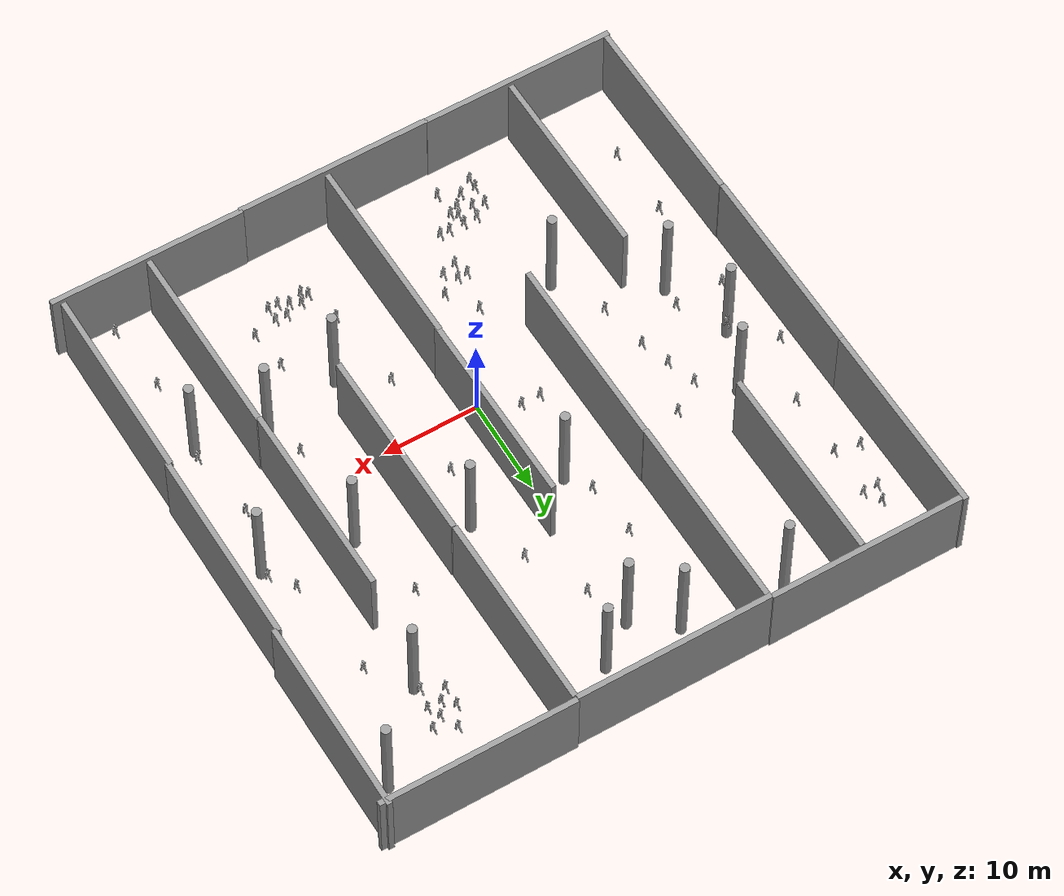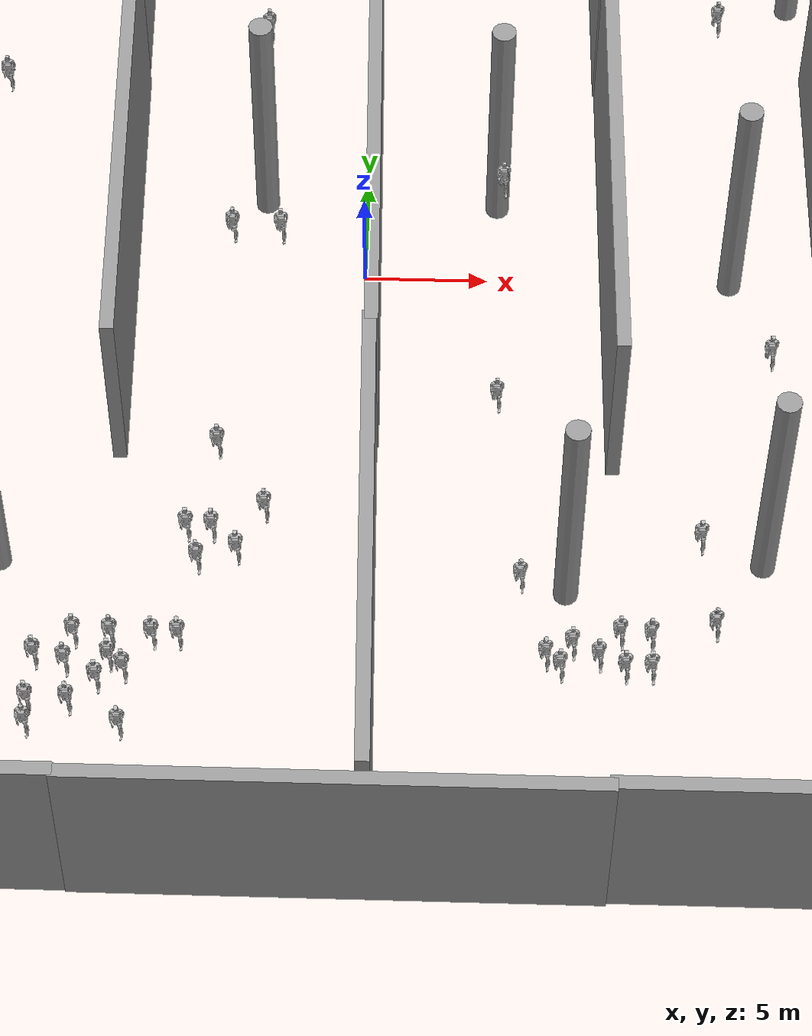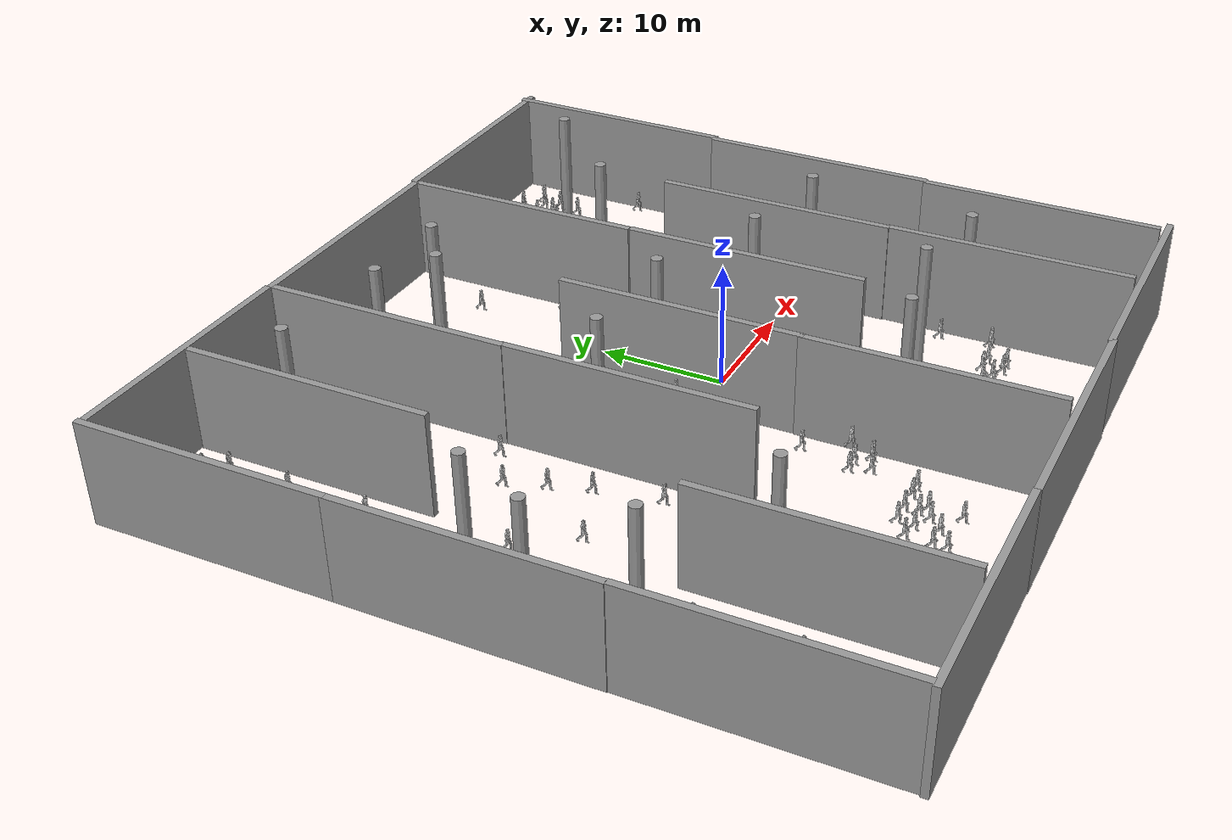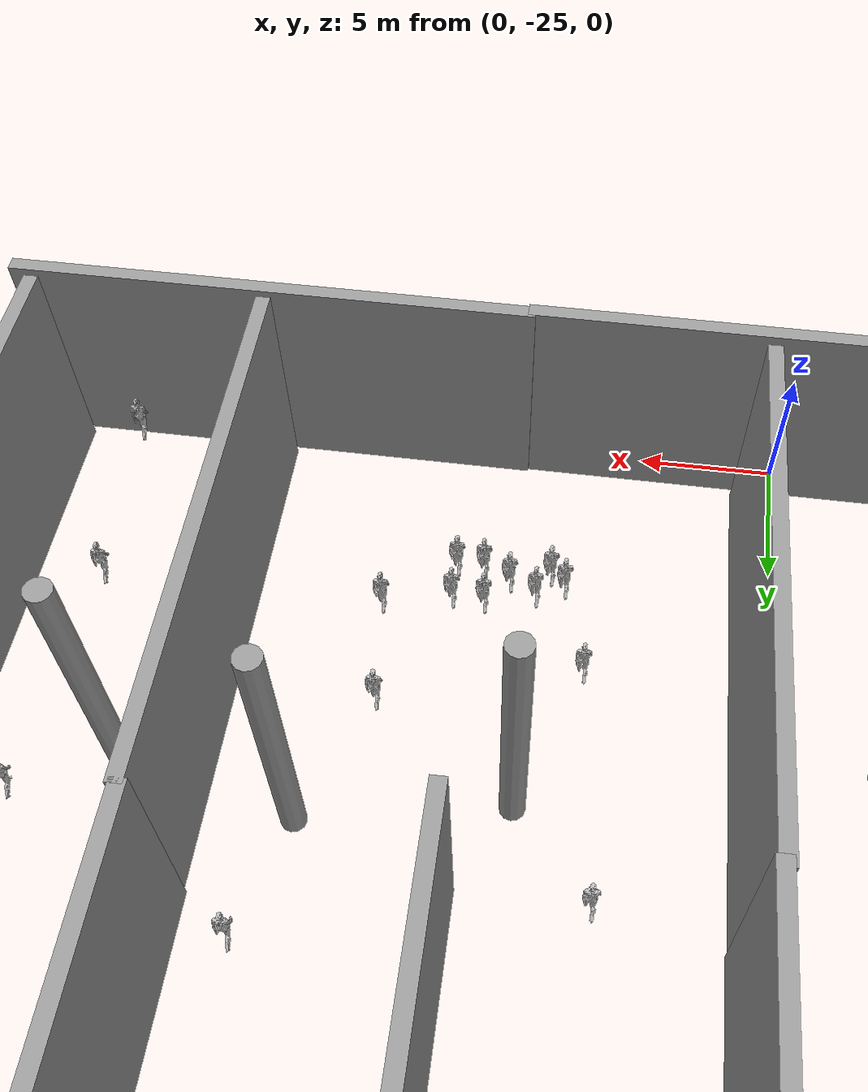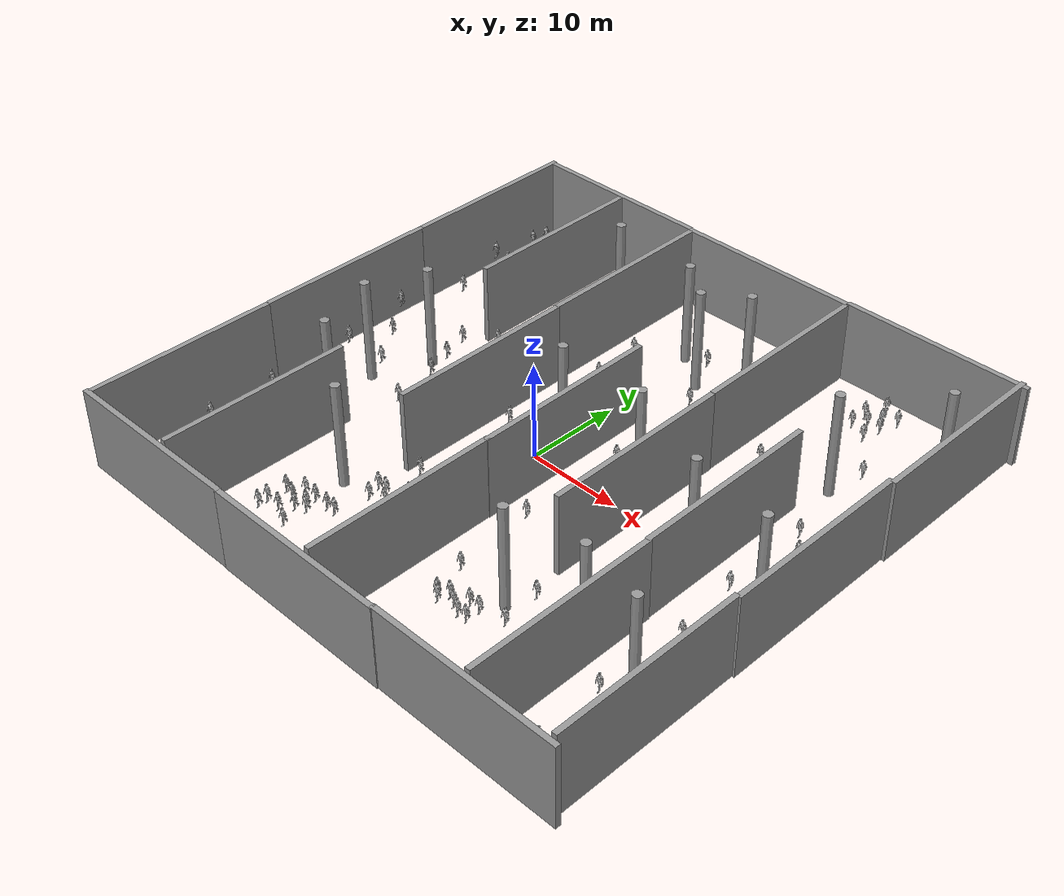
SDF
<?xml version='1.0'?>
<sdf version='1.6'>
  <model name='test_map_3'>
    <link name='link_0'>
      <pose frame=''>-15.9506 28.1604 0.429752 0 -0 0</pose>
      <inertial>
        <mass>11.4017</mass>
        <inertia>
          <ixx>124.231</ixx>
          <ixy>0</ixy>
          <ixz>0</ixz>
          <iyy>124.231</iyy>
          <iyz>0</iyz>
          <izz>1.42522</izz>
        </inertia>
        <pose frame=''>0 0 0 0 -0 0</pose>
      </inertial>
      <self_collide>0</self_collide>
      <kinematic>0</kinematic>
      <visual name='visual'>
        <pose frame=''>0 0 0 0 -0 0</pose>
        <geometry>
          <cylinder>
            <radius>0.5</radius>
            <length>11.4018</length>
          </cylinder>
        </geometry>
        <material>
          <lighting>1</lighting>
          <script>
            <uri>file://media/materials/scripts/gazebo.material</uri>
            <name>Gazebo/Grey</name>
          </script>
          <ambient>0.3 0.3 0.3 1</ambient>
          <diffuse>0.7 0.7 0.7 1</diffuse>
          <specular>0.01 0.01 0.01 1</specular>
          <emissive>0 0 0 1</emissive>
        </material>
        <cast_shadows>1</cast_shadows>
        <transparency>0</transparency>
      </visual>
      <collision name='collision'>
        <laser_retro>0</laser_retro>
        <max_contacts>10</max_contacts>
        <pose frame=''>0 0 0 0 -0 0</pose>
        <geometry>
          <cylinder>
            <radius>0.5</radius>
            <length>11.4018</length>
          </cylinder>
        </geometry>
        <surface>
          <friction>
            <ode>
              <mu>1</mu>
              <mu2>1</mu2>
              <fdir1>0 0 0</fdir1>
              <slip1>0</slip1>
              <slip2>0</slip2>
            </ode>
            <torsional>
              <coefficient>1</coefficient>
              <patch_radius>0</patch_radius>
              <surface_radius>0</surface_radius>
              <use_patch_radius>1</use_patch_radius>
              <ode>
                <slip>0</slip>
              </ode>
            </torsional>
          </friction>
          <bounce>
            <restitution_coefficient>0</restitution_coefficient>
            <threshold>1e+06</threshold>
          </bounce>
          <contact>
            <collide_without_contact>0</collide_without_contact>
            <collide_without_contact_bitmask>1</collide_without_contact_bitmask>
            <collide_bitmask>1</collide_bitmask>
            <ode>
              <soft_cfm>0</soft_cfm>
              <soft_erp>0.2</soft_erp>
              <kp>1e+13</kp>
              <kd>1</kd>
              <max_vel>0.01</max_vel>
              <min_depth>0</min_depth>
            </ode>
            <bullet>
              <split_impulse>1</split_impulse>
              <split_impulse_penetration_threshold>-0.01</split_impulse_penetration_threshold>
              <soft_cfm>0</soft_cfm>
              <soft_erp>0.2</soft_erp>
              <kp>1e+13</kp>
              <kd>1</kd>
            </bullet>
          </contact>
        </surface>
      </collision>
    </link>
    <link name='link_0_clone'>
      <pose frame=''>-5.53003 27.1604 0.429752 0 -0 0</pose>
      <inertial>
        <mass>11.4017</mass>
        <inertia>
          <ixx>124.231</ixx>
          <ixy>0</ixy>
          <ixz>0</ixz>
          <iyy>124.231</iyy>
          <iyz>0</iyz>
          <izz>1.42522</izz>
        </inertia>
        <pose frame=''>0 0 0 0 -0 0</pose>
      </inertial>
      <self_collide>0</self_collide>
      <kinematic>0</kinematic>
      <visual name='visual'>
        <pose frame=''>0 0 0 0 -0 0</pose>
        <geometry>
          <cylinder>
            <radius>0.5</radius>
            <length>11.4018</length>
          </cylinder>
        </geometry>
        <material>
          <lighting>1</lighting>
          <script>
            <uri>file://media/materials/scripts/gazebo.material</uri>
            <name>Gazebo/Grey</name>
          </script>
          <ambient>0.3 0.3 0.3 1</ambient>
          <diffuse>0.7 0.7 0.7 1</diffuse>
          <specular>0.01 0.01 0.01 1</specular>
          <emissive>0 0 0 1</emissive>
          <shader type='pixel'/>
        </material>
        <cast_shadows>1</cast_shadows>
        <transparency>0</transparency>
      </visual>
      <collision name='collision'>
        <laser_retro>0</laser_retro>
        <max_contacts>10</max_contacts>
        <pose frame=''>0 0 0 0 -0 0</pose>
        <geometry>
          <cylinder>
            <radius>0.5</radius>
            <length>11.4018</length>
          </cylinder>
        </geometry>
        <surface>
          <friction>
            <ode>
              <mu>1</mu>
              <mu2>1</mu2>
              <fdir1>0 0 0</fdir1>
              <slip1>0</slip1>
              <slip2>0</slip2>
            </ode>
            <torsional>
              <coefficient>1</coefficient>
              <patch_radius>0</patch_radius>
              <surface_radius>0</surface_radius>
              <use_patch_radius>1</use_patch_radius>
              <ode>
                <slip>0</slip>
              </ode>
            </torsional>
          </friction>
          <bounce>
            <restitution_coefficient>0</restitution_coefficient>
            <threshold>1e+06</threshold>
          </bounce>
          <contact>
            <collide_without_contact>0</collide_without_contact>
            <collide_without_contact_bitmask>1</collide_without_contact_bitmask>
            <collide_bitmask>1</collide_bitmask>
            <ode>
              <soft_cfm>0</soft_cfm>
              <soft_erp>0.2</soft_erp>
              <kp>1e+13</kp>
              <kd>1</kd>
              <max_vel>0.01</max_vel>
              <min_depth>0</min_depth>
            </ode>
            <bullet>
              <split_impulse>1</split_impulse>
              <split_impulse_penetration_threshold>-0.01</split_impulse_penetration_threshold>
              <soft_cfm>0</soft_cfm>
              <soft_erp>0.2</soft_erp>
              <kp>1e+13</kp>
              <kd>1</kd>
            </bullet>
          </contact>
        </surface>
      </collision>
    </link>
    <link name='link_0_clone_0'>
      <pose frame=''>2.46997 27.1604 0.429752 0 -0 0</pose>
      <inertial>
        <mass>11.4017</mass>
        <inertia>
          <ixx>124.231</ixx>
          <ixy>0</ixy>
          <ixz>0</ixz>
          <iyy>124.231</iyy>
          <iyz>0</iyz>
          <izz>1.42522</izz>
        </inertia>
        <pose frame=''>0 0 0 0 -0 0</pose>
      </inertial>
      <self_collide>0</self_collide>
      <kinematic>0</kinematic>
      <visual name='visual'>
        <pose frame=''>0 0 0 0 -0 0</pose>
        <geometry>
          <cylinder>
            <radius>0.5</radius>
            <length>11.4018</length>
          </cylinder>
        </geometry>
        <material>
          <lighting>1</lighting>
          <script>
            <uri>file://media/materials/scripts/gazebo.material</uri>
            <name>Gazebo/Grey</name>
          </script>
          <ambient>0.3 0.3 0.3 1</ambient>
          <diffuse>0.7 0.7 0.7 1</diffuse>
          <specular>0.01 0.01 0.01 1</specular>
          <emissive>0 0 0 1</emissive>
          <shader type='pixel'/>
        </material>
        <cast_shadows>1</cast_shadows>
        <transparency>0</transparency>
      </visual>
      <collision name='collision'>
        <laser_retro>0</laser_retro>
        <max_contacts>10</max_contacts>
        <pose frame=''>0 0 0 0 -0 0</pose>
        <geometry>
          <cylinder>
            <radius>0.5</radius>
            <length>11.4018</length>
          </cylinder>
        </geometry>
        <surface>
          <friction>
            <ode>
              <mu>1</mu>
              <mu2>1</mu2>
              <fdir1>0 0 0</fdir1>
              <slip1>0</slip1>
              <slip2>0</slip2>
            </ode>
            <torsional>
              <coefficient>1</coefficient>
              <patch_radius>0</patch_radius>
              <surface_radius>0</surface_radius>
              <use_patch_radius>1</use_patch_radius>
              <ode>
                <slip>0</slip>
              </ode>
            </torsional>
          </friction>
          <bounce>
            <restitution_coefficient>0</restitution_coefficient>
            <threshold>1e+06</threshold>
          </bounce>
          <contact>
            <collide_without_contact>0</collide_without_contact>
            <collide_without_contact_bitmask>1</collide_without_contact_bitmask>
            <collide_bitmask>1</collide_bitmask>
            <ode>
              <soft_cfm>0</soft_cfm>
              <soft_erp>0.2</soft_erp>
              <kp>1e+13</kp>
              <kd>1</kd>
              <max_vel>0.01</max_vel>
              <min_depth>0</min_depth>
            </ode>
            <bullet>
              <split_impulse>1</split_impulse>
              <split_impulse_penetration_threshold>-0.01</split_impulse_penetration_threshold>
              <soft_cfm>0</soft_cfm>
              <soft_erp>0.2</soft_erp>
              <kp>1e+13</kp>
              <kd>1</kd>
            </bullet>
          </contact>
        </surface>
      </collision>
    </link>
    <link name='link_0_clone_1'>
      <pose frame=''>-1.53003 24.1604 0.429752 0 -0 0</pose>
      <inertial>
        <mass>11.4017</mass>
        <inertia>
          <ixx>124.231</ixx>
          <ixy>0</ixy>
          <ixz>0</ixz>
          <iyy>124.231</iyy>
          <iyz>0</iyz>
          <izz>1.42522</izz>
        </inertia>
        <pose frame=''>0 0 0 0 -0 0</pose>
      </inertial>
      <self_collide>0</self_collide>
      <kinematic>0</kinematic>
      <visual name='visual'>
        <pose frame=''>0 0 0 0 -0 0</pose>
        <geometry>
          <cylinder>
            <radius>0.5</radius>
            <length>11.4018</length>
          </cylinder>
        </geometry>
        <material>
          <lighting>1</lighting>
          <script>
            <uri>file://media/materials/scripts/gazebo.material</uri>
            <name>Gazebo/Grey</name>
          </script>
          <ambient>0.3 0.3 0.3 1</ambient>
          <diffuse>0.7 0.7 0.7 1</diffuse>
          <specular>0.01 0.01 0.01 1</specular>
          <emissive>0 0 0 1</emissive>
          <shader type='pixel'/>
        </material>
        <cast_shadows>1</cast_shadows>
        <transparency>0</transparency>
      </visual>
      <collision name='collision'>
        <laser_retro>0</laser_retro>
        <max_contacts>10</max_contacts>
        <pose frame=''>0 0 0 0 -0 0</pose>
        <geometry>
          <cylinder>
            <radius>0.5</radius>
            <length>11.4018</length>
          </cylinder>
        </geometry>
        <surface>
          <friction>
            <ode>
              <mu>1</mu>
              <mu2>1</mu2>
              <fdir1>0 0 0</fdir1>
              <slip1>0</slip1>
              <slip2>0</slip2>
            </ode>
            <torsional>
              <coefficient>1</coefficient>
              <patch_radius>0</patch_radius>
              <surface_radius>0</surface_radius>
              <use_patch_radius>1</use_patch_radius>
              <ode>
                <slip>0</slip>
              </ode>
            </torsional>
          </friction>
          <bounce>
            <restitution_coefficient>0</restitution_coefficient>
            <threshold>1e+06</threshold>
          </bounce>
          <contact>
            <collide_without_contact>0</collide_without_contact>
            <collide_without_contact_bitmask>1</collide_without_contact_bitmask>
            <collide_bitmask>1</collide_bitmask>
            <ode>
              <soft_cfm>0</soft_cfm>
              <soft_erp>0.2</soft_erp>
              <kp>1e+13</kp>
              <kd>1</kd>
              <max_vel>0.01</max_vel>
              <min_depth>0</min_depth>
            </ode>
            <bullet>
              <split_impulse>1</split_impulse>
              <split_impulse_penetration_threshold>-0.01</split_impulse_penetration_threshold>
              <soft_cfm>0</soft_cfm>
              <soft_erp>0.2</soft_erp>
              <kp>1e+13</kp>
              <kd>1</kd>
            </bullet>
          </contact>
        </surface>
      </collision>
    </link>
    <link name='link_0_clone_10'>
      <pose frame=''>15.47 4.16036 0.429753 0 -0 0</pose>
      <inertial>
        <mass>11.4017</mass>
        <inertia>
          <ixx>124.231</ixx>
          <ixy>0</ixy>
          <ixz>0</ixz>
          <iyy>124.231</iyy>
          <iyz>0</iyz>
          <izz>1.42522</izz>
        </inertia>
        <pose frame=''>0 0 0 0 -0 0</pose>
      </inertial>
      <self_collide>0</self_collide>
      <kinematic>0</kinematic>
      <visual name='visual'>
        <pose frame=''>0 0 0 0 -0 0</pose>
        <geometry>
          <cylinder>
            <radius>0.5</radius>
            <length>11.4018</length>
          </cylinder>
        </geometry>
        <material>
          <lighting>1</lighting>
          <script>
            <uri>file://media/materials/scripts/gazebo.material</uri>
            <name>Gazebo/Grey</name>
          </script>
          <ambient>0.3 0.3 0.3 1</ambient>
          <diffuse>0.7 0.7 0.7 1</diffuse>
          <specular>0.01 0.01 0.01 1</specular>
          <emissive>0 0 0 1</emissive>
          <shader type='pixel'/>
        </material>
        <cast_shadows>1</cast_shadows>
        <transparency>0</transparency>
      </visual>
      <collision name='collision'>
        <laser_retro>0</laser_retro>
        <max_contacts>10</max_contacts>
        <pose frame=''>0 0 0 0 -0 0</pose>
        <geometry>
          <cylinder>
            <radius>0.5</radius>
            <length>11.4018</length>
          </cylinder>
        </geometry>
        <surface>
          <friction>
            <ode>
              <mu>1</mu>
              <mu2>1</mu2>
              <fdir1>0 0 0</fdir1>
              <slip1>0</slip1>
              <slip2>0</slip2>
            </ode>
            <torsional>
              <coefficient>1</coefficient>
              <patch_radius>0</patch_radius>
              <surface_radius>0</surface_radius>
              <use_patch_radius>1</use_patch_radius>
              <ode>
                <slip>0</slip>
              </ode>
            </torsional>
          </friction>
          <bounce>
            <restitution_coefficient>0</restitution_coefficient>
            <threshold>1e+06</threshold>
          </bounce>
          <contact>
            <collide_without_contact>0</collide_without_contact>
            <collide_without_contact_bitmask>1</collide_without_contact_bitmask>
            <collide_bitmask>1</collide_bitmask>
            <ode>
              <soft_cfm>0</soft_cfm>
              <soft_erp>0.2</soft_erp>
              <kp>1e+13</kp>
              <kd>1</kd>
              <max_vel>0.01</max_vel>
              <min_depth>0</min_depth>
            </ode>
            <bullet>
              <split_impulse>1</split_impulse>
              <split_impulse_penetration_threshold>-0.01</split_impulse_penetration_threshold>
              <soft_cfm>0</soft_cfm>
              <soft_erp>0.2</soft_erp>
              <kp>1e+13</kp>
              <kd>1</kd>
            </bullet>
          </contact>
        </surface>
      </collision>
    </link>
    <link name='link_0_clone_11'>
      <pose frame=''>24.47 2.67171 0.429751 0 -0 0</pose>
      <inertial>
        <mass>11.4017</mass>
        <inertia>
          <ixx>124.231</ixx>
          <ixy>0</ixy>
          <ixz>0</ixz>
          <iyy>124.231</iyy>
          <iyz>0</iyz>
          <izz>1.42522</izz>
        </inertia>
        <pose frame=''>0 0 0 0 -0 0</pose>
      </inertial>
      <self_collide>0</self_collide>
      <kinematic>0</kinematic>
      <visual name='visual'>
        <pose frame=''>0 0 0 0 -0 0</pose>
        <geometry>
          <cylinder>
            <radius>0.5</radius>
            <length>11.4018</length>
          </cylinder>
        </geometry>
        <material>
          <lighting>1</lighting>
          <script>
            <uri>file://media/materials/scripts/gazebo.material</uri>
            <name>Gazebo/Grey</name>
          </script>
          <ambient>0.3 0.3 0.3 1</ambient>
          <diffuse>0.7 0.7 0.7 1</diffuse>
          <specular>0.01 0.01 0.01 1</specular>
          <emissive>0 0 0 1</emissive>
          <shader type='pixel'/>
        </material>
        <cast_shadows>1</cast_shadows>
        <transparency>0</transparency>
      </visual>
      <collision name='collision'>
        <laser_retro>0</laser_retro>
        <max_contacts>10</max_contacts>
        <pose frame=''>0 0 0 0 -0 0</pose>
        <geometry>
          <cylinder>
            <radius>0.5</radius>
            <length>11.4018</length>
          </cylinder>
        </geometry>
        <surface>
          <friction>
            <ode>
              <mu>1</mu>
              <mu2>1</mu2>
              <fdir1>0 0 0</fdir1>
              <slip1>0</slip1>
              <slip2>0</slip2>
            </ode>
            <torsional>
              <coefficient>1</coefficient>
              <patch_radius>0</patch_radius>
              <surface_radius>0</surface_radius>
              <use_patch_radius>1</use_patch_radius>
              <ode>
                <slip>0</slip>
              </ode>
            </torsional>
          </friction>
          <bounce>
            <restitution_coefficient>0</restitution_coefficient>
            <threshold>1e+06</threshold>
          </bounce>
          <contact>
            <collide_without_contact>0</collide_without_contact>
            <collide_without_contact_bitmask>1</collide_without_contact_bitmask>
            <collide_bitmask>1</collide_bitmask>
            <ode>
              <soft_cfm>0</soft_cfm>
              <soft_erp>0.2</soft_erp>
              <kp>1e+13</kp>
              <kd>1</kd>
              <max_vel>0.01</max_vel>
              <min_depth>0</min_depth>
            </ode>
            <bullet>
              <split_impulse>1</split_impulse>
              <split_impulse_penetration_threshold>-0.01</split_impulse_penetration_threshold>
              <soft_cfm>0</soft_cfm>
              <soft_erp>0.2</soft_erp>
              <kp>1e+13</kp>
              <kd>1</kd>
            </bullet>
          </contact>
        </surface>
      </collision>
    </link>
    <link name='link_0_clone_12'>
      <pose frame=''>23.47 -11.8396 0.42975 0 -0 0</pose>
      <inertial>
        <mass>11.4017</mass>
        <inertia>
          <ixx>124.231</ixx>
          <ixy>0</ixy>
          <ixz>0</ixz>
          <iyy>124.231</iyy>
          <iyz>0</iyz>
          <izz>1.42522</izz>
        </inertia>
        <pose frame=''>0 0 0 0 -0 0</pose>
      </inertial>
      <self_collide>0</self_collide>
      <kinematic>0</kinematic>
      <visual name='visual'>
        <pose frame=''>0 0 0 0 -0 0</pose>
        <geometry>
          <cylinder>
            <radius>0.5</radius>
            <length>11.4018</length>
          </cylinder>
        </geometry>
        <material>
          <lighting>1</lighting>
          <script>
            <uri>file://media/materials/scripts/gazebo.material</uri>
            <name>Gazebo/Grey</name>
          </script>
          <ambient>0.3 0.3 0.3 1</ambient>
          <diffuse>0.7 0.7 0.7 1</diffuse>
          <specular>0.01 0.01 0.01 1</specular>
          <emissive>0 0 0 1</emissive>
          <shader type='pixel'/>
        </material>
        <cast_shadows>1</cast_shadows>
        <transparency>0</transparency>
      </visual>
      <collision name='collision'>
        <laser_retro>0</laser_retro>
        <max_contacts>10</max_contacts>
        <pose frame=''>0 0 0 0 -0 0</pose>
        <geometry>
          <cylinder>
            <radius>0.5</radius>
            <length>11.4018</length>
          </cylinder>
        </geometry>
        <surface>
          <friction>
            <ode>
              <mu>1</mu>
              <mu2>1</mu2>
              <fdir1>0 0 0</fdir1>
              <slip1>0</slip1>
              <slip2>0</slip2>
            </ode>
            <torsional>
              <coefficient>1</coefficient>
              <patch_radius>0</patch_radius>
              <surface_radius>0</surface_radius>
              <use_patch_radius>1</use_patch_radius>
              <ode>
                <slip>0</slip>
              </ode>
            </torsional>
          </friction>
          <bounce>
            <restitution_coefficient>0</restitution_coefficient>
            <threshold>1e+06</threshold>
          </bounce>
          <contact>
            <collide_without_contact>0</collide_without_contact>
            <collide_without_contact_bitmask>1</collide_without_contact_bitmask>
            <collide_bitmask>1</collide_bitmask>
            <ode>
              <soft_cfm>0</soft_cfm>
              <soft_erp>0.2</soft_erp>
              <kp>1e+13</kp>
              <kd>1</kd>
              <max_vel>0.01</max_vel>
              <min_depth>0</min_depth>
            </ode>
            <bullet>
              <split_impulse>1</split_impulse>
              <split_impulse_penetration_threshold>-0.01</split_impulse_penetration_threshold>
              <soft_cfm>0</soft_cfm>
              <soft_erp>0.2</soft_erp>
              <kp>1e+13</kp>
              <kd>1</kd>
            </bullet>
          </contact>
        </surface>
      </collision>
    </link>
    <link name='link_0_clone_13'>
      <pose frame=''>18.47 20.1604 0.42975 0 -0 0</pose>
      <inertial>
        <mass>11.4017</mass>
        <inertia>
          <ixx>124.231</ixx>
          <ixy>0</ixy>
          <ixz>0</ixz>
          <iyy>124.231</iyy>
          <iyz>0</iyz>
          <izz>1.42522</izz>
        </inertia>
        <pose frame=''>0 0 0 0 -0 0</pose>
      </inertial>
      <self_collide>0</self_collide>
      <kinematic>0</kinematic>
      <visual name='visual'>
        <pose frame=''>0 0 0 0 -0 0</pose>
        <geometry>
          <cylinder>
            <radius>0.5</radius>
            <length>11.4018</length>
          </cylinder>
        </geometry>
        <material>
          <lighting>1</lighting>
          <script>
            <uri>file://media/materials/scripts/gazebo.material</uri>
            <name>Gazebo/Grey</name>
          </script>
          <ambient>0.3 0.3 0.3 1</ambient>
          <diffuse>0.7 0.7 0.7 1</diffuse>
          <specular>0.01 0.01 0.01 1</specular>
          <emissive>0 0 0 1</emissive>
          <shader type='pixel'/>
        </material>
        <cast_shadows>1</cast_shadows>
        <transparency>0</transparency>
      </visual>
      <collision name='collision'>
        <laser_retro>0</laser_retro>
        <max_contacts>10</max_contacts>
        <pose frame=''>0 0 0 0 -0 0</pose>
        <geometry>
          <cylinder>
            <radius>0.5</radius>
            <length>11.4018</length>
          </cylinder>
        </geometry>
        <surface>
          <friction>
            <ode>
              <mu>1</mu>
              <mu2>1</mu2>
              <fdir1>0 0 0</fdir1>
              <slip1>0</slip1>
              <slip2>0</slip2>
            </ode>
            <torsional>
              <coefficient>1</coefficient>
              <patch_radius>0</patch_radius>
              <surface_radius>0</surface_radius>
              <use_patch_radius>1</use_patch_radius>
              <ode>
                <slip>0</slip>
              </ode>
            </torsional>
          </friction>
          <bounce>
            <restitution_coefficient>0</restitution_coefficient>
            <threshold>1e+06</threshold>
          </bounce>
          <contact>
            <collide_without_contact>0</collide_without_contact>
            <collide_without_contact_bitmask>1</collide_without_contact_bitmask>
            <collide_bitmask>1</collide_bitmask>
            <ode>
              <soft_cfm>0</soft_cfm>
              <soft_erp>0.2</soft_erp>
              <kp>1e+13</kp>
              <kd>1</kd>
              <max_vel>0.01</max_vel>
              <min_depth>0</min_depth>
            </ode>
            <bullet>
              <split_impulse>1</split_impulse>
              <split_impulse_penetration_threshold>-0.01</split_impulse_penetration_threshold>
              <soft_cfm>0</soft_cfm>
              <soft_erp>0.2</soft_erp>
              <kp>1e+13</kp>
              <kd>1</kd>
            </bullet>
          </contact>
        </surface>
      </collision>
    </link>
    <link name='link_0_clone_14'>
      <pose frame=''>25.47 27.6555 0.429753 0 -0 0</pose>
      <inertial>
        <mass>11.4017</mass>
        <inertia>
          <ixx>124.231</ixx>
          <ixy>0</ixy>
          <ixz>0</ixz>
          <iyy>124.231</iyy>
          <iyz>0</iyz>
          <izz>1.42522</izz>
        </inertia>
        <pose frame=''>0 0 0 0 -0 0</pose>
      </inertial>
      <self_collide>0</self_collide>
      <kinematic>0</kinematic>
      <visual name='visual'>
        <pose frame=''>0 0 0 0 -0 0</pose>
        <geometry>
          <cylinder>
            <radius>0.5</radius>
            <length>11.4018</length>
          </cylinder>
        </geometry>
        <material>
          <lighting>1</lighting>
          <script>
            <uri>file://media/materials/scripts/gazebo.material</uri>
            <name>Gazebo/Grey</name>
          </script>
          <ambient>0.3 0.3 0.3 1</ambient>
          <diffuse>0.7 0.7 0.7 1</diffuse>
          <specular>0.01 0.01 0.01 1</specular>
          <emissive>0 0 0 1</emissive>
          <shader type='pixel'/>
        </material>
        <cast_shadows>1</cast_shadows>
        <transparency>0</transparency>
      </visual>
      <collision name='collision'>
        <laser_retro>0</laser_retro>
        <max_contacts>10</max_contacts>
        <pose frame=''>0 0 0 0 -0 0</pose>
        <geometry>
          <cylinder>
            <radius>0.5</radius>
            <length>11.4018</length>
          </cylinder>
        </geometry>
        <surface>
          <friction>
            <ode>
              <mu>1</mu>
              <mu2>1</mu2>
              <fdir1>0 0 0</fdir1>
              <slip1>0</slip1>
              <slip2>0</slip2>
            </ode>
            <torsional>
              <coefficient>1</coefficient>
              <patch_radius>0</patch_radius>
              <surface_radius>0</surface_radius>
              <use_patch_radius>1</use_patch_radius>
              <ode>
                <slip>0</slip>
              </ode>
            </torsional>
          </friction>
          <bounce>
            <restitution_coefficient>0</restitution_coefficient>
            <threshold>1e+06</threshold>
          </bounce>
          <contact>
            <collide_without_contact>0</collide_without_contact>
            <collide_without_contact_bitmask>1</collide_without_contact_bitmask>
            <collide_bitmask>1</collide_bitmask>
            <ode>
              <soft_cfm>0</soft_cfm>
              <soft_erp>0.2</soft_erp>
              <kp>1e+13</kp>
              <kd>1</kd>
              <max_vel>0.01</max_vel>
              <min_depth>0</min_depth>
            </ode>
            <bullet>
              <split_impulse>1</split_impulse>
              <split_impulse_penetration_threshold>-0.01</split_impulse_penetration_threshold>
              <soft_cfm>0</soft_cfm>
              <soft_erp>0.2</soft_erp>
              <kp>1e+13</kp>
              <kd>1</kd>
            </bullet>
          </contact>
        </surface>
      </collision>
    </link>
    <link name='link_0_clone_2'>
      <pose frame=''>-4.53003 8.16036 0.429752 0 -0 0</pose>
      <inertial>
        <mass>11.4017</mass>
        <inertia>
          <ixx>124.231</ixx>
          <ixy>0</ixy>
          <ixz>0</ixz>
          <iyy>124.231</iyy>
          <iyz>0</iyz>
          <izz>1.42522</izz>
        </inertia>
        <pose frame=''>0 0 0 0 -0 0</pose>
      </inertial>
      <self_collide>0</self_collide>
      <kinematic>0</kinematic>
      <visual name='visual'>
        <pose frame=''>0 0 0 0 -0 0</pose>
        <geometry>
          <cylinder>
            <radius>0.5</radius>
            <length>11.4018</length>
          </cylinder>
        </geometry>
        <material>
          <lighting>1</lighting>
          <script>
            <uri>file://media/materials/scripts/gazebo.material</uri>
            <name>Gazebo/Grey</name>
          </script>
          <ambient>0.3 0.3 0.3 1</ambient>
          <diffuse>0.7 0.7 0.7 1</diffuse>
          <specular>0.01 0.01 0.01 1</specular>
          <emissive>0 0 0 1</emissive>
          <shader type='pixel'/>
        </material>
        <cast_shadows>1</cast_shadows>
        <transparency>0</transparency>
      </visual>
      <collision name='collision'>
        <laser_retro>0</laser_retro>
        <max_contacts>10</max_contacts>
        <pose frame=''>0 0 0 0 -0 0</pose>
        <geometry>
          <cylinder>
            <radius>0.5</radius>
            <length>11.4018</length>
          </cylinder>
        </geometry>
        <surface>
          <friction>
            <ode>
              <mu>1</mu>
              <mu2>1</mu2>
              <fdir1>0 0 0</fdir1>
              <slip1>0</slip1>
              <slip2>0</slip2>
            </ode>
            <torsional>
              <coefficient>1</coefficient>
              <patch_radius>0</patch_radius>
              <surface_radius>0</surface_radius>
              <use_patch_radius>1</use_patch_radius>
              <ode>
                <slip>0</slip>
              </ode>
            </torsional>
          </friction>
          <bounce>
            <restitution_coefficient>0</restitution_coefficient>
            <threshold>1e+06</threshold>
          </bounce>
          <contact>
            <collide_without_contact>0</collide_without_contact>
            <collide_without_contact_bitmask>1</collide_without_contact_bitmask>
            <collide_bitmask>1</collide_bitmask>
            <ode>
              <soft_cfm>0</soft_cfm>
              <soft_erp>0.2</soft_erp>
              <kp>1e+13</kp>
              <kd>1</kd>
              <max_vel>0.01</max_vel>
              <min_depth>0</min_depth>
            </ode>
            <bullet>
              <split_impulse>1</split_impulse>
              <split_impulse_penetration_threshold>-0.01</split_impulse_penetration_threshold>
              <soft_cfm>0</soft_cfm>
              <soft_erp>0.2</soft_erp>
              <kp>1e+13</kp>
              <kd>1</kd>
            </bullet>
          </contact>
        </surface>
      </collision>
    </link>
    <link name='link_0_clone_3'>
      <pose frame=''>5.46997 8.16036 0.429752 0 -0 0</pose>
      <inertial>
        <mass>11.4017</mass>
        <inertia>
          <ixx>124.231</ixx>
          <ixy>0</ixy>
          <ixz>0</ixz>
          <iyy>124.231</iyy>
          <iyz>0</iyz>
          <izz>1.42522</izz>
        </inertia>
        <pose frame=''>0 0 0 0 -0 0</pose>
      </inertial>
      <self_collide>0</self_collide>
      <kinematic>0</kinematic>
      <visual name='visual'>
        <pose frame=''>0 0 0 0 -0 0</pose>
        <geometry>
          <cylinder>
            <radius>0.5</radius>
            <length>11.4018</length>
          </cylinder>
        </geometry>
        <material>
          <lighting>1</lighting>
          <script>
            <uri>file://media/materials/scripts/gazebo.material</uri>
            <name>Gazebo/Grey</name>
          </script>
          <ambient>0.3 0.3 0.3 1</ambient>
          <diffuse>0.7 0.7 0.7 1</diffuse>
          <specular>0.01 0.01 0.01 1</specular>
          <emissive>0 0 0 1</emissive>
          <shader type='pixel'/>
        </material>
        <cast_shadows>1</cast_shadows>
        <transparency>0</transparency>
      </visual>
      <collision name='collision'>
        <laser_retro>0</laser_retro>
        <max_contacts>10</max_contacts>
        <pose frame=''>0 0 0 0 -0 0</pose>
        <geometry>
          <cylinder>
            <radius>0.5</radius>
            <length>11.4018</length>
          </cylinder>
        </geometry>
        <surface>
          <friction>
            <ode>
              <mu>1</mu>
              <mu2>1</mu2>
              <fdir1>0 0 0</fdir1>
              <slip1>0</slip1>
              <slip2>0</slip2>
            </ode>
            <torsional>
              <coefficient>1</coefficient>
              <patch_radius>0</patch_radius>
              <surface_radius>0</surface_radius>
              <use_patch_radius>1</use_patch_radius>
              <ode>
                <slip>0</slip>
              </ode>
            </torsional>
          </friction>
          <bounce>
            <restitution_coefficient>0</restitution_coefficient>
            <threshold>1e+06</threshold>
          </bounce>
          <contact>
            <collide_without_contact>0</collide_without_contact>
            <collide_without_contact_bitmask>1</collide_without_contact_bitmask>
            <collide_bitmask>1</collide_bitmask>
            <ode>
              <soft_cfm>0</soft_cfm>
              <soft_erp>0.2</soft_erp>
              <kp>1e+13</kp>
              <kd>1</kd>
              <max_vel>0.01</max_vel>
              <min_depth>0</min_depth>
            </ode>
            <bullet>
              <split_impulse>1</split_impulse>
              <split_impulse_penetration_threshold>-0.01</split_impulse_penetration_threshold>
              <soft_cfm>0</soft_cfm>
              <soft_erp>0.2</soft_erp>
              <kp>1e+13</kp>
              <kd>1</kd>
            </bullet>
          </contact>
        </surface>
      </collision>
    </link>
    <link name='link_0_clone_4'>
      <pose frame=''>-23.53 8.16036 0.429753 0 -0 0</pose>
      <inertial>
        <mass>11.4017</mass>
        <inertia>
          <ixx>124.231</ixx>
          <ixy>0</ixy>
          <ixz>0</ixz>
          <iyy>124.231</iyy>
          <iyz>0</iyz>
          <izz>1.42522</izz>
        </inertia>
        <pose frame=''>0 0 0 0 -0 0</pose>
      </inertial>
      <self_collide>0</self_collide>
      <kinematic>0</kinematic>
      <visual name='visual'>
        <pose frame=''>0 0 0 0 -0 0</pose>
        <geometry>
          <cylinder>
            <radius>0.5</radius>
            <length>11.4018</length>
          </cylinder>
        </geometry>
        <material>
          <lighting>1</lighting>
          <script>
            <uri>file://media/materials/scripts/gazebo.material</uri>
            <name>Gazebo/Grey</name>
          </script>
          <ambient>0.3 0.3 0.3 1</ambient>
          <diffuse>0.7 0.7 0.7 1</diffuse>
          <specular>0.01 0.01 0.01 1</specular>
          <emissive>0 0 0 1</emissive>
          <shader type='pixel'/>
        </material>
        <cast_shadows>1</cast_shadows>
        <transparency>0</transparency>
      </visual>
      <collision name='collision'>
        <laser_retro>0</laser_retro>
        <max_contacts>10</max_contacts>
        <pose frame=''>0 0 0 0 -0 0</pose>
        <geometry>
          <cylinder>
            <radius>0.5</radius>
            <length>11.4018</length>
          </cylinder>
        </geometry>
        <surface>
          <friction>
            <ode>
              <mu>1</mu>
              <mu2>1</mu2>
              <fdir1>0 0 0</fdir1>
              <slip1>0</slip1>
              <slip2>0</slip2>
            </ode>
            <torsional>
              <coefficient>1</coefficient>
              <patch_radius>0</patch_radius>
              <surface_radius>0</surface_radius>
              <use_patch_radius>1</use_patch_radius>
              <ode>
                <slip>0</slip>
              </ode>
            </torsional>
          </friction>
          <bounce>
            <restitution_coefficient>0</restitution_coefficient>
            <threshold>1e+06</threshold>
          </bounce>
          <contact>
            <collide_without_contact>0</collide_without_contact>
            <collide_without_contact_bitmask>1</collide_without_contact_bitmask>
            <collide_bitmask>1</collide_bitmask>
            <ode>
              <soft_cfm>0</soft_cfm>
              <soft_erp>0.2</soft_erp>
              <kp>1e+13</kp>
              <kd>1</kd>
              <max_vel>0.01</max_vel>
              <min_depth>0</min_depth>
            </ode>
            <bullet>
              <split_impulse>1</split_impulse>
              <split_impulse_penetration_threshold>-0.01</split_impulse_penetration_threshold>
              <soft_cfm>0</soft_cfm>
              <soft_erp>0.2</soft_erp>
              <kp>1e+13</kp>
              <kd>1</kd>
            </bullet>
          </contact>
        </surface>
      </collision>
    </link>
    <link name='link_0_clone_5'>
      <pose frame=''>-26.0489 2.16036 0.429751 0 -0 0</pose>
      <inertial>
        <mass>11.4017</mass>
        <inertia>
          <ixx>124.231</ixx>
          <ixy>0</ixy>
          <ixz>0</ixz>
          <iyy>124.231</iyy>
          <iyz>0</iyz>
          <izz>1.42522</izz>
        </inertia>
        <pose frame=''>0 0 0 0 -0 0</pose>
      </inertial>
      <self_collide>0</self_collide>
      <kinematic>0</kinematic>
      <visual name='visual'>
        <pose frame=''>0 0 0 0 -0 0</pose>
        <geometry>
          <cylinder>
            <radius>0.5</radius>
            <length>11.4018</length>
          </cylinder>
        </geometry>
        <material>
          <lighting>1</lighting>
          <script>
            <uri>file://media/materials/scripts/gazebo.material</uri>
            <name>Gazebo/Grey</name>
          </script>
          <ambient>0.3 0.3 0.3 1</ambient>
          <diffuse>0.7 0.7 0.7 1</diffuse>
          <specular>0.01 0.01 0.01 1</specular>
          <emissive>0 0 0 1</emissive>
          <shader type='pixel'/>
        </material>
        <cast_shadows>1</cast_shadows>
        <transparency>0</transparency>
      </visual>
      <collision name='collision'>
        <laser_retro>0</laser_retro>
        <max_contacts>10</max_contacts>
        <pose frame=''>0 0 0 0 -0 0</pose>
        <geometry>
          <cylinder>
            <radius>0.5</radius>
            <length>11.4018</length>
          </cylinder>
        </geometry>
        <surface>
          <friction>
            <ode>
              <mu>1</mu>
              <mu2>1</mu2>
              <fdir1>0 0 0</fdir1>
              <slip1>0</slip1>
              <slip2>0</slip2>
            </ode>
            <torsional>
              <coefficient>1</coefficient>
              <patch_radius>0</patch_radius>
              <surface_radius>0</surface_radius>
              <use_patch_radius>1</use_patch_radius>
              <ode>
                <slip>0</slip>
              </ode>
            </torsional>
          </friction>
          <bounce>
            <restitution_coefficient>0</restitution_coefficient>
            <threshold>1e+06</threshold>
          </bounce>
          <contact>
            <collide_without_contact>0</collide_without_contact>
            <collide_without_contact_bitmask>1</collide_without_contact_bitmask>
            <collide_bitmask>1</collide_bitmask>
            <ode>
              <soft_cfm>0</soft_cfm>
              <soft_erp>0.2</soft_erp>
              <kp>1e+13</kp>
              <kd>1</kd>
              <max_vel>0.01</max_vel>
              <min_depth>0</min_depth>
            </ode>
            <bullet>
              <split_impulse>1</split_impulse>
              <split_impulse_penetration_threshold>-0.01</split_impulse_penetration_threshold>
              <soft_cfm>0</soft_cfm>
              <soft_erp>0.2</soft_erp>
              <kp>1e+13</kp>
              <kd>1</kd>
            </bullet>
          </contact>
        </surface>
      </collision>
    </link>
    <link name='link_0_clone_6'>
      <pose frame=''>-23.53 -4.83964 0.429754 0 -0 0</pose>
      <inertial>
        <mass>11.4017</mass>
        <inertia>
          <ixx>124.231</ixx>
          <ixy>0</ixy>
          <ixz>0</ixz>
          <iyy>124.231</iyy>
          <iyz>0</iyz>
          <izz>1.42522</izz>
        </inertia>
        <pose frame=''>0 0 0 0 -0 0</pose>
      </inertial>
      <self_collide>0</self_collide>
      <kinematic>0</kinematic>
      <visual name='visual'>
        <pose frame=''>0 0 0 0 -0 0</pose>
        <geometry>
          <cylinder>
            <radius>0.5</radius>
            <length>11.4018</length>
          </cylinder>
        </geometry>
        <material>
          <lighting>1</lighting>
          <script>
            <uri>file://media/materials/scripts/gazebo.material</uri>
            <name>Gazebo/Grey</name>
          </script>
          <ambient>0.3 0.3 0.3 1</ambient>
          <diffuse>0.7 0.7 0.7 1</diffuse>
          <specular>0.01 0.01 0.01 1</specular>
          <emissive>0 0 0 1</emissive>
          <shader type='pixel'/>
        </material>
        <cast_shadows>1</cast_shadows>
        <transparency>0</transparency>
      </visual>
      <collision name='collision'>
        <laser_retro>0</laser_retro>
        <max_contacts>10</max_contacts>
        <pose frame=''>0 0 0 0 -0 0</pose>
        <geometry>
          <cylinder>
            <radius>0.5</radius>
            <length>11.4018</length>
          </cylinder>
        </geometry>
        <surface>
          <friction>
            <ode>
              <mu>1</mu>
              <mu2>1</mu2>
              <fdir1>0 0 0</fdir1>
              <slip1>0</slip1>
              <slip2>0</slip2>
            </ode>
            <torsional>
              <coefficient>1</coefficient>
              <patch_radius>0</patch_radius>
              <surface_radius>0</surface_radius>
              <use_patch_radius>1</use_patch_radius>
              <ode>
                <slip>0</slip>
              </ode>
            </torsional>
          </friction>
          <bounce>
            <restitution_coefficient>0</restitution_coefficient>
            <threshold>1e+06</threshold>
          </bounce>
          <contact>
            <collide_without_contact>0</collide_without_contact>
            <collide_without_contact_bitmask>1</collide_without_contact_bitmask>
            <collide_bitmask>1</collide_bitmask>
            <ode>
              <soft_cfm>0</soft_cfm>
              <soft_erp>0.2</soft_erp>
              <kp>1e+13</kp>
              <kd>1</kd>
              <max_vel>0.01</max_vel>
              <min_depth>0</min_depth>
            </ode>
            <bullet>
              <split_impulse>1</split_impulse>
              <split_impulse_penetration_threshold>-0.01</split_impulse_penetration_threshold>
              <soft_cfm>0</soft_cfm>
              <soft_erp>0.2</soft_erp>
              <kp>1e+13</kp>
              <kd>1</kd>
            </bullet>
          </contact>
        </surface>
      </collision>
    </link>
    <link name='link_0_clone_7'>
      <pose frame=''>-14.53 -10.8396 0.429752 0 -0 0</pose>
      <inertial>
        <mass>11.4017</mass>
        <inertia>
          <ixx>124.231</ixx>
          <ixy>0</ixy>
          <ixz>0</ixz>
          <iyy>124.231</iyy>
          <iyz>0</iyz>
          <izz>1.42522</izz>
        </inertia>
        <pose frame=''>0 0 0 0 -0 0</pose>
      </inertial>
      <self_collide>0</self_collide>
      <kinematic>0</kinematic>
      <visual name='visual'>
        <pose frame=''>0 0 0 0 -0 0</pose>
        <geometry>
          <cylinder>
            <radius>0.5</radius>
            <length>11.4018</length>
          </cylinder>
        </geometry>
        <material>
          <lighting>1</lighting>
          <script>
            <uri>file://media/materials/scripts/gazebo.material</uri>
            <name>Gazebo/Grey</name>
          </script>
          <ambient>0.3 0.3 0.3 1</ambient>
          <diffuse>0.7 0.7 0.7 1</diffuse>
          <specular>0.01 0.01 0.01 1</specular>
          <emissive>0 0 0 1</emissive>
          <shader type='pixel'/>
        </material>
        <cast_shadows>1</cast_shadows>
        <transparency>0</transparency>
      </visual>
      <collision name='collision'>
        <laser_retro>0</laser_retro>
        <max_contacts>10</max_contacts>
        <pose frame=''>0 0 0 0 -0 0</pose>
        <geometry>
          <cylinder>
            <radius>0.5</radius>
            <length>11.4018</length>
          </cylinder>
        </geometry>
        <surface>
          <friction>
            <ode>
              <mu>1</mu>
              <mu2>1</mu2>
              <fdir1>0 0 0</fdir1>
              <slip1>0</slip1>
              <slip2>0</slip2>
            </ode>
            <torsional>
              <coefficient>1</coefficient>
              <patch_radius>0</patch_radius>
              <surface_radius>0</surface_radius>
              <use_patch_radius>1</use_patch_radius>
              <ode>
                <slip>0</slip>
              </ode>
            </torsional>
          </friction>
          <bounce>
            <restitution_coefficient>0</restitution_coefficient>
            <threshold>1e+06</threshold>
          </bounce>
          <contact>
            <collide_without_contact>0</collide_without_contact>
            <collide_without_contact_bitmask>1</collide_without_contact_bitmask>
            <collide_bitmask>1</collide_bitmask>
            <ode>
              <soft_cfm>0</soft_cfm>
              <soft_erp>0.2</soft_erp>
              <kp>1e+13</kp>
              <kd>1</kd>
              <max_vel>0.01</max_vel>
              <min_depth>0</min_depth>
            </ode>
            <bullet>
              <split_impulse>1</split_impulse>
              <split_impulse_penetration_threshold>-0.01</split_impulse_penetration_threshold>
              <soft_cfm>0</soft_cfm>
              <soft_erp>0.2</soft_erp>
              <kp>1e+13</kp>
              <kd>1</kd>
            </bullet>
          </contact>
        </surface>
      </collision>
    </link>
    <link name='link_0_clone_8'>
      <pose frame=''>8.46997 -11.8396 0.429753 0 -0 0</pose>
      <inertial>
        <mass>11.4017</mass>
        <inertia>
          <ixx>124.231</ixx>
          <ixy>0</ixy>
          <ixz>0</ixz>
          <iyy>124.231</iyy>
          <iyz>0</iyz>
          <izz>1.42522</izz>
        </inertia>
        <pose frame=''>0 0 0 0 -0 0</pose>
      </inertial>
      <self_collide>0</self_collide>
      <kinematic>0</kinematic>
      <visual name='visual'>
        <pose frame=''>0 0 0 0 -0 0</pose>
        <geometry>
          <cylinder>
            <radius>0.5</radius>
            <length>11.4018</length>
          </cylinder>
        </geometry>
        <material>
          <lighting>1</lighting>
          <script>
            <uri>file://media/materials/scripts/gazebo.material</uri>
            <name>Gazebo/Grey</name>
          </script>
          <ambient>0.3 0.3 0.3 1</ambient>
          <diffuse>0.7 0.7 0.7 1</diffuse>
          <specular>0.01 0.01 0.01 1</specular>
          <emissive>0 0 0 1</emissive>
          <shader type='pixel'/>
        </material>
        <cast_shadows>1</cast_shadows>
        <transparency>0</transparency>
      </visual>
      <collision name='collision'>
        <laser_retro>0</laser_retro>
        <max_contacts>10</max_contacts>
        <pose frame=''>0 0 0 0 -0 0</pose>
        <geometry>
          <cylinder>
            <radius>0.5</radius>
            <length>11.4018</length>
          </cylinder>
        </geometry>
        <surface>
          <friction>
            <ode>
              <mu>1</mu>
              <mu2>1</mu2>
              <fdir1>0 0 0</fdir1>
              <slip1>0</slip1>
              <slip2>0</slip2>
            </ode>
            <torsional>
              <coefficient>1</coefficient>
              <patch_radius>0</patch_radius>
              <surface_radius>0</surface_radius>
              <use_patch_radius>1</use_patch_radius>
              <ode>
                <slip>0</slip>
              </ode>
            </torsional>
          </friction>
          <bounce>
            <restitution_coefficient>0</restitution_coefficient>
            <threshold>1e+06</threshold>
          </bounce>
          <contact>
            <collide_without_contact>0</collide_without_contact>
            <collide_without_contact_bitmask>1</collide_without_contact_bitmask>
            <collide_bitmask>1</collide_bitmask>
            <ode>
              <soft_cfm>0</soft_cfm>
              <soft_erp>0.2</soft_erp>
              <kp>1e+13</kp>
              <kd>1</kd>
              <max_vel>0.01</max_vel>
              <min_depth>0</min_depth>
            </ode>
            <bullet>
              <split_impulse>1</split_impulse>
              <split_impulse_penetration_threshold>-0.01</split_impulse_penetration_threshold>
              <soft_cfm>0</soft_cfm>
              <soft_erp>0.2</soft_erp>
              <kp>1e+13</kp>
              <kd>1</kd>
            </bullet>
          </contact>
        </surface>
      </collision>
    </link>
    <link name='link_0_clone_9'>
      <pose frame=''>16.47 -10.2975 0.429751 0 -0 0</pose>
      <inertial>
        <mass>11.4017</mass>
        <inertia>
          <ixx>124.231</ixx>
          <ixy>0</ixy>
          <ixz>0</ixz>
          <iyy>124.231</iyy>
          <iyz>0</iyz>
          <izz>1.42522</izz>
        </inertia>
        <pose frame=''>0 0 0 0 -0 0</pose>
      </inertial>
      <self_collide>0</self_collide>
      <kinematic>0</kinematic>
      <visual name='visual'>
        <pose frame=''>0 0 0 0 -0 0</pose>
        <geometry>
          <cylinder>
            <radius>0.5</radius>
            <length>11.4018</length>
          </cylinder>
        </geometry>
        <material>
          <lighting>1</lighting>
          <script>
            <uri>file://media/materials/scripts/gazebo.material</uri>
            <name>Gazebo/Grey</name>
          </script>
          <ambient>0.3 0.3 0.3 1</ambient>
          <diffuse>0.7 0.7 0.7 1</diffuse>
          <specular>0.01 0.01 0.01 1</specular>
          <emissive>0 0 0 1</emissive>
          <shader type='pixel'/>
        </material>
        <cast_shadows>1</cast_shadows>
        <transparency>0</transparency>
      </visual>
      <collision name='collision'>
        <laser_retro>0</laser_retro>
        <max_contacts>10</max_contacts>
        <pose frame=''>0 0 0 0 -0 0</pose>
        <geometry>
          <cylinder>
            <radius>0.5</radius>
            <length>11.4018</length>
          </cylinder>
        </geometry>
        <surface>
          <friction>
            <ode>
              <mu>1</mu>
              <mu2>1</mu2>
              <fdir1>0 0 0</fdir1>
              <slip1>0</slip1>
              <slip2>0</slip2>
            </ode>
            <torsional>
              <coefficient>1</coefficient>
              <patch_radius>0</patch_radius>
              <surface_radius>0</surface_radius>
              <use_patch_radius>1</use_patch_radius>
              <ode>
                <slip>0</slip>
              </ode>
            </torsional>
          </friction>
          <bounce>
            <restitution_coefficient>0</restitution_coefficient>
            <threshold>1e+06</threshold>
          </bounce>
          <contact>
            <collide_without_contact>0</collide_without_contact>
            <collide_without_contact_bitmask>1</collide_without_contact_bitmask>
            <collide_bitmask>1</collide_bitmask>
            <ode>
              <soft_cfm>0</soft_cfm>
              <soft_erp>0.2</soft_erp>
              <kp>1e+13</kp>
              <kd>1</kd>
              <max_vel>0.01</max_vel>
              <min_depth>0</min_depth>
            </ode>
            <bullet>
              <split_impulse>1</split_impulse>
              <split_impulse_penetration_threshold>-0.01</split_impulse_penetration_threshold>
              <soft_cfm>0</soft_cfm>
              <soft_erp>0.2</soft_erp>
              <kp>1e+13</kp>
              <kd>1</kd>
            </bullet>
          </contact>
        </surface>
      </collision>
    </link>
    <model name='grey_wall_mw'>
      <link name='link'>
        <pose frame=''>-8.81665 -2.69351 1.4 0 -0 0</pose>
        <inertial>
          <inertia>
            <ixx>nan</ixx>
            <ixy>0</ixy>
            <ixz>0</ixz>
            <iyy>nan</iyy>
            <iyz>0</iyz>
            <izz>nan</izz>
          </inertia>
          <mass>0</mass>
          <pose frame=''>0 0 0 0 -0 0</pose>
        </inertial>
        <self_collide>0</self_collide>
        <kinematic>0</kinematic>
        <visual name='visual'>
          <cast_shadows>0</cast_shadows>
          <geometry>
            <box>
              <size>20.2056 0.556506 8.63552</size>
            </box>
          </geometry>
          <material>
            <script>
              <uri>model://grey_wall/materials/scripts</uri>
              <uri>model://grey_wall/materials/textures</uri>
              <name>vrc/grey_wall</name>
            </script>
            <ambient>1 1 1 1</ambient>
            <diffuse>1 1 1 1</diffuse>
            <specular>0 0 0 1</specular>
            <emissive>0 0 0 1</emissive>
          </material>
          <pose frame=''>0 0 0 0 -0 0</pose>
          <transparency>0</transparency>
        </visual>
        <collision name='collision'>
          <laser_retro>0</laser_retro>
          <max_contacts>10</max_contacts>
          <pose frame=''>0 0 0 0 -0 0</pose>
          <geometry>
            <box>
              <size>20.2056 0.556506 8.63552</size>
            </box>
          </geometry>
          <surface>
            <friction>
              <ode>
                <mu>1</mu>
                <mu2>1</mu2>
                <fdir1>0 0 0</fdir1>
                <slip1>0</slip1>
                <slip2>0</slip2>
              </ode>
              <torsional>
                <coefficient>1</coefficient>
                <patch_radius>0</patch_radius>
                <surface_radius>0</surface_radius>
                <use_patch_radius>1</use_patch_radius>
                <ode>
                  <slip>0</slip>
                </ode>
              </torsional>
            </friction>
            <bounce>
              <restitution_coefficient>0</restitution_coefficient>
              <threshold>1e+06</threshold>
            </bounce>
            <contact>
              <collide_without_contact>0</collide_without_contact>
              <collide_without_contact_bitmask>1</collide_without_contact_bitmask>
              <collide_bitmask>1</collide_bitmask>
              <ode>
                <soft_cfm>0</soft_cfm>
                <soft_erp>0.2</soft_erp>
                <kp>1e+13</kp>
                <kd>1</kd>
                <max_vel>0.01</max_vel>
                <min_depth>0</min_depth>
              </ode>
              <bullet>
                <split_impulse>1</split_impulse>
                <split_impulse_penetration_threshold>-0.01</split_impulse_penetration_threshold>
                <soft_cfm>0</soft_cfm>
                <soft_erp>0.2</soft_erp>
                <kp>1e+13</kp>
                <kd>1</kd>
              </bullet>
            </contact>
          </surface>
        </collision>
        <gravity>1</gravity>
      </link>
      <static>1</static>
      <allow_auto_disable>1</allow_auto_disable>
      <pose frame=''>8.04549 35.892 -0.070249 0 -0 0</pose>
    </model>
    <model name='grey_wall_mw_clone'>
      <link name='link'>
        <pose frame=''>-8.81665 -2.69351 1.4 0 -0 0</pose>
        <inertial>
          <inertia>
            <ixx>nan</ixx>
            <ixy>0</ixy>
            <ixz>0</ixz>
            <iyy>nan</iyy>
            <iyz>0</iyz>
            <izz>nan</izz>
          </inertia>
          <mass>0</mass>
          <pose frame=''>0 0 0 0 -0 0</pose>
        </inertial>
        <self_collide>0</self_collide>
        <kinematic>0</kinematic>
        <visual name='visual'>
          <cast_shadows>0</cast_shadows>
          <geometry>
            <box>
              <size>20.2056 0.556506 8.63552</size>
            </box>
          </geometry>
          <material>
            <script>
              <uri>model://grey_wall/materials/scripts</uri>
              <uri>model://grey_wall/materials/textures</uri>
              <name>vrc/grey_wall</name>
            </script>
            <ambient>1 1 1 1</ambient>
            <diffuse>1 1 1 1</diffuse>
            <specular>0 0 0 1</specular>
            <emissive>0 0 0 1</emissive>
          </material>
          <pose frame=''>0 0 0 0 -0 0</pose>
          <transparency>0</transparency>
        </visual>
        <collision name='collision'>
          <laser_retro>0</laser_retro>
          <max_contacts>10</max_contacts>
          <pose frame=''>0 0 0 0 -0 0</pose>
          <geometry>
            <box>
              <size>20.2056 0.556506 8.63552</size>
            </box>
          </geometry>
          <surface>
            <friction>
              <ode>
                <mu>1</mu>
                <mu2>1</mu2>
                <fdir1>0 0 0</fdir1>
                <slip1>0</slip1>
                <slip2>0</slip2>
              </ode>
              <torsional>
                <coefficient>1</coefficient>
                <patch_radius>0</patch_radius>
                <surface_radius>0</surface_radius>
                <use_patch_radius>1</use_patch_radius>
                <ode>
                  <slip>0</slip>
                </ode>
              </torsional>
            </friction>
            <bounce>
              <restitution_coefficient>0</restitution_coefficient>
              <threshold>1e+06</threshold>
            </bounce>
            <contact>
              <collide_without_contact>0</collide_without_contact>
              <collide_without_contact_bitmask>1</collide_without_contact_bitmask>
              <collide_bitmask>1</collide_bitmask>
              <ode>
                <soft_cfm>0</soft_cfm>
                <soft_erp>0.2</soft_erp>
                <kp>1e+13</kp>
                <kd>1</kd>
                <max_vel>0.01</max_vel>
                <min_depth>0</min_depth>
              </ode>
              <bullet>
                <split_impulse>1</split_impulse>
                <split_impulse_penetration_threshold>-0.01</split_impulse_penetration_threshold>
                <soft_cfm>0</soft_cfm>
                <soft_erp>0.2</soft_erp>
                <kp>1e+13</kp>
                <kd>1</kd>
              </bullet>
            </contact>
          </surface>
        </collision>
        <gravity>1</gravity>
      </link>
      <static>1</static>
      <allow_auto_disable>1</allow_auto_disable>
      <pose frame=''>28.2709 36.1205 -0.070248 0 -0 0</pose>
    </model>
    <model name='grey_wall_mw_clone_0'>
      <link name='link'>
        <pose frame=''>-8.81665 -2.69351 1.4 0 -0 0</pose>
        <inertial>
          <inertia>
            <ixx>nan</ixx>
            <ixy>0</ixy>
            <ixz>0</ixz>
            <iyy>nan</iyy>
            <iyz>0</iyz>
            <izz>nan</izz>
          </inertia>
          <mass>0</mass>
          <pose frame=''>0 0 0 0 -0 0</pose>
        </inertial>
        <self_collide>0</self_collide>
        <kinematic>0</kinematic>
        <visual name='visual'>
          <cast_shadows>0</cast_shadows>
          <geometry>
            <box>
              <size>20.2056 0.556506 8.63552</size>
            </box>
          </geometry>
          <material>
            <script>
              <uri>model://grey_wall/materials/scripts</uri>
              <uri>model://grey_wall/materials/textures</uri>
              <name>vrc/grey_wall</name>
            </script>
            <ambient>1 1 1 1</ambient>
            <diffuse>1 1 1 1</diffuse>
            <specular>0 0 0 1</specular>
            <emissive>0 0 0 1</emissive>
          </material>
          <pose frame=''>0 0 0 0 -0 0</pose>
          <transparency>0</transparency>
        </visual>
        <collision name='collision'>
          <laser_retro>0</laser_retro>
          <max_contacts>10</max_contacts>
          <pose frame=''>0 0 0 0 -0 0</pose>
          <geometry>
            <box>
              <size>20.2056 0.556506 8.63552</size>
            </box>
          </geometry>
          <surface>
            <friction>
              <ode>
                <mu>1</mu>
                <mu2>1</mu2>
                <fdir1>0 0 0</fdir1>
                <slip1>0</slip1>
                <slip2>0</slip2>
              </ode>
              <torsional>
                <coefficient>1</coefficient>
                <patch_radius>0</patch_radius>
                <surface_radius>0</surface_radius>
                <use_patch_radius>1</use_patch_radius>
                <ode>
                  <slip>0</slip>
                </ode>
              </torsional>
            </friction>
            <bounce>
              <restitution_coefficient>0</restitution_coefficient>
              <threshold>1e+06</threshold>
            </bounce>
            <contact>
              <collide_without_contact>0</collide_without_contact>
              <collide_without_contact_bitmask>1</collide_without_contact_bitmask>
              <collide_bitmask>1</collide_bitmask>
              <ode>
                <soft_cfm>0</soft_cfm>
                <soft_erp>0.2</soft_erp>
                <kp>1e+13</kp>
                <kd>1</kd>
                <max_vel>0.01</max_vel>
                <min_depth>0</min_depth>
              </ode>
              <bullet>
                <split_impulse>1</split_impulse>
                <split_impulse_penetration_threshold>-0.01</split_impulse_penetration_threshold>
                <soft_cfm>0</soft_cfm>
                <soft_erp>0.2</soft_erp>
                <kp>1e+13</kp>
                <kd>1</kd>
              </bullet>
            </contact>
          </surface>
        </collision>
        <gravity>1</gravity>
      </link>
      <static>1</static>
      <allow_auto_disable>1</allow_auto_disable>
      <pose frame=''>-12.1001 36.0453 -0.070246 0 -0 0</pose>
    </model>
    <model name='grey_wall_mw_clone_0_clone'>
      <link name='link'>
        <pose frame=''>-8.81665 -2.69351 1.4 0 -0 0</pose>
        <inertial>
          <inertia>
            <ixx>nan</ixx>
            <ixy>0</ixy>
            <ixz>0</ixz>
            <iyy>nan</iyy>
            <iyz>0</iyz>
            <izz>nan</izz>
          </inertia>
          <mass>0</mass>
          <pose frame=''>0 0 0 0 -0 0</pose>
        </inertial>
        <self_collide>0</self_collide>
        <kinematic>0</kinematic>
        <visual name='visual'>
          <cast_shadows>0</cast_shadows>
          <geometry>
            <box>
              <size>20.2056 0.556506 8.63552</size>
            </box>
          </geometry>
          <material>
            <script>
              <uri>model://grey_wall/materials/scripts</uri>
              <uri>model://grey_wall/materials/textures</uri>
              <name>vrc/grey_wall</name>
            </script>
            <ambient>1 1 1 1</ambient>
            <diffuse>1 1 1 1</diffuse>
            <specular>0 0 0 1</specular>
            <emissive>0 0 0 1</emissive>
          </material>
          <pose frame=''>0 0 0 0 -0 0</pose>
          <transparency>0</transparency>
        </visual>
        <collision name='collision'>
          <laser_retro>0</laser_retro>
          <max_contacts>10</max_contacts>
          <pose frame=''>0 0 0 0 -0 0</pose>
          <geometry>
            <box>
              <size>20.2056 0.556506 8.63552</size>
            </box>
          </geometry>
          <surface>
            <friction>
              <ode>
                <mu>1</mu>
                <mu2>1</mu2>
                <fdir1>0 0 0</fdir1>
                <slip1>0</slip1>
                <slip2>0</slip2>
              </ode>
              <torsional>
                <coefficient>1</coefficient>
                <patch_radius>0</patch_radius>
                <surface_radius>0</surface_radius>
                <use_patch_radius>1</use_patch_radius>
                <ode>
                  <slip>0</slip>
                </ode>
              </torsional>
            </friction>
            <bounce>
              <restitution_coefficient>0</restitution_coefficient>
              <threshold>1e+06</threshold>
            </bounce>
            <contact>
              <collide_without_contact>0</collide_without_contact>
              <collide_without_contact_bitmask>1</collide_without_contact_bitmask>
              <collide_bitmask>1</collide_bitmask>
              <ode>
                <soft_cfm>0</soft_cfm>
                <soft_erp>0.2</soft_erp>
                <kp>1e+13</kp>
                <kd>1</kd>
                <max_vel>0.01</max_vel>
                <min_depth>0</min_depth>
              </ode>
              <bullet>
                <split_impulse>1</split_impulse>
                <split_impulse_penetration_threshold>-0.01</split_impulse_penetration_threshold>
                <soft_cfm>0</soft_cfm>
                <soft_erp>0.2</soft_erp>
                <kp>1e+13</kp>
                <kd>1</kd>
              </bullet>
            </contact>
          </surface>
        </collision>
        <gravity>1</gravity>
      </link>
      <static>1</static>
      <allow_auto_disable>1</allow_auto_disable>
      <pose frame=''>-28.1451 14.9049 -0.070245 -0 -0 -1.55084</pose>
    </model>
    <model name='grey_wall_mw_clone_0_clone_0'>
      <link name='link'>
        <pose frame=''>-8.81665 -2.69351 1.4 0 -0 0</pose>
        <inertial>
          <inertia>
            <ixx>nan</ixx>
            <ixy>0</ixy>
            <ixz>0</ixz>
            <iyy>nan</iyy>
            <iyz>0</iyz>
            <izz>nan</izz>
          </inertia>
          <mass>0</mass>
          <pose frame=''>0 0 0 0 -0 0</pose>
        </inertial>
        <self_collide>0</self_collide>
        <kinematic>0</kinematic>
        <visual name='visual'>
          <cast_shadows>0</cast_shadows>
          <geometry>
            <box>
              <size>20.2056 0.556506 8.63552</size>
            </box>
          </geometry>
          <material>
            <script>
              <uri>model://grey_wall/materials/scripts</uri>
              <uri>model://grey_wall/materials/textures</uri>
              <name>vrc/grey_wall</name>
            </script>
            <ambient>1 1 1 1</ambient>
            <diffuse>1 1 1 1</diffuse>
            <specular>0 0 0 1</specular>
            <emissive>0 0 0 1</emissive>
          </material>
          <pose frame=''>0 0 0 0 -0 0</pose>
          <transparency>0</transparency>
        </visual>
        <collision name='collision'>
          <laser_retro>0</laser_retro>
          <max_contacts>10</max_contacts>
          <pose frame=''>0 0 0 0 -0 0</pose>
          <geometry>
            <box>
              <size>20.2056 0.556506 8.63552</size>
            </box>
          </geometry>
          <surface>
            <friction>
              <ode>
                <mu>1</mu>
                <mu2>1</mu2>
                <fdir1>0 0 0</fdir1>
                <slip1>0</slip1>
                <slip2>0</slip2>
              </ode>
              <torsional>
                <coefficient>1</coefficient>
                <patch_radius>0</patch_radius>
                <surface_radius>0</surface_radius>
                <use_patch_radius>1</use_patch_radius>
                <ode>
                  <slip>0</slip>
                </ode>
              </torsional>
            </friction>
            <bounce>
              <restitution_coefficient>0</restitution_coefficient>
              <threshold>1e+06</threshold>
            </bounce>
            <contact>
              <collide_without_contact>0</collide_without_contact>
              <collide_without_contact_bitmask>1</collide_without_contact_bitmask>
              <collide_bitmask>1</collide_bitmask>
              <ode>
                <soft_cfm>0</soft_cfm>
                <soft_erp>0.2</soft_erp>
                <kp>1e+13</kp>
                <kd>1</kd>
                <max_vel>0.01</max_vel>
                <min_depth>0</min_depth>
              </ode>
              <bullet>
                <split_impulse>1</split_impulse>
                <split_impulse_penetration_threshold>-0.01</split_impulse_penetration_threshold>
                <soft_cfm>0</soft_cfm>
                <soft_erp>0.2</soft_erp>
                <kp>1e+13</kp>
                <kd>1</kd>
              </bullet>
            </contact>
          </surface>
        </collision>
        <gravity>1</gravity>
      </link>
      <static>1</static>
      <allow_auto_disable>1</allow_auto_disable>
      <pose frame=''>-11.4502 -24.0943 -0.070248 0 -0 0</pose>
    </model>
    <model name='grey_wall_mw_clone_0_clone_clone'>
      <link name='link'>
        <pose frame=''>-8.81665 -2.69351 1.4 0 -0 0</pose>
        <inertial>
          <inertia>
            <ixx>nan</ixx>
            <ixy>0</ixy>
            <ixz>0</ixz>
            <iyy>nan</iyy>
            <iyz>0</iyz>
            <izz>nan</izz>
          </inertia>
          <mass>0</mass>
          <pose frame=''>0 0 0 0 -0 0</pose>
        </inertial>
        <self_collide>0</self_collide>
        <kinematic>0</kinematic>
        <visual name='visual'>
          <cast_shadows>0</cast_shadows>
          <geometry>
            <box>
              <size>20.2056 0.556506 8.63552</size>
            </box>
          </geometry>
          <material>
            <script>
              <uri>model://grey_wall/materials/scripts</uri>
              <uri>model://grey_wall/materials/textures</uri>
              <name>vrc/grey_wall</name>
            </script>
            <ambient>1 1 1 1</ambient>
            <diffuse>1 1 1 1</diffuse>
            <specular>0 0 0 1</specular>
            <emissive>0 0 0 1</emissive>
          </material>
          <pose frame=''>0 0 0 0 -0 0</pose>
          <transparency>0</transparency>
        </visual>
        <collision name='collision'>
          <laser_retro>0</laser_retro>
          <max_contacts>10</max_contacts>
          <pose frame=''>0 0 0 0 -0 0</pose>
          <geometry>
            <box>
              <size>20.2056 0.556506 8.63552</size>
            </box>
          </geometry>
          <surface>
            <friction>
              <ode>
                <mu>1</mu>
                <mu2>1</mu2>
                <fdir1>0 0 0</fdir1>
                <slip1>0</slip1>
                <slip2>0</slip2>
              </ode>
              <torsional>
                <coefficient>1</coefficient>
                <patch_radius>0</patch_radius>
                <surface_radius>0</surface_radius>
                <use_patch_radius>1</use_patch_radius>
                <ode>
                  <slip>0</slip>
                </ode>
              </torsional>
            </friction>
            <bounce>
              <restitution_coefficient>0</restitution_coefficient>
              <threshold>1e+06</threshold>
            </bounce>
            <contact>
              <collide_without_contact>0</collide_without_contact>
              <collide_without_contact_bitmask>1</collide_without_contact_bitmask>
              <collide_bitmask>1</collide_bitmask>
              <ode>
                <soft_cfm>0</soft_cfm>
                <soft_erp>0.2</soft_erp>
                <kp>1e+13</kp>
                <kd>1</kd>
                <max_vel>0.01</max_vel>
                <min_depth>0</min_depth>
              </ode>
              <bullet>
                <split_impulse>1</split_impulse>
                <split_impulse_penetration_threshold>-0.01</split_impulse_penetration_threshold>
                <soft_cfm>0</soft_cfm>
                <soft_erp>0.2</soft_erp>
                <kp>1e+13</kp>
                <kd>1</kd>
              </bullet>
            </contact>
          </surface>
        </collision>
        <gravity>1</gravity>
      </link>
      <static>1</static>
      <allow_auto_disable>1</allow_auto_disable>
      <pose frame=''>-27.7516 -5.04083 -0.070247 -0 -0 -1.55084</pose>
    </model>
    <model name='grey_wall_mw_clone_0_clone_clone_clone'>
      <link name='link'>
        <pose frame=''>-8.81665 -2.69351 1.4 0 -0 0</pose>
        <inertial>
          <inertia>
            <ixx>nan</ixx>
            <ixy>0</ixy>
            <ixz>0</ixz>
            <iyy>nan</iyy>
            <iyz>0</iyz>
            <izz>nan</izz>
          </inertia>
          <mass>0</mass>
          <pose frame=''>0 0 0 0 -0 0</pose>
        </inertial>
        <self_collide>0</self_collide>
        <kinematic>0</kinematic>
        <visual name='visual'>
          <cast_shadows>0</cast_shadows>
          <geometry>
            <box>
              <size>20.2056 0.556506 8.63552</size>
            </box>
          </geometry>
          <material>
            <script>
              <uri>model://grey_wall/materials/scripts</uri>
              <uri>model://grey_wall/materials/textures</uri>
              <name>vrc/grey_wall</name>
            </script>
            <ambient>1 1 1 1</ambient>
            <diffuse>1 1 1 1</diffuse>
            <specular>0 0 0 1</specular>
            <emissive>0 0 0 1</emissive>
          </material>
          <pose frame=''>0 0 0 0 -0 0</pose>
          <transparency>0</transparency>
        </visual>
        <collision name='collision'>
          <laser_retro>0</laser_retro>
          <max_contacts>10</max_contacts>
          <pose frame=''>0 0 0 0 -0 0</pose>
          <geometry>
            <box>
              <size>20.2056 0.556506 8.63552</size>
            </box>
          </geometry>
          <surface>
            <friction>
              <ode>
                <mu>1</mu>
                <mu2>1</mu2>
                <fdir1>0 0 0</fdir1>
                <slip1>0</slip1>
                <slip2>0</slip2>
              </ode>
              <torsional>
                <coefficient>1</coefficient>
                <patch_radius>0</patch_radius>
                <surface_radius>0</surface_radius>
                <use_patch_radius>1</use_patch_radius>
                <ode>
                  <slip>0</slip>
                </ode>
              </torsional>
            </friction>
            <bounce>
              <restitution_coefficient>0</restitution_coefficient>
              <threshold>1e+06</threshold>
            </bounce>
            <contact>
              <collide_without_contact>0</collide_without_contact>
              <collide_without_contact_bitmask>1</collide_without_contact_bitmask>
              <collide_bitmask>1</collide_bitmask>
              <ode>
                <soft_cfm>0</soft_cfm>
                <soft_erp>0.2</soft_erp>
                <kp>1e+13</kp>
                <kd>1</kd>
                <max_vel>0.01</max_vel>
                <min_depth>0</min_depth>
              </ode>
              <bullet>
                <split_impulse>1</split_impulse>
                <split_impulse_penetration_threshold>-0.01</split_impulse_penetration_threshold>
                <soft_cfm>0</soft_cfm>
                <soft_erp>0.2</soft_erp>
                <kp>1e+13</kp>
                <kd>1</kd>
              </bullet>
            </contact>
          </surface>
        </collision>
        <gravity>1</gravity>
      </link>
      <static>1</static>
      <allow_auto_disable>1</allow_auto_disable>
      <pose frame=''>-27.2944 -25.2623 -0.070248 -0 -0 -1.55084</pose>
    </model>
    <model name='grey_wall_mw_clone_0_clone_clone_clone_0'>
      <link name='link'>
        <pose frame=''>-8.81665 -2.69351 1.4 0 -0 0</pose>
        <inertial>
          <inertia>
            <ixx>nan</ixx>
            <ixy>0</ixy>
            <ixz>0</ixz>
            <iyy>nan</iyy>
            <iyz>0</iyz>
            <izz>nan</izz>
          </inertia>
          <mass>0</mass>
          <pose frame=''>0 0 0 0 -0 0</pose>
        </inertial>
        <self_collide>0</self_collide>
        <kinematic>0</kinematic>
        <visual name='visual'>
          <cast_shadows>0</cast_shadows>
          <geometry>
            <box>
              <size>20.2056 0.556506 8.63552</size>
            </box>
          </geometry>
          <material>
            <script>
              <uri>model://grey_wall/materials/scripts</uri>
              <uri>model://grey_wall/materials/textures</uri>
              <name>vrc/grey_wall</name>
            </script>
            <ambient>1 1 1 1</ambient>
            <diffuse>1 1 1 1</diffuse>
            <specular>0 0 0 1</specular>
            <emissive>0 0 0 1</emissive>
          </material>
          <pose frame=''>0 0 0 0 -0 0</pose>
          <transparency>0</transparency>
        </visual>
        <collision name='collision'>
          <laser_retro>0</laser_retro>
          <max_contacts>10</max_contacts>
          <pose frame=''>0 0 0 0 -0 0</pose>
          <geometry>
            <box>
              <size>20.2056 0.556506 8.63552</size>
            </box>
          </geometry>
          <surface>
            <friction>
              <ode>
                <mu>1</mu>
                <mu2>1</mu2>
                <fdir1>0 0 0</fdir1>
                <slip1>0</slip1>
                <slip2>0</slip2>
              </ode>
              <torsional>
                <coefficient>1</coefficient>
                <patch_radius>0</patch_radius>
                <surface_radius>0</surface_radius>
                <use_patch_radius>1</use_patch_radius>
                <ode>
                  <slip>0</slip>
                </ode>
              </torsional>
            </friction>
            <bounce>
              <restitution_coefficient>0</restitution_coefficient>
              <threshold>1e+06</threshold>
            </bounce>
            <contact>
              <collide_without_contact>0</collide_without_contact>
              <collide_without_contact_bitmask>1</collide_without_contact_bitmask>
              <collide_bitmask>1</collide_bitmask>
              <ode>
                <soft_cfm>0</soft_cfm>
                <soft_erp>0.2</soft_erp>
                <kp>1e+13</kp>
                <kd>1</kd>
                <max_vel>0.01</max_vel>
                <min_depth>0</min_depth>
              </ode>
              <bullet>
                <split_impulse>1</split_impulse>
                <split_impulse_penetration_threshold>-0.01</split_impulse_penetration_threshold>
                <soft_cfm>0</soft_cfm>
                <soft_erp>0.2</soft_erp>
                <kp>1e+13</kp>
                <kd>1</kd>
              </bullet>
            </contact>
          </surface>
        </collision>
        <gravity>1</gravity>
      </link>
      <static>1</static>
      <allow_auto_disable>1</allow_auto_disable>
      <pose frame=''>-7.53003 14.1604 -0.070248 -0 -0 -1.55084</pose>
    </model>
    <model name='grey_wall_mw_clone_0_clone_clone_clone_1'>
      <link name='link'>
        <pose frame=''>-8.81665 -2.69351 1.4 0 -0 0</pose>
        <inertial>
          <inertia>
            <ixx>nan</ixx>
            <ixy>0</ixy>
            <ixz>0</ixz>
            <iyy>nan</iyy>
            <iyz>0</iyz>
            <izz>nan</izz>
          </inertia>
          <mass>0</mass>
          <pose frame=''>0 0 0 0 -0 0</pose>
        </inertial>
        <self_collide>0</self_collide>
        <kinematic>0</kinematic>
        <visual name='visual'>
          <cast_shadows>0</cast_shadows>
          <geometry>
            <box>
              <size>20.2056 0.556506 8.63552</size>
            </box>
          </geometry>
          <material>
            <script>
              <uri>model://grey_wall/materials/scripts</uri>
              <uri>model://grey_wall/materials/textures</uri>
              <name>vrc/grey_wall</name>
            </script>
            <ambient>1 1 1 1</ambient>
            <diffuse>1 1 1 1</diffuse>
            <specular>0 0 0 1</specular>
            <emissive>0 0 0 1</emissive>
          </material>
          <pose frame=''>0 0 0 0 -0 0</pose>
          <transparency>0</transparency>
        </visual>
        <collision name='collision'>
          <laser_retro>0</laser_retro>
          <max_contacts>10</max_contacts>
          <pose frame=''>0 0 0 0 -0 0</pose>
          <geometry>
            <box>
              <size>20.2056 0.556506 8.63552</size>
            </box>
          </geometry>
          <surface>
            <friction>
              <ode>
                <mu>1</mu>
                <mu2>1</mu2>
                <fdir1>0 0 0</fdir1>
                <slip1>0</slip1>
                <slip2>0</slip2>
              </ode>
              <torsional>
                <coefficient>1</coefficient>
                <patch_radius>0</patch_radius>
                <surface_radius>0</surface_radius>
                <use_patch_radius>1</use_patch_radius>
                <ode>
                  <slip>0</slip>
                </ode>
              </torsional>
            </friction>
            <bounce>
              <restitution_coefficient>0</restitution_coefficient>
              <threshold>1e+06</threshold>
            </bounce>
            <contact>
              <collide_without_contact>0</collide_without_contact>
              <collide_without_contact_bitmask>1</collide_without_contact_bitmask>
              <collide_bitmask>1</collide_bitmask>
              <ode>
                <soft_cfm>0</soft_cfm>
                <soft_erp>0.2</soft_erp>
                <kp>1e+13</kp>
                <kd>1</kd>
                <max_vel>0.01</max_vel>
                <min_depth>0</min_depth>
              </ode>
              <bullet>
                <split_impulse>1</split_impulse>
                <split_impulse_penetration_threshold>-0.01</split_impulse_penetration_threshold>
                <soft_cfm>0</soft_cfm>
                <soft_erp>0.2</soft_erp>
                <kp>1e+13</kp>
                <kd>1</kd>
              </bullet>
            </contact>
          </surface>
        </collision>
        <gravity>1</gravity>
      </link>
      <static>1</static>
      <allow_auto_disable>1</allow_auto_disable>
      <pose frame=''>-7.06895 -5.83964 -0.070248 -0 -0 -1.55084</pose>
    </model>
    <model name='grey_wall_mw_clone_0_clone_clone_clone_2'>
      <link name='link'>
        <pose frame=''>-8.81665 -2.69351 1.4 0 -0 0</pose>
        <inertial>
          <inertia>
            <ixx>nan</ixx>
            <ixy>0</ixy>
            <ixz>0</ixz>
            <iyy>nan</iyy>
            <iyz>0</iyz>
            <izz>nan</izz>
          </inertia>
          <mass>0</mass>
          <pose frame=''>0 0 0 0 -0 0</pose>
        </inertial>
        <self_collide>0</self_collide>
        <kinematic>0</kinematic>
        <visual name='visual'>
          <cast_shadows>0</cast_shadows>
          <geometry>
            <box>
              <size>20.2056 0.556506 8.63552</size>
            </box>
          </geometry>
          <material>
            <script>
              <uri>model://grey_wall/materials/scripts</uri>
              <uri>model://grey_wall/materials/textures</uri>
              <name>vrc/grey_wall</name>
            </script>
            <ambient>1 1 1 1</ambient>
            <diffuse>1 1 1 1</diffuse>
            <specular>0 0 0 1</specular>
            <emissive>0 0 0 1</emissive>
          </material>
          <pose frame=''>0 0 0 0 -0 0</pose>
          <transparency>0</transparency>
        </visual>
        <collision name='collision'>
          <laser_retro>0</laser_retro>
          <max_contacts>10</max_contacts>
          <pose frame=''>0 0 0 0 -0 0</pose>
          <geometry>
            <box>
              <size>20.2056 0.556506 8.63552</size>
            </box>
          </geometry>
          <surface>
            <friction>
              <ode>
                <mu>1</mu>
                <mu2>1</mu2>
                <fdir1>0 0 0</fdir1>
                <slip1>0</slip1>
                <slip2>0</slip2>
              </ode>
              <torsional>
                <coefficient>1</coefficient>
                <patch_radius>0</patch_radius>
                <surface_radius>0</surface_radius>
                <use_patch_radius>1</use_patch_radius>
                <ode>
                  <slip>0</slip>
                </ode>
              </torsional>
            </friction>
            <bounce>
              <restitution_coefficient>0</restitution_coefficient>
              <threshold>1e+06</threshold>
            </bounce>
            <contact>
              <collide_without_contact>0</collide_without_contact>
              <collide_without_contact_bitmask>1</collide_without_contact_bitmask>
              <collide_bitmask>1</collide_bitmask>
              <ode>
                <soft_cfm>0</soft_cfm>
                <soft_erp>0.2</soft_erp>
                <kp>1e+13</kp>
                <kd>1</kd>
                <max_vel>0.01</max_vel>
                <min_depth>0</min_depth>
              </ode>
              <bullet>
                <split_impulse>1</split_impulse>
                <split_impulse_penetration_threshold>-0.01</split_impulse_penetration_threshold>
                <soft_cfm>0</soft_cfm>
                <soft_erp>0.2</soft_erp>
                <kp>1e+13</kp>
                <kd>1</kd>
              </bullet>
            </contact>
          </surface>
        </collision>
        <gravity>1</gravity>
      </link>
      <static>1</static>
      <allow_auto_disable>1</allow_auto_disable>
      <pose frame=''>3.46997 -24.8396 -0.070248 -0 -0 -1.55084</pose>
    </model>
    <model name='grey_wall_mw_clone_0_clone_clone_clone_3'>
      <link name='link'>
        <pose frame=''>-8.81665 -2.69351 1.4 0 -0 0</pose>
        <inertial>
          <inertia>
            <ixx>nan</ixx>
            <ixy>0</ixy>
            <ixz>0</ixz>
            <iyy>nan</iyy>
            <iyz>0</iyz>
            <izz>nan</izz>
          </inertia>
          <mass>0</mass>
          <pose frame=''>0 0 0 0 -0 0</pose>
        </inertial>
        <self_collide>0</self_collide>
        <kinematic>0</kinematic>
        <visual name='visual'>
          <cast_shadows>0</cast_shadows>
          <geometry>
            <box>
              <size>20.2056 0.556506 8.63552</size>
            </box>
          </geometry>
          <material>
            <script>
              <uri>model://grey_wall/materials/scripts</uri>
              <uri>model://grey_wall/materials/textures</uri>
              <name>vrc/grey_wall</name>
            </script>
            <ambient>1 1 1 1</ambient>
            <diffuse>1 1 1 1</diffuse>
            <specular>0 0 0 1</specular>
            <emissive>0 0 0 1</emissive>
          </material>
          <pose frame=''>0 0 0 0 -0 0</pose>
          <transparency>0</transparency>
        </visual>
        <collision name='collision'>
          <laser_retro>0</laser_retro>
          <max_contacts>10</max_contacts>
          <pose frame=''>0 0 0 0 -0 0</pose>
          <geometry>
            <box>
              <size>20.2056 0.556506 8.63552</size>
            </box>
          </geometry>
          <surface>
            <friction>
              <ode>
                <mu>1</mu>
                <mu2>1</mu2>
                <fdir1>0 0 0</fdir1>
                <slip1>0</slip1>
                <slip2>0</slip2>
              </ode>
              <torsional>
                <coefficient>1</coefficient>
                <patch_radius>0</patch_radius>
                <surface_radius>0</surface_radius>
                <use_patch_radius>1</use_patch_radius>
                <ode>
                  <slip>0</slip>
                </ode>
              </torsional>
            </friction>
            <bounce>
              <restitution_coefficient>0</restitution_coefficient>
              <threshold>1e+06</threshold>
            </bounce>
            <contact>
              <collide_without_contact>0</collide_without_contact>
              <collide_without_contact_bitmask>1</collide_without_contact_bitmask>
              <collide_bitmask>1</collide_bitmask>
              <ode>
                <soft_cfm>0</soft_cfm>
                <soft_erp>0.2</soft_erp>
                <kp>1e+13</kp>
                <kd>1</kd>
                <max_vel>0.01</max_vel>
                <min_depth>0</min_depth>
              </ode>
              <bullet>
                <split_impulse>1</split_impulse>
                <split_impulse_penetration_threshold>-0.01</split_impulse_penetration_threshold>
                <soft_cfm>0</soft_cfm>
                <soft_erp>0.2</soft_erp>
                <kp>1e+13</kp>
                <kd>1</kd>
              </bullet>
            </contact>
          </surface>
        </collision>
        <gravity>1</gravity>
      </link>
      <static>1</static>
      <allow_auto_disable>1</allow_auto_disable>
      <pose frame=''>3.14653 -5.04322 -0.070248 -0 -0 -1.55084</pose>
    </model>
    <model name='grey_wall_mw_clone_0_clone_clone_clone_4'>
      <link name='link'>
        <pose frame=''>-8.81665 -2.69351 1.4 0 -0 0</pose>
        <inertial>
          <inertia>
            <ixx>nan</ixx>
            <ixy>0</ixy>
            <ixz>0</ixz>
            <iyy>nan</iyy>
            <iyz>0</iyz>
            <izz>nan</izz>
          </inertia>
          <mass>0</mass>
          <pose frame=''>0 0 0 0 -0 0</pose>
        </inertial>
        <self_collide>0</self_collide>
        <kinematic>0</kinematic>
        <visual name='visual'>
          <cast_shadows>0</cast_shadows>
          <geometry>
            <box>
              <size>20.2056 0.556506 8.63552</size>
            </box>
          </geometry>
          <material>
            <script>
              <uri>model://grey_wall/materials/scripts</uri>
              <uri>model://grey_wall/materials/textures</uri>
              <name>vrc/grey_wall</name>
            </script>
            <ambient>1 1 1 1</ambient>
            <diffuse>1 1 1 1</diffuse>
            <specular>0 0 0 1</specular>
            <emissive>0 0 0 1</emissive>
          </material>
          <pose frame=''>0 0 0 0 -0 0</pose>
          <transparency>0</transparency>
        </visual>
        <collision name='collision'>
          <laser_retro>0</laser_retro>
          <max_contacts>10</max_contacts>
          <pose frame=''>0 0 0 0 -0 0</pose>
          <geometry>
            <box>
              <size>20.2056 0.556506 8.63552</size>
            </box>
          </geometry>
          <surface>
            <friction>
              <ode>
                <mu>1</mu>
                <mu2>1</mu2>
                <fdir1>0 0 0</fdir1>
                <slip1>0</slip1>
                <slip2>0</slip2>
              </ode>
              <torsional>
                <coefficient>1</coefficient>
                <patch_radius>0</patch_radius>
                <surface_radius>0</surface_radius>
                <use_patch_radius>1</use_patch_radius>
                <ode>
                  <slip>0</slip>
                </ode>
              </torsional>
            </friction>
            <bounce>
              <restitution_coefficient>0</restitution_coefficient>
              <threshold>1e+06</threshold>
            </bounce>
            <contact>
              <collide_without_contact>0</collide_without_contact>
              <collide_without_contact_bitmask>1</collide_without_contact_bitmask>
              <collide_bitmask>1</collide_bitmask>
              <ode>
                <soft_cfm>0</soft_cfm>
                <soft_erp>0.2</soft_erp>
                <kp>1e+13</kp>
                <kd>1</kd>
                <max_vel>0.01</max_vel>
                <min_depth>0</min_depth>
              </ode>
              <bullet>
                <split_impulse>1</split_impulse>
                <split_impulse_penetration_threshold>-0.01</split_impulse_penetration_threshold>
                <soft_cfm>0</soft_cfm>
                <soft_erp>0.2</soft_erp>
                <kp>1e+13</kp>
                <kd>1</kd>
              </bullet>
            </contact>
          </surface>
        </collision>
        <gravity>1</gravity>
      </link>
      <static>1</static>
      <allow_auto_disable>1</allow_auto_disable>
      <pose frame=''>12.47 14.1604 -0.070249 -0 -0 -1.55084</pose>
    </model>
    <model name='grey_wall_mw_clone_0_clone_clone_clone_5'>
      <link name='link'>
        <pose frame=''>-8.81665 -2.69351 1.4 0 -0 0</pose>
        <inertial>
          <inertia>
            <ixx>nan</ixx>
            <ixy>0</ixy>
            <ixz>0</ixz>
            <iyy>nan</iyy>
            <iyz>0</iyz>
            <izz>nan</izz>
          </inertia>
          <mass>0</mass>
          <pose frame=''>0 0 0 0 -0 0</pose>
        </inertial>
        <self_collide>0</self_collide>
        <kinematic>0</kinematic>
        <visual name='visual'>
          <cast_shadows>0</cast_shadows>
          <geometry>
            <box>
              <size>20.2056 0.556506 8.63552</size>
            </box>
          </geometry>
          <material>
            <script>
              <uri>model://grey_wall/materials/scripts</uri>
              <uri>model://grey_wall/materials/textures</uri>
              <name>vrc/grey_wall</name>
            </script>
            <ambient>1 1 1 1</ambient>
            <diffuse>1 1 1 1</diffuse>
            <specular>0 0 0 1</specular>
            <emissive>0 0 0 1</emissive>
          </material>
          <pose frame=''>0 0 0 0 -0 0</pose>
          <transparency>0</transparency>
        </visual>
        <collision name='collision'>
          <laser_retro>0</laser_retro>
          <max_contacts>10</max_contacts>
          <pose frame=''>0 0 0 0 -0 0</pose>
          <geometry>
            <box>
              <size>20.2056 0.556506 8.63552</size>
            </box>
          </geometry>
          <surface>
            <friction>
              <ode>
                <mu>1</mu>
                <mu2>1</mu2>
                <fdir1>0 0 0</fdir1>
                <slip1>0</slip1>
                <slip2>0</slip2>
              </ode>
              <torsional>
                <coefficient>1</coefficient>
                <patch_radius>0</patch_radius>
                <surface_radius>0</surface_radius>
                <use_patch_radius>1</use_patch_radius>
                <ode>
                  <slip>0</slip>
                </ode>
              </torsional>
            </friction>
            <bounce>
              <restitution_coefficient>0</restitution_coefficient>
              <threshold>1e+06</threshold>
            </bounce>
            <contact>
              <collide_without_contact>0</collide_without_contact>
              <collide_without_contact_bitmask>1</collide_without_contact_bitmask>
              <collide_bitmask>1</collide_bitmask>
              <ode>
                <soft_cfm>0</soft_cfm>
                <soft_erp>0.2</soft_erp>
                <kp>1e+13</kp>
                <kd>1</kd>
                <max_vel>0.01</max_vel>
                <min_depth>0</min_depth>
              </ode>
              <bullet>
                <split_impulse>1</split_impulse>
                <split_impulse_penetration_threshold>-0.01</split_impulse_penetration_threshold>
                <soft_cfm>0</soft_cfm>
                <soft_erp>0.2</soft_erp>
                <kp>1e+13</kp>
                <kd>1</kd>
              </bullet>
            </contact>
          </surface>
        </collision>
        <gravity>1</gravity>
      </link>
      <static>1</static>
      <allow_auto_disable>1</allow_auto_disable>
      <pose frame=''>12.9352 -6.11147 -0.070249 -0 -0 -1.55084</pose>
    </model>
    <model name='grey_wall_mw_clone_0_clone_clone_clone_6'>
      <link name='link'>
        <pose frame=''>-8.81665 -2.69351 1.4 0 -0 0</pose>
        <inertial>
          <inertia>
            <ixx>nan</ixx>
            <ixy>0</ixy>
            <ixz>0</ixz>
            <iyy>nan</iyy>
            <iyz>0</iyz>
            <izz>nan</izz>
          </inertia>
          <mass>0</mass>
          <pose frame=''>0 0 0 0 -0 0</pose>
        </inertial>
        <self_collide>0</self_collide>
        <kinematic>0</kinematic>
        <visual name='visual'>
          <cast_shadows>0</cast_shadows>
          <geometry>
            <box>
              <size>20.2056 0.556506 8.63552</size>
            </box>
          </geometry>
          <material>
            <script>
              <uri>model://grey_wall/materials/scripts</uri>
              <uri>model://grey_wall/materials/textures</uri>
              <name>vrc/grey_wall</name>
            </script>
            <ambient>1 1 1 1</ambient>
            <diffuse>1 1 1 1</diffuse>
            <specular>0 0 0 1</specular>
            <emissive>0 0 0 1</emissive>
          </material>
          <pose frame=''>0 0 0 0 -0 0</pose>
          <transparency>0</transparency>
        </visual>
        <collision name='collision'>
          <laser_retro>0</laser_retro>
          <max_contacts>10</max_contacts>
          <pose frame=''>0 0 0 0 -0 0</pose>
          <geometry>
            <box>
              <size>20.2056 0.556506 8.63552</size>
            </box>
          </geometry>
          <surface>
            <friction>
              <ode>
                <mu>1</mu>
                <mu2>1</mu2>
                <fdir1>0 0 0</fdir1>
                <slip1>0</slip1>
                <slip2>0</slip2>
              </ode>
              <torsional>
                <coefficient>1</coefficient>
                <patch_radius>0</patch_radius>
                <surface_radius>0</surface_radius>
                <use_patch_radius>1</use_patch_radius>
                <ode>
                  <slip>0</slip>
                </ode>
              </torsional>
            </friction>
            <bounce>
              <restitution_coefficient>0</restitution_coefficient>
              <threshold>1e+06</threshold>
            </bounce>
            <contact>
              <collide_without_contact>0</collide_without_contact>
              <collide_without_contact_bitmask>1</collide_without_contact_bitmask>
              <collide_bitmask>1</collide_bitmask>
              <ode>
                <soft_cfm>0</soft_cfm>
                <soft_erp>0.2</soft_erp>
                <kp>1e+13</kp>
                <kd>1</kd>
                <max_vel>0.01</max_vel>
                <min_depth>0</min_depth>
              </ode>
              <bullet>
                <split_impulse>1</split_impulse>
                <split_impulse_penetration_threshold>-0.01</split_impulse_penetration_threshold>
                <soft_cfm>0</soft_cfm>
                <soft_erp>0.2</soft_erp>
                <kp>1e+13</kp>
                <kd>1</kd>
              </bullet>
            </contact>
          </surface>
        </collision>
        <gravity>1</gravity>
      </link>
      <static>1</static>
      <allow_auto_disable>1</allow_auto_disable>
      <pose frame=''>22.47 -24.8396 -0.070249 -0 -0 -1.55084</pose>
    </model>
    <model name='grey_wall_mw_clone_0_clone_clone_clone_7'>
      <link name='link'>
        <pose frame=''>-8.81665 -2.69351 1.4 0 -0 0</pose>
        <inertial>
          <inertia>
            <ixx>nan</ixx>
            <ixy>0</ixy>
            <ixz>0</ixz>
            <iyy>nan</iyy>
            <iyz>0</iyz>
            <izz>nan</izz>
          </inertia>
          <mass>0</mass>
          <pose frame=''>0 0 0 0 -0 0</pose>
        </inertial>
        <self_collide>0</self_collide>
        <kinematic>0</kinematic>
        <visual name='visual'>
          <cast_shadows>0</cast_shadows>
          <geometry>
            <box>
              <size>20.2056 0.556506 8.63552</size>
            </box>
          </geometry>
          <material>
            <script>
              <uri>model://grey_wall/materials/scripts</uri>
              <uri>model://grey_wall/materials/textures</uri>
              <name>vrc/grey_wall</name>
            </script>
            <ambient>1 1 1 1</ambient>
            <diffuse>1 1 1 1</diffuse>
            <specular>0 0 0 1</specular>
            <emissive>0 0 0 1</emissive>
          </material>
          <pose frame=''>0 0 0 0 -0 0</pose>
          <transparency>0</transparency>
        </visual>
        <collision name='collision'>
          <laser_retro>0</laser_retro>
          <max_contacts>10</max_contacts>
          <pose frame=''>0 0 0 0 -0 0</pose>
          <geometry>
            <box>
              <size>20.2056 0.556506 8.63552</size>
            </box>
          </geometry>
          <surface>
            <friction>
              <ode>
                <mu>1</mu>
                <mu2>1</mu2>
                <fdir1>0 0 0</fdir1>
                <slip1>0</slip1>
                <slip2>0</slip2>
              </ode>
              <torsional>
                <coefficient>1</coefficient>
                <patch_radius>0</patch_radius>
                <surface_radius>0</surface_radius>
                <use_patch_radius>1</use_patch_radius>
                <ode>
                  <slip>0</slip>
                </ode>
              </torsional>
            </friction>
            <bounce>
              <restitution_coefficient>0</restitution_coefficient>
              <threshold>1e+06</threshold>
            </bounce>
            <contact>
              <collide_without_contact>0</collide_without_contact>
              <collide_without_contact_bitmask>1</collide_without_contact_bitmask>
              <collide_bitmask>1</collide_bitmask>
              <ode>
                <soft_cfm>0</soft_cfm>
                <soft_erp>0.2</soft_erp>
                <kp>1e+13</kp>
                <kd>1</kd>
                <max_vel>0.01</max_vel>
                <min_depth>0</min_depth>
              </ode>
              <bullet>
                <split_impulse>1</split_impulse>
                <split_impulse_penetration_threshold>-0.01</split_impulse_penetration_threshold>
                <soft_cfm>0</soft_cfm>
                <soft_erp>0.2</soft_erp>
                <kp>1e+13</kp>
                <kd>1</kd>
              </bullet>
            </contact>
          </surface>
        </collision>
        <gravity>1</gravity>
      </link>
      <static>1</static>
      <allow_auto_disable>1</allow_auto_disable>
      <pose frame=''>21.9657 -4.83964 -0.070247 -0 -0 -1.55084</pose>
    </model>
    <model name='grey_wall_mw_clone_0_clone_clone_clone_8'>
      <link name='link'>
        <pose frame=''>-8.81665 -2.69351 1.4 0 -0 0</pose>
        <inertial>
          <inertia>
            <ixx>nan</ixx>
            <ixy>0</ixy>
            <ixz>0</ixz>
            <iyy>nan</iyy>
            <iyz>0</iyz>
            <izz>nan</izz>
          </inertia>
          <mass>0</mass>
          <pose frame=''>0 0 0 0 -0 0</pose>
        </inertial>
        <self_collide>0</self_collide>
        <kinematic>0</kinematic>
        <visual name='visual'>
          <cast_shadows>0</cast_shadows>
          <geometry>
            <box>
              <size>20.2056 0.556506 8.63552</size>
            </box>
          </geometry>
          <material>
            <script>
              <uri>model://grey_wall/materials/scripts</uri>
              <uri>model://grey_wall/materials/textures</uri>
              <name>vrc/grey_wall</name>
            </script>
            <ambient>1 1 1 1</ambient>
            <diffuse>1 1 1 1</diffuse>
            <specular>0 0 0 1</specular>
            <emissive>0 0 0 1</emissive>
          </material>
          <pose frame=''>0 0 0 0 -0 0</pose>
          <transparency>0</transparency>
        </visual>
        <collision name='collision'>
          <laser_retro>0</laser_retro>
          <max_contacts>10</max_contacts>
          <pose frame=''>0 0 0 0 -0 0</pose>
          <geometry>
            <box>
              <size>20.2056 0.556506 8.63552</size>
            </box>
          </geometry>
          <surface>
            <friction>
              <ode>
                <mu>1</mu>
                <mu2>1</mu2>
                <fdir1>0 0 0</fdir1>
                <slip1>0</slip1>
                <slip2>0</slip2>
              </ode>
              <torsional>
                <coefficient>1</coefficient>
                <patch_radius>0</patch_radius>
                <surface_radius>0</surface_radius>
                <use_patch_radius>1</use_patch_radius>
                <ode>
                  <slip>0</slip>
                </ode>
              </torsional>
            </friction>
            <bounce>
              <restitution_coefficient>0</restitution_coefficient>
              <threshold>1e+06</threshold>
            </bounce>
            <contact>
              <collide_without_contact>0</collide_without_contact>
              <collide_without_contact_bitmask>1</collide_without_contact_bitmask>
              <collide_bitmask>1</collide_bitmask>
              <ode>
                <soft_cfm>0</soft_cfm>
                <soft_erp>0.2</soft_erp>
                <kp>1e+13</kp>
                <kd>1</kd>
                <max_vel>0.01</max_vel>
                <min_depth>0</min_depth>
              </ode>
              <bullet>
                <split_impulse>1</split_impulse>
                <split_impulse_penetration_threshold>-0.01</split_impulse_penetration_threshold>
                <soft_cfm>0</soft_cfm>
                <soft_erp>0.2</soft_erp>
                <kp>1e+13</kp>
                <kd>1</kd>
              </bullet>
            </contact>
          </surface>
        </collision>
        <gravity>1</gravity>
      </link>
      <static>1</static>
      <allow_auto_disable>1</allow_auto_disable>
      <pose frame=''>-16.53 -24.8396 -0.070248 -0 -0 -1.55084</pose>
    </model>
    <model name='grey_wall_mw_clone_0_clone_clone_clone_9'>
      <link name='link'>
        <pose frame=''>-8.81665 -2.69351 1.4 0 -0 0</pose>
        <inertial>
          <inertia>
            <ixx>nan</ixx>
            <ixy>0</ixy>
            <ixz>0</ixz>
            <iyy>nan</iyy>
            <iyz>0</iyz>
            <izz>nan</izz>
          </inertia>
          <mass>0</mass>
          <pose frame=''>0 0 0 0 -0 0</pose>
        </inertial>
        <self_collide>0</self_collide>
        <kinematic>0</kinematic>
        <visual name='visual'>
          <cast_shadows>0</cast_shadows>
          <geometry>
            <box>
              <size>20.2056 0.556506 8.63552</size>
            </box>
          </geometry>
          <material>
            <script>
              <uri>model://grey_wall/materials/scripts</uri>
              <uri>model://grey_wall/materials/textures</uri>
              <name>vrc/grey_wall</name>
            </script>
            <ambient>1 1 1 1</ambient>
            <diffuse>1 1 1 1</diffuse>
            <specular>0 0 0 1</specular>
            <emissive>0 0 0 1</emissive>
          </material>
          <pose frame=''>0 0 0 0 -0 0</pose>
          <transparency>0</transparency>
        </visual>
        <collision name='collision'>
          <laser_retro>0</laser_retro>
          <max_contacts>10</max_contacts>
          <pose frame=''>0 0 0 0 -0 0</pose>
          <geometry>
            <box>
              <size>20.2056 0.556506 8.63552</size>
            </box>
          </geometry>
          <surface>
            <friction>
              <ode>
                <mu>1</mu>
                <mu2>1</mu2>
                <fdir1>0 0 0</fdir1>
                <slip1>0</slip1>
                <slip2>0</slip2>
              </ode>
              <torsional>
                <coefficient>1</coefficient>
                <patch_radius>0</patch_radius>
                <surface_radius>0</surface_radius>
                <use_patch_radius>1</use_patch_radius>
                <ode>
                  <slip>0</slip>
                </ode>
              </torsional>
            </friction>
            <bounce>
              <restitution_coefficient>0</restitution_coefficient>
              <threshold>1e+06</threshold>
            </bounce>
            <contact>
              <collide_without_contact>0</collide_without_contact>
              <collide_without_contact_bitmask>1</collide_without_contact_bitmask>
              <collide_bitmask>1</collide_bitmask>
              <ode>
                <soft_cfm>0</soft_cfm>
                <soft_erp>0.2</soft_erp>
                <kp>1e+13</kp>
                <kd>1</kd>
                <max_vel>0.01</max_vel>
                <min_depth>0</min_depth>
              </ode>
              <bullet>
                <split_impulse>1</split_impulse>
                <split_impulse_penetration_threshold>-0.01</split_impulse_penetration_threshold>
                <soft_cfm>0</soft_cfm>
                <soft_erp>0.2</soft_erp>
                <kp>1e+13</kp>
                <kd>1</kd>
              </bullet>
            </contact>
          </surface>
        </collision>
        <gravity>1</gravity>
      </link>
      <static>1</static>
      <allow_auto_disable>1</allow_auto_disable>
      <pose frame=''>-17.53 14.1604 -0.070247 -0 -0 -1.55084</pose>
    </model>
    <model name='grey_wall_mw_clone_0_clone_clone_clone_clone_1'>
      <link name='link'>
        <pose frame=''>-8.81665 -2.69351 1.4 0 -0 0</pose>
        <inertial>
          <inertia>
            <ixx>nan</ixx>
            <ixy>0</ixy>
            <ixz>0</ixz>
            <iyy>nan</iyy>
            <iyz>0</iyz>
            <izz>nan</izz>
          </inertia>
          <mass>0</mass>
          <pose frame=''>0 0 0 0 -0 0</pose>
        </inertial>
        <self_collide>0</self_collide>
        <kinematic>0</kinematic>
        <visual name='visual'>
          <cast_shadows>0</cast_shadows>
          <geometry>
            <box>
              <size>20.2056 0.556506 8.63552</size>
            </box>
          </geometry>
          <material>
            <script>
              <uri>model://grey_wall/materials/scripts</uri>
              <uri>model://grey_wall/materials/textures</uri>
              <name>vrc/grey_wall</name>
            </script>
            <ambient>1 1 1 1</ambient>
            <diffuse>1 1 1 1</diffuse>
            <specular>0 0 0 1</specular>
            <emissive>0 0 0 1</emissive>
          </material>
          <pose frame=''>0 0 0 0 -0 0</pose>
          <transparency>0</transparency>
        </visual>
        <collision name='collision'>
          <laser_retro>0</laser_retro>
          <max_contacts>10</max_contacts>
          <pose frame=''>0 0 0 0 -0 0</pose>
          <geometry>
            <box>
              <size>20.2056 0.556506 8.63552</size>
            </box>
          </geometry>
          <surface>
            <friction>
              <ode>
                <mu>1</mu>
                <mu2>1</mu2>
                <fdir1>0 0 0</fdir1>
                <slip1>0</slip1>
                <slip2>0</slip2>
              </ode>
              <torsional>
                <coefficient>1</coefficient>
                <patch_radius>0</patch_radius>
                <surface_radius>0</surface_radius>
                <use_patch_radius>1</use_patch_radius>
                <ode>
                  <slip>0</slip>
                </ode>
              </torsional>
            </friction>
            <bounce>
              <restitution_coefficient>0</restitution_coefficient>
              <threshold>1e+06</threshold>
            </bounce>
            <contact>
              <collide_without_contact>0</collide_without_contact>
              <collide_without_contact_bitmask>1</collide_without_contact_bitmask>
              <collide_bitmask>1</collide_bitmask>
              <ode>
                <soft_cfm>0</soft_cfm>
                <soft_erp>0.2</soft_erp>
                <kp>1e+13</kp>
                <kd>1</kd>
                <max_vel>0.01</max_vel>
                <min_depth>0</min_depth>
              </ode>
              <bullet>
                <split_impulse>1</split_impulse>
                <split_impulse_penetration_threshold>-0.01</split_impulse_penetration_threshold>
                <soft_cfm>0</soft_cfm>
                <soft_erp>0.2</soft_erp>
                <kp>1e+13</kp>
                <kd>1</kd>
              </bullet>
            </contact>
          </surface>
        </collision>
        <gravity>1</gravity>
      </link>
      <static>1</static>
      <allow_auto_disable>1</allow_auto_disable>
      <pose frame=''>31.5759 15.063 -0.070247 0 0 -1.55993</pose>
    </model>
    <model name='grey_wall_mw_clone_0_clone_clone_clone_clone_1_clone'>
      <link name='link'>
        <pose frame=''>-8.81665 -2.69351 1.4 0 -0 0</pose>
        <inertial>
          <inertia>
            <ixx>nan</ixx>
            <ixy>0</ixy>
            <ixz>0</ixz>
            <iyy>nan</iyy>
            <iyz>0</iyz>
            <izz>nan</izz>
          </inertia>
          <mass>0</mass>
          <pose frame=''>0 0 0 0 -0 0</pose>
        </inertial>
        <self_collide>0</self_collide>
        <kinematic>0</kinematic>
        <visual name='visual'>
          <cast_shadows>0</cast_shadows>
          <geometry>
            <box>
              <size>20.2056 0.556506 8.63552</size>
            </box>
          </geometry>
          <material>
            <script>
              <uri>model://grey_wall/materials/scripts</uri>
              <uri>model://grey_wall/materials/textures</uri>
              <name>vrc/grey_wall</name>
            </script>
            <ambient>1 1 1 1</ambient>
            <diffuse>1 1 1 1</diffuse>
            <specular>0 0 0 1</specular>
            <emissive>0 0 0 1</emissive>
          </material>
          <pose frame=''>0 0 0 0 -0 0</pose>
          <transparency>0</transparency>
        </visual>
        <collision name='collision'>
          <laser_retro>0</laser_retro>
          <max_contacts>10</max_contacts>
          <pose frame=''>0 0 0 0 -0 0</pose>
          <geometry>
            <box>
              <size>20.2056 0.556506 8.63552</size>
            </box>
          </geometry>
          <surface>
            <friction>
              <ode>
                <mu>1</mu>
                <mu2>1</mu2>
                <fdir1>0 0 0</fdir1>
                <slip1>0</slip1>
                <slip2>0</slip2>
              </ode>
              <torsional>
                <coefficient>1</coefficient>
                <patch_radius>0</patch_radius>
                <surface_radius>0</surface_radius>
                <use_patch_radius>1</use_patch_radius>
                <ode>
                  <slip>0</slip>
                </ode>
              </torsional>
            </friction>
            <bounce>
              <restitution_coefficient>0</restitution_coefficient>
              <threshold>1e+06</threshold>
            </bounce>
            <contact>
              <collide_without_contact>0</collide_without_contact>
              <collide_without_contact_bitmask>1</collide_without_contact_bitmask>
              <collide_bitmask>1</collide_bitmask>
              <ode>
                <soft_cfm>0</soft_cfm>
                <soft_erp>0.2</soft_erp>
                <kp>1e+13</kp>
                <kd>1</kd>
                <max_vel>0.01</max_vel>
                <min_depth>0</min_depth>
              </ode>
              <bullet>
                <split_impulse>1</split_impulse>
                <split_impulse_penetration_threshold>-0.01</split_impulse_penetration_threshold>
                <soft_cfm>0</soft_cfm>
                <soft_erp>0.2</soft_erp>
                <kp>1e+13</kp>
                <kd>1</kd>
              </bullet>
            </contact>
          </surface>
        </collision>
        <gravity>1</gravity>
      </link>
      <static>1</static>
      <allow_auto_disable>1</allow_auto_disable>
      <pose frame=''>31.47 -4.83964 -0.070247 0 0 -1.55993</pose>
    </model>
    <model name='grey_wall_mw_clone_0_clone_clone_clone_clone_1_clone_0'>
      <link name='link'>
        <pose frame=''>-8.81665 -2.69351 1.4 0 -0 0</pose>
        <inertial>
          <inertia>
            <ixx>nan</ixx>
            <ixy>0</ixy>
            <ixz>0</ixz>
            <iyy>nan</iyy>
            <iyz>0</iyz>
            <izz>nan</izz>
          </inertia>
          <mass>0</mass>
          <pose frame=''>0 0 0 0 -0 0</pose>
        </inertial>
        <self_collide>0</self_collide>
        <kinematic>0</kinematic>
        <visual name='visual'>
          <cast_shadows>0</cast_shadows>
          <geometry>
            <box>
              <size>20.2056 0.556506 8.63552</size>
            </box>
          </geometry>
          <material>
            <script>
              <uri>model://grey_wall/materials/scripts</uri>
              <uri>model://grey_wall/materials/textures</uri>
              <name>vrc/grey_wall</name>
            </script>
            <ambient>1 1 1 1</ambient>
            <diffuse>1 1 1 1</diffuse>
            <specular>0 0 0 1</specular>
            <emissive>0 0 0 1</emissive>
          </material>
          <pose frame=''>0 0 0 0 -0 0</pose>
          <transparency>0</transparency>
        </visual>
        <collision name='collision'>
          <laser_retro>0</laser_retro>
          <max_contacts>10</max_contacts>
          <pose frame=''>0 0 0 0 -0 0</pose>
          <geometry>
            <box>
              <size>20.2056 0.556506 8.63552</size>
            </box>
          </geometry>
          <surface>
            <friction>
              <ode>
                <mu>1</mu>
                <mu2>1</mu2>
                <fdir1>0 0 0</fdir1>
                <slip1>0</slip1>
                <slip2>0</slip2>
              </ode>
              <torsional>
                <coefficient>1</coefficient>
                <patch_radius>0</patch_radius>
                <surface_radius>0</surface_radius>
                <use_patch_radius>1</use_patch_radius>
                <ode>
                  <slip>0</slip>
                </ode>
              </torsional>
            </friction>
            <bounce>
              <restitution_coefficient>0</restitution_coefficient>
              <threshold>1e+06</threshold>
            </bounce>
            <contact>
              <collide_without_contact>0</collide_without_contact>
              <collide_without_contact_bitmask>1</collide_without_contact_bitmask>
              <collide_bitmask>1</collide_bitmask>
              <ode>
                <soft_cfm>0</soft_cfm>
                <soft_erp>0.2</soft_erp>
                <kp>1e+13</kp>
                <kd>1</kd>
                <max_vel>0.01</max_vel>
                <min_depth>0</min_depth>
              </ode>
              <bullet>
                <split_impulse>1</split_impulse>
                <split_impulse_penetration_threshold>-0.01</split_impulse_penetration_threshold>
                <soft_cfm>0</soft_cfm>
                <soft_erp>0.2</soft_erp>
                <kp>1e+13</kp>
                <kd>1</kd>
              </bullet>
            </contact>
          </surface>
        </collision>
        <gravity>1</gravity>
      </link>
      <static>1</static>
      <allow_auto_disable>1</allow_auto_disable>
      <pose frame=''>31.47 -24.8396 -0.07025 0 0 -1.55993</pose>
    </model>
    <model name='grey_wall_mw_clone_1'>
      <link name='link'>
        <pose frame=''>-8.81665 -2.69351 1.4 0 -0 0</pose>
        <inertial>
          <inertia>
            <ixx>nan</ixx>
            <ixy>0</ixy>
            <ixz>0</ixz>
            <iyy>nan</iyy>
            <iyz>0</iyz>
            <izz>nan</izz>
          </inertia>
          <mass>0</mass>
          <pose frame=''>0 0 0 0 -0 0</pose>
        </inertial>
        <self_collide>0</self_collide>
        <kinematic>0</kinematic>
        <visual name='visual'>
          <cast_shadows>0</cast_shadows>
          <geometry>
            <box>
              <size>20.2056 0.556506 8.63552</size>
            </box>
          </geometry>
          <material>
            <script>
              <uri>model://grey_wall/materials/scripts</uri>
              <uri>model://grey_wall/materials/textures</uri>
              <name>vrc/grey_wall</name>
            </script>
            <ambient>1 1 1 1</ambient>
            <diffuse>1 1 1 1</diffuse>
            <specular>0 0 0 1</specular>
            <emissive>0 0 0 1</emissive>
          </material>
          <pose frame=''>0 0 0 0 -0 0</pose>
          <transparency>0</transparency>
        </visual>
        <collision name='collision'>
          <laser_retro>0</laser_retro>
          <max_contacts>10</max_contacts>
          <pose frame=''>0 0 0 0 -0 0</pose>
          <geometry>
            <box>
              <size>20.2056 0.556506 8.63552</size>
            </box>
          </geometry>
          <surface>
            <friction>
              <ode>
                <mu>1</mu>
                <mu2>1</mu2>
                <fdir1>0 0 0</fdir1>
                <slip1>0</slip1>
                <slip2>0</slip2>
              </ode>
              <torsional>
                <coefficient>1</coefficient>
                <patch_radius>0</patch_radius>
                <surface_radius>0</surface_radius>
                <use_patch_radius>1</use_patch_radius>
                <ode>
                  <slip>0</slip>
                </ode>
              </torsional>
            </friction>
            <bounce>
              <restitution_coefficient>0</restitution_coefficient>
              <threshold>1e+06</threshold>
            </bounce>
            <contact>
              <collide_without_contact>0</collide_without_contact>
              <collide_without_contact_bitmask>1</collide_without_contact_bitmask>
              <collide_bitmask>1</collide_bitmask>
              <ode>
                <soft_cfm>0</soft_cfm>
                <soft_erp>0.2</soft_erp>
                <kp>1e+13</kp>
                <kd>1</kd>
                <max_vel>0.01</max_vel>
                <min_depth>0</min_depth>
              </ode>
              <bullet>
                <split_impulse>1</split_impulse>
                <split_impulse_penetration_threshold>-0.01</split_impulse_penetration_threshold>
                <soft_cfm>0</soft_cfm>
                <soft_erp>0.2</soft_erp>
                <kp>1e+13</kp>
                <kd>1</kd>
              </bullet>
            </contact>
          </surface>
        </collision>
        <gravity>1</gravity>
      </link>
      <static>1</static>
      <allow_auto_disable>1</allow_auto_disable>
      <pose frame=''>8.59384 -24.1536 -0.070248 0 -0 0</pose>
    </model>
    <model name='grey_wall_mw_clone_1_clone'>
      <link name='link'>
        <pose frame=''>-8.81665 -2.69351 1.4 0 -0 0</pose>
        <inertial>
          <inertia>
            <ixx>nan</ixx>
            <ixy>0</ixy>
            <ixz>0</ixz>
            <iyy>nan</iyy>
            <iyz>0</iyz>
            <izz>nan</izz>
          </inertia>
          <mass>0</mass>
          <pose frame=''>0 0 0 0 -0 0</pose>
        </inertial>
        <self_collide>0</self_collide>
        <kinematic>0</kinematic>
        <visual name='visual'>
          <cast_shadows>0</cast_shadows>
          <geometry>
            <box>
              <size>20.2056 0.556506 8.63552</size>
            </box>
          </geometry>
          <material>
            <script>
              <uri>model://grey_wall/materials/scripts</uri>
              <uri>model://grey_wall/materials/textures</uri>
              <name>vrc/grey_wall</name>
            </script>
            <ambient>1 1 1 1</ambient>
            <diffuse>1 1 1 1</diffuse>
            <specular>0 0 0 1</specular>
            <emissive>0 0 0 1</emissive>
          </material>
          <pose frame=''>0 0 0 0 -0 0</pose>
          <transparency>0</transparency>
        </visual>
        <collision name='collision'>
          <laser_retro>0</laser_retro>
          <max_contacts>10</max_contacts>
          <pose frame=''>0 0 0 0 -0 0</pose>
          <geometry>
            <box>
              <size>20.2056 0.556506 8.63552</size>
            </box>
          </geometry>
          <surface>
            <friction>
              <ode>
                <mu>1</mu>
                <mu2>1</mu2>
                <fdir1>0 0 0</fdir1>
                <slip1>0</slip1>
                <slip2>0</slip2>
              </ode>
              <torsional>
                <coefficient>1</coefficient>
                <patch_radius>0</patch_radius>
                <surface_radius>0</surface_radius>
                <use_patch_radius>1</use_patch_radius>
                <ode>
                  <slip>0</slip>
                </ode>
              </torsional>
            </friction>
            <bounce>
              <restitution_coefficient>0</restitution_coefficient>
              <threshold>1e+06</threshold>
            </bounce>
            <contact>
              <collide_without_contact>0</collide_without_contact>
              <collide_without_contact_bitmask>1</collide_without_contact_bitmask>
              <collide_bitmask>1</collide_bitmask>
              <ode>
                <soft_cfm>0</soft_cfm>
                <soft_erp>0.2</soft_erp>
                <kp>1e+13</kp>
                <kd>1</kd>
                <max_vel>0.01</max_vel>
                <min_depth>0</min_depth>
              </ode>
              <bullet>
                <split_impulse>1</split_impulse>
                <split_impulse_penetration_threshold>-0.01</split_impulse_penetration_threshold>
                <soft_cfm>0</soft_cfm>
                <soft_erp>0.2</soft_erp>
                <kp>1e+13</kp>
                <kd>1</kd>
              </bullet>
            </contact>
          </surface>
        </collision>
        <gravity>1</gravity>
      </link>
      <static>1</static>
      <allow_auto_disable>1</allow_auto_disable>
      <pose frame=''>28.5208 -24.0502 -0.070249 0 -0 0</pose>
    </model>
    <model name='person_walking'>
      <link name='link'>
        <inertial>
          <pose frame=''>0 0 0.95 0 -0 0</pose>
          <mass>80</mass>
          <inertia>
            <ixx>27.82</ixx>
            <ixy>0</ixy>
            <ixz>0</ixz>
            <iyy>24.88</iyy>
            <iyz>0</iyz>
            <izz>4.57</izz>
          </inertia>
        </inertial>
        <collision name='bottom'>
          <pose frame=''>0 0 0.01 0 -0 0</pose>
          <geometry>
            <box>
              <size>0.35 0.75 0.02</size>
            </box>
          </geometry>
          <max_contacts>10</max_contacts>
          <surface>
            <contact>
              <ode/>
            </contact>
            <bounce/>
            <friction>
              <torsional>
                <ode/>
              </torsional>
              <ode/>
            </friction>
          </surface>
        </collision>
        <collision name='person'>
          <pose frame=''>0 0 -0.02 0 -0 0</pose>
          <geometry>
            <mesh>
              <uri>model://person_walking/meshes/walking.dae</uri>
            </mesh>
          </geometry>
          <max_contacts>10</max_contacts>
          <surface>
            <contact>
              <ode/>
            </contact>
            <bounce/>
            <friction>
              <torsional>
                <ode/>
              </torsional>
              <ode/>
            </friction>
          </surface>
        </collision>
        <visual name='visual'>
          <pose frame=''>0 0 -0.02 0 -0 0</pose>
          <geometry>
            <mesh>
              <uri>model://person_walking/meshes/walking.dae</uri>
            </mesh>
          </geometry>
        </visual>
        <self_collide>0</self_collide>
        <kinematic>0</kinematic>
        <gravity>1</gravity>
      </link>
      <pose frame=''>-26.53 27.7147 -0.070248 0 -0 0</pose>
    </model>
    <model name='person_walking_clone'>
      <link name='link'>
        <inertial>
          <pose frame=''>0 0 0.95 0 -0 0</pose>
          <mass>80</mass>
          <inertia>
            <ixx>27.82</ixx>
            <ixy>0</ixy>
            <ixz>0</ixz>
            <iyy>24.88</iyy>
            <iyz>0</iyz>
            <izz>4.57</izz>
          </inertia>
        </inertial>
        <collision name='bottom'>
          <pose frame=''>0 0 0.01 0 -0 0</pose>
          <geometry>
            <box>
              <size>0.35 0.75 0.02</size>
            </box>
          </geometry>
          <max_contacts>10</max_contacts>
          <surface>
            <contact>
              <ode/>
            </contact>
            <bounce/>
            <friction>
              <torsional>
                <ode/>
              </torsional>
              <ode/>
            </friction>
          </surface>
        </collision>
        <collision name='person'>
          <pose frame=''>0 0 -0.02 0 -0 0</pose>
          <geometry>
            <mesh>
              <uri>model://person_walking/meshes/walking.dae</uri>
            </mesh>
          </geometry>
          <max_contacts>10</max_contacts>
          <surface>
            <contact>
              <ode/>
            </contact>
            <bounce/>
            <friction>
              <torsional>
                <ode/>
              </torsional>
              <ode/>
            </friction>
          </surface>
        </collision>
        <visual name='visual'>
          <pose frame=''>0 0 -0.02 0 -0 0</pose>
          <geometry>
            <mesh>
              <uri>model://person_walking/meshes/walking.dae</uri>
            </mesh>
          </geometry>
        </visual>
        <self_collide>0</self_collide>
        <kinematic>0</kinematic>
        <gravity>1</gravity>
      </link>
      <pose frame=''>-25.53 26.1604 -0.070247 0 -0 0</pose>
    </model>
    <model name='person_walking_clone_0'>
      <link name='link'>
        <inertial>
          <pose frame=''>0 0 0.95 0 -0 0</pose>
          <mass>80</mass>
          <inertia>
            <ixx>27.82</ixx>
            <ixy>0</ixy>
            <ixz>0</ixz>
            <iyy>24.88</iyy>
            <iyz>0</iyz>
            <izz>4.57</izz>
          </inertia>
        </inertial>
        <collision name='bottom'>
          <pose frame=''>0 0 0.01 0 -0 0</pose>
          <geometry>
            <box>
              <size>0.35 0.75 0.02</size>
            </box>
          </geometry>
          <max_contacts>10</max_contacts>
          <surface>
            <contact>
              <ode/>
            </contact>
            <bounce/>
            <friction>
              <torsional>
                <ode/>
              </torsional>
              <ode/>
            </friction>
          </surface>
        </collision>
        <collision name='person'>
          <pose frame=''>0 0 -0.02 0 -0 0</pose>
          <geometry>
            <mesh>
              <uri>model://person_walking/meshes/walking.dae</uri>
            </mesh>
          </geometry>
          <max_contacts>10</max_contacts>
          <surface>
            <contact>
              <ode/>
            </contact>
            <bounce/>
            <friction>
              <torsional>
                <ode/>
              </torsional>
              <ode/>
            </friction>
          </surface>
        </collision>
        <visual name='visual'>
          <pose frame=''>0 0 -0.02 0 -0 0</pose>
          <geometry>
            <mesh>
              <uri>model://person_walking/meshes/walking.dae</uri>
            </mesh>
          </geometry>
        </visual>
        <self_collide>0</self_collide>
        <kinematic>0</kinematic>
        <gravity>1</gravity>
      </link>
      <pose frame=''>-27.0082 26.1604 -0.070246 0 -0 0</pose>
    </model>
    <model name='person_walking_clone_1'>
      <link name='link'>
        <inertial>
          <pose frame=''>0 0 0.95 0 -0 0</pose>
          <mass>80</mass>
          <inertia>
            <ixx>27.82</ixx>
            <ixy>0</ixy>
            <ixz>0</ixz>
            <iyy>24.88</iyy>
            <iyz>0</iyz>
            <izz>4.57</izz>
          </inertia>
        </inertial>
        <collision name='bottom'>
          <pose frame=''>0 0 0.01 0 -0 0</pose>
          <geometry>
            <box>
              <size>0.35 0.75 0.02</size>
            </box>
          </geometry>
          <max_contacts>10</max_contacts>
          <surface>
            <contact>
              <ode/>
            </contact>
            <bounce/>
            <friction>
              <torsional>
                <ode/>
              </torsional>
              <ode/>
            </friction>
          </surface>
        </collision>
        <collision name='person'>
          <pose frame=''>0 0 -0.02 0 -0 0</pose>
          <geometry>
            <mesh>
              <uri>model://person_walking/meshes/walking.dae</uri>
            </mesh>
          </geometry>
          <max_contacts>10</max_contacts>
          <surface>
            <contact>
              <ode/>
            </contact>
            <bounce/>
            <friction>
              <torsional>
                <ode/>
              </torsional>
              <ode/>
            </friction>
          </surface>
        </collision>
        <visual name='visual'>
          <pose frame=''>0 0 -0.02 0 -0 0</pose>
          <geometry>
            <mesh>
              <uri>model://person_walking/meshes/walking.dae</uri>
            </mesh>
          </geometry>
        </visual>
        <self_collide>0</self_collide>
        <kinematic>0</kinematic>
        <gravity>1</gravity>
      </link>
      <pose frame=''>-28.0582 21.6845 -0.070247 0 -0 0</pose>
    </model>
    <model name='person_walking_clone_10'>
      <link name='link'>
        <inertial>
          <pose frame=''>0 0 0.95 0 -0 0</pose>
          <mass>80</mass>
          <inertia>
            <ixx>27.82</ixx>
            <ixy>0</ixy>
            <ixz>0</ixz>
            <iyy>24.88</iyy>
            <iyz>0</iyz>
            <izz>4.57</izz>
          </inertia>
        </inertial>
        <collision name='bottom'>
          <pose frame=''>0 0 0.01 0 -0 0</pose>
          <geometry>
            <box>
              <size>0.35 0.75 0.02</size>
            </box>
          </geometry>
          <max_contacts>10</max_contacts>
          <surface>
            <contact>
              <ode/>
            </contact>
            <bounce/>
            <friction>
              <torsional>
                <ode/>
              </torsional>
              <ode/>
            </friction>
          </surface>
        </collision>
        <collision name='person'>
          <pose frame=''>0 0 -0.02 0 -0 0</pose>
          <geometry>
            <mesh>
              <uri>model://person_walking/meshes/walking.dae</uri>
            </mesh>
          </geometry>
          <max_contacts>10</max_contacts>
          <surface>
            <contact>
              <ode/>
            </contact>
            <bounce/>
            <friction>
              <torsional>
                <ode/>
              </torsional>
              <ode/>
            </friction>
          </surface>
        </collision>
        <visual name='visual'>
          <pose frame=''>0 0 -0.02 0 -0 0</pose>
          <geometry>
            <mesh>
              <uri>model://person_walking/meshes/walking.dae</uri>
            </mesh>
          </geometry>
        </visual>
        <self_collide>0</self_collide>
        <kinematic>0</kinematic>
        <gravity>1</gravity>
      </link>
      <pose frame=''>-15.53 -2.83964 -0.070247 0 -0 0</pose>
    </model>
    <model name='person_walking_clone_11'>
      <link name='link'>
        <inertial>
          <pose frame=''>0 0 0.95 0 -0 0</pose>
          <mass>80</mass>
          <inertia>
            <ixx>27.82</ixx>
            <ixy>0</ixy>
            <ixz>0</ixz>
            <iyy>24.88</iyy>
            <iyz>0</iyz>
            <izz>4.57</izz>
          </inertia>
        </inertial>
        <collision name='bottom'>
          <pose frame=''>0 0 0.01 0 -0 0</pose>
          <geometry>
            <box>
              <size>0.35 0.75 0.02</size>
            </box>
          </geometry>
          <max_contacts>10</max_contacts>
          <surface>
            <contact>
              <ode/>
            </contact>
            <bounce/>
            <friction>
              <torsional>
                <ode/>
              </torsional>
              <ode/>
            </friction>
          </surface>
        </collision>
        <collision name='person'>
          <pose frame=''>0 0 -0.02 0 -0 0</pose>
          <geometry>
            <mesh>
              <uri>model://person_walking/meshes/walking.dae</uri>
            </mesh>
          </geometry>
          <max_contacts>10</max_contacts>
          <surface>
            <contact>
              <ode/>
            </contact>
            <bounce/>
            <friction>
              <torsional>
                <ode/>
              </torsional>
              <ode/>
            </friction>
          </surface>
        </collision>
        <visual name='visual'>
          <pose frame=''>0 0 -0.02 0 -0 0</pose>
          <geometry>
            <mesh>
              <uri>model://person_walking/meshes/walking.dae</uri>
            </mesh>
          </geometry>
        </visual>
        <self_collide>0</self_collide>
        <kinematic>0</kinematic>
        <gravity>1</gravity>
      </link>
      <pose frame=''>-15.53 10.1604 -0.070246 0 -0 0</pose>
    </model>
    <model name='person_walking_clone_12'>
      <link name='link'>
        <inertial>
          <pose frame=''>0 0 0.95 0 -0 0</pose>
          <mass>80</mass>
          <inertia>
            <ixx>27.82</ixx>
            <ixy>0</ixy>
            <ixz>0</ixz>
            <iyy>24.88</iyy>
            <iyz>0</iyz>
            <izz>4.57</izz>
          </inertia>
        </inertial>
        <collision name='bottom'>
          <pose frame=''>0 0 0.01 0 -0 0</pose>
          <geometry>
            <box>
              <size>0.35 0.75 0.02</size>
            </box>
          </geometry>
          <max_contacts>10</max_contacts>
          <surface>
            <contact>
              <ode/>
            </contact>
            <bounce/>
            <friction>
              <torsional>
                <ode/>
              </torsional>
              <ode/>
            </friction>
          </surface>
        </collision>
        <collision name='person'>
          <pose frame=''>0 0 -0.02 0 -0 0</pose>
          <geometry>
            <mesh>
              <uri>model://person_walking/meshes/walking.dae</uri>
            </mesh>
          </geometry>
          <max_contacts>10</max_contacts>
          <surface>
            <contact>
              <ode/>
            </contact>
            <bounce/>
            <friction>
              <torsional>
                <ode/>
              </torsional>
              <ode/>
            </friction>
          </surface>
        </collision>
        <visual name='visual'>
          <pose frame=''>0 0 -0.02 0 -0 0</pose>
          <geometry>
            <mesh>
              <uri>model://person_walking/meshes/walking.dae</uri>
            </mesh>
          </geometry>
        </visual>
        <self_collide>0</self_collide>
        <kinematic>0</kinematic>
        <gravity>1</gravity>
      </link>
      <pose frame=''>-18.53 8.16036 -0.070246 0 -0 0</pose>
    </model>
    <model name='person_walking_clone_13'>
      <link name='link'>
        <inertial>
          <pose frame=''>0 0 0.95 0 -0 0</pose>
          <mass>80</mass>
          <inertia>
            <ixx>27.82</ixx>
            <ixy>0</ixy>
            <ixz>0</ixz>
            <iyy>24.88</iyy>
            <iyz>0</iyz>
            <izz>4.57</izz>
          </inertia>
        </inertial>
        <collision name='bottom'>
          <pose frame=''>0 0 0.01 0 -0 0</pose>
          <geometry>
            <box>
              <size>0.35 0.75 0.02</size>
            </box>
          </geometry>
          <max_contacts>10</max_contacts>
          <surface>
            <contact>
              <ode/>
            </contact>
            <bounce/>
            <friction>
              <torsional>
                <ode/>
              </torsional>
              <ode/>
            </friction>
          </surface>
        </collision>
        <collision name='person'>
          <pose frame=''>0 0 -0.02 0 -0 0</pose>
          <geometry>
            <mesh>
              <uri>model://person_walking/meshes/walking.dae</uri>
            </mesh>
          </geometry>
          <max_contacts>10</max_contacts>
          <surface>
            <contact>
              <ode/>
            </contact>
            <bounce/>
            <friction>
              <torsional>
                <ode/>
              </torsional>
              <ode/>
            </friction>
          </surface>
        </collision>
        <visual name='visual'>
          <pose frame=''>0 0 -0.02 0 -0 0</pose>
          <geometry>
            <mesh>
              <uri>model://person_walking/meshes/walking.dae</uri>
            </mesh>
          </geometry>
        </visual>
        <self_collide>0</self_collide>
        <kinematic>0</kinematic>
        <gravity>1</gravity>
      </link>
      <pose frame=''>-25.8273 -9.89039 -0.070247 0 -0 0</pose>
    </model>
    <model name='person_walking_clone_14'>
      <link name='link'>
        <inertial>
          <pose frame=''>0 0 0.95 0 -0 0</pose>
          <mass>80</mass>
          <inertia>
            <ixx>27.82</ixx>
            <ixy>0</ixy>
            <ixz>0</ixz>
            <iyy>24.88</iyy>
            <iyz>0</iyz>
            <izz>4.57</izz>
          </inertia>
        </inertial>
        <collision name='bottom'>
          <pose frame=''>0 0 0.01 0 -0 0</pose>
          <geometry>
            <box>
              <size>0.35 0.75 0.02</size>
            </box>
          </geometry>
          <max_contacts>10</max_contacts>
          <surface>
            <contact>
              <ode/>
            </contact>
            <bounce/>
            <friction>
              <torsional>
                <ode/>
              </torsional>
              <ode/>
            </friction>
          </surface>
        </collision>
        <collision name='person'>
          <pose frame=''>0 0 -0.02 0 -0 0</pose>
          <geometry>
            <mesh>
              <uri>model://person_walking/meshes/walking.dae</uri>
            </mesh>
          </geometry>
          <max_contacts>10</max_contacts>
          <surface>
            <contact>
              <ode/>
            </contact>
            <bounce/>
            <friction>
              <torsional>
                <ode/>
              </torsional>
              <ode/>
            </friction>
          </surface>
        </collision>
        <visual name='visual'>
          <pose frame=''>0 0 -0.02 0 -0 0</pose>
          <geometry>
            <mesh>
              <uri>model://person_walking/meshes/walking.dae</uri>
            </mesh>
          </geometry>
        </visual>
        <self_collide>0</self_collide>
        <kinematic>0</kinematic>
        <gravity>1</gravity>
      </link>
      <pose frame=''>-25.6179 -17.1732 -0.070248 0 -0 0</pose>
    </model>
    <model name='person_walking_clone_15'>
      <link name='link'>
        <inertial>
          <pose frame=''>0 0 0.95 0 -0 0</pose>
          <mass>80</mass>
          <inertia>
            <ixx>27.82</ixx>
            <ixy>0</ixy>
            <ixz>0</ixz>
            <iyy>24.88</iyy>
            <iyz>0</iyz>
            <izz>4.57</izz>
          </inertia>
        </inertial>
        <collision name='bottom'>
          <pose frame=''>0 0 0.01 0 -0 0</pose>
          <geometry>
            <box>
              <size>0.35 0.75 0.02</size>
            </box>
          </geometry>
          <max_contacts>10</max_contacts>
          <surface>
            <contact>
              <ode/>
            </contact>
            <bounce/>
            <friction>
              <torsional>
                <ode/>
              </torsional>
              <ode/>
            </friction>
          </surface>
        </collision>
        <collision name='person'>
          <pose frame=''>0 0 -0.02 0 -0 0</pose>
          <geometry>
            <mesh>
              <uri>model://person_walking/meshes/walking.dae</uri>
            </mesh>
          </geometry>
          <max_contacts>10</max_contacts>
          <surface>
            <contact>
              <ode/>
            </contact>
            <bounce/>
            <friction>
              <torsional>
                <ode/>
              </torsional>
              <ode/>
            </friction>
          </surface>
        </collision>
        <visual name='visual'>
          <pose frame=''>0 0 -0.02 0 -0 0</pose>
          <geometry>
            <mesh>
              <uri>model://person_walking/meshes/walking.dae</uri>
            </mesh>
          </geometry>
        </visual>
        <self_collide>0</self_collide>
        <kinematic>0</kinematic>
        <gravity>1</gravity>
      </link>
      <pose frame=''>-12.0647 -21.8396 -0.070247 0 -0 0</pose>
    </model>
    <model name='person_walking_clone_16'>
      <link name='link'>
        <inertial>
          <pose frame=''>0 0 0.95 0 -0 0</pose>
          <mass>80</mass>
          <inertia>
            <ixx>27.82</ixx>
            <ixy>0</ixy>
            <ixz>0</ixz>
            <iyy>24.88</iyy>
            <iyz>0</iyz>
            <izz>4.57</izz>
          </inertia>
        </inertial>
        <collision name='bottom'>
          <pose frame=''>0 0 0.01 0 -0 0</pose>
          <geometry>
            <box>
              <size>0.35 0.75 0.02</size>
            </box>
          </geometry>
          <max_contacts>10</max_contacts>
          <surface>
            <contact>
              <ode/>
            </contact>
            <bounce/>
            <friction>
              <torsional>
                <ode/>
              </torsional>
              <ode/>
            </friction>
          </surface>
        </collision>
        <collision name='person'>
          <pose frame=''>0 0 -0.02 0 -0 0</pose>
          <geometry>
            <mesh>
              <uri>model://person_walking/meshes/walking.dae</uri>
            </mesh>
          </geometry>
          <max_contacts>10</max_contacts>
          <surface>
            <contact>
              <ode/>
            </contact>
            <bounce/>
            <friction>
              <torsional>
                <ode/>
              </torsional>
              <ode/>
            </friction>
          </surface>
        </collision>
        <visual name='visual'>
          <pose frame=''>0 0 -0.02 0 -0 0</pose>
          <geometry>
            <mesh>
              <uri>model://person_walking/meshes/walking.dae</uri>
            </mesh>
          </geometry>
        </visual>
        <self_collide>0</self_collide>
        <kinematic>0</kinematic>
        <gravity>1</gravity>
      </link>
      <pose frame=''>-6.53003 -17.8396 -0.070248 0 -0 0</pose>
    </model>
    <model name='person_walking_clone_17'>
      <link name='link'>
        <inertial>
          <pose frame=''>0 0 0.95 0 -0 0</pose>
          <mass>80</mass>
          <inertia>
            <ixx>27.82</ixx>
            <ixy>0</ixy>
            <ixz>0</ixz>
            <iyy>24.88</iyy>
            <iyz>0</iyz>
            <izz>4.57</izz>
          </inertia>
        </inertial>
        <collision name='bottom'>
          <pose frame=''>0 0 0.01 0 -0 0</pose>
          <geometry>
            <box>
              <size>0.35 0.75 0.02</size>
            </box>
          </geometry>
          <max_contacts>10</max_contacts>
          <surface>
            <contact>
              <ode/>
            </contact>
            <bounce/>
            <friction>
              <torsional>
                <ode/>
              </torsional>
              <ode/>
            </friction>
          </surface>
        </collision>
        <collision name='person'>
          <pose frame=''>0 0 -0.02 0 -0 0</pose>
          <geometry>
            <mesh>
              <uri>model://person_walking/meshes/walking.dae</uri>
            </mesh>
          </geometry>
          <max_contacts>10</max_contacts>
          <surface>
            <contact>
              <ode/>
            </contact>
            <bounce/>
            <friction>
              <torsional>
                <ode/>
              </torsional>
              <ode/>
            </friction>
          </surface>
        </collision>
        <visual name='visual'>
          <pose frame=''>0 0 -0.02 0 -0 0</pose>
          <geometry>
            <mesh>
              <uri>model://person_walking/meshes/walking.dae</uri>
            </mesh>
          </geometry>
        </visual>
        <self_collide>0</self_collide>
        <kinematic>0</kinematic>
        <gravity>1</gravity>
      </link>
      <pose frame=''>-9.53003 -19.8396 -0.070248 0 -0 0</pose>
    </model>
    <model name='person_walking_clone_18'>
      <link name='link'>
        <inertial>
          <pose frame=''>0 0 0.95 0 -0 0</pose>
          <mass>80</mass>
          <inertia>
            <ixx>27.82</ixx>
            <ixy>0</ixy>
            <ixz>0</ixz>
            <iyy>24.88</iyy>
            <iyz>0</iyz>
            <izz>4.57</izz>
          </inertia>
        </inertial>
        <collision name='bottom'>
          <pose frame=''>0 0 0.01 0 -0 0</pose>
          <geometry>
            <box>
              <size>0.35 0.75 0.02</size>
            </box>
          </geometry>
          <max_contacts>10</max_contacts>
          <surface>
            <contact>
              <ode/>
            </contact>
            <bounce/>
            <friction>
              <torsional>
                <ode/>
              </torsional>
              <ode/>
            </friction>
          </surface>
        </collision>
        <collision name='person'>
          <pose frame=''>0 0 -0.02 0 -0 0</pose>
          <geometry>
            <mesh>
              <uri>model://person_walking/meshes/walking.dae</uri>
            </mesh>
          </geometry>
          <max_contacts>10</max_contacts>
          <surface>
            <contact>
              <ode/>
            </contact>
            <bounce/>
            <friction>
              <torsional>
                <ode/>
              </torsional>
              <ode/>
            </friction>
          </surface>
        </collision>
        <visual name='visual'>
          <pose frame=''>0 0 -0.02 0 -0 0</pose>
          <geometry>
            <mesh>
              <uri>model://person_walking/meshes/walking.dae</uri>
            </mesh>
          </geometry>
        </visual>
        <self_collide>0</self_collide>
        <kinematic>0</kinematic>
        <gravity>1</gravity>
      </link>
      <pose frame=''>-8.53003 -21.8396 -0.070248 0 -0 0</pose>
    </model>
    <model name='person_walking_clone_19'>
      <link name='link'>
        <inertial>
          <pose frame=''>0 0 0.95 0 -0 0</pose>
          <mass>80</mass>
          <inertia>
            <ixx>27.82</ixx>
            <ixy>0</ixy>
            <ixz>0</ixz>
            <iyy>24.88</iyy>
            <iyz>0</iyz>
            <izz>4.57</izz>
          </inertia>
        </inertial>
        <collision name='bottom'>
          <pose frame=''>0 0 0.01 0 -0 0</pose>
          <geometry>
            <box>
              <size>0.35 0.75 0.02</size>
            </box>
          </geometry>
          <max_contacts>10</max_contacts>
          <surface>
            <contact>
              <ode/>
            </contact>
            <bounce/>
            <friction>
              <torsional>
                <ode/>
              </torsional>
              <ode/>
            </friction>
          </surface>
        </collision>
        <collision name='person'>
          <pose frame=''>0 0 -0.02 0 -0 0</pose>
          <geometry>
            <mesh>
              <uri>model://person_walking/meshes/walking.dae</uri>
            </mesh>
          </geometry>
          <max_contacts>10</max_contacts>
          <surface>
            <contact>
              <ode/>
            </contact>
            <bounce/>
            <friction>
              <torsional>
                <ode/>
              </torsional>
              <ode/>
            </friction>
          </surface>
        </collision>
        <visual name='visual'>
          <pose frame=''>0 0 -0.02 0 -0 0</pose>
          <geometry>
            <mesh>
              <uri>model://person_walking/meshes/walking.dae</uri>
            </mesh>
          </geometry>
        </visual>
        <self_collide>0</self_collide>
        <kinematic>0</kinematic>
        <gravity>1</gravity>
      </link>
      <pose frame=''>-10.53 -20.8396 -0.070248 0 -0 0</pose>
    </model>
    <model name='person_walking_clone_2'>
      <link name='link'>
        <inertial>
          <pose frame=''>0 0 0.95 0 -0 0</pose>
          <mass>80</mass>
          <inertia>
            <ixx>27.82</ixx>
            <ixy>0</ixy>
            <ixz>0</ixz>
            <iyy>24.88</iyy>
            <iyz>0</iyz>
            <izz>4.57</izz>
          </inertia>
        </inertial>
        <collision name='bottom'>
          <pose frame=''>0 0 0.01 0 -0 0</pose>
          <geometry>
            <box>
              <size>0.35 0.75 0.02</size>
            </box>
          </geometry>
          <max_contacts>10</max_contacts>
          <surface>
            <contact>
              <ode/>
            </contact>
            <bounce/>
            <friction>
              <torsional>
                <ode/>
              </torsional>
              <ode/>
            </friction>
          </surface>
        </collision>
        <collision name='person'>
          <pose frame=''>0 0 -0.02 0 -0 0</pose>
          <geometry>
            <mesh>
              <uri>model://person_walking/meshes/walking.dae</uri>
            </mesh>
          </geometry>
          <max_contacts>10</max_contacts>
          <surface>
            <contact>
              <ode/>
            </contact>
            <bounce/>
            <friction>
              <torsional>
                <ode/>
              </torsional>
              <ode/>
            </friction>
          </surface>
        </collision>
        <visual name='visual'>
          <pose frame=''>0 0 -0.02 0 -0 0</pose>
          <geometry>
            <mesh>
              <uri>model://person_walking/meshes/walking.dae</uri>
            </mesh>
          </geometry>
        </visual>
        <self_collide>0</self_collide>
        <kinematic>0</kinematic>
        <gravity>1</gravity>
      </link>
      <pose frame=''>-25.5862 21.0889 -0.070246 0 -0 0</pose>
    </model>
    <model name='person_walking_clone_20'>
      <link name='link'>
        <inertial>
          <pose frame=''>0 0 0.95 0 -0 0</pose>
          <mass>80</mass>
          <inertia>
            <ixx>27.82</ixx>
            <ixy>0</ixy>
            <ixz>0</ixz>
            <iyy>24.88</iyy>
            <iyz>0</iyz>
            <izz>4.57</izz>
          </inertia>
        </inertial>
        <collision name='bottom'>
          <pose frame=''>0 0 0.01 0 -0 0</pose>
          <geometry>
            <box>
              <size>0.35 0.75 0.02</size>
            </box>
          </geometry>
          <max_contacts>10</max_contacts>
          <surface>
            <contact>
              <ode/>
            </contact>
            <bounce/>
            <friction>
              <torsional>
                <ode/>
              </torsional>
              <ode/>
            </friction>
          </surface>
        </collision>
        <collision name='person'>
          <pose frame=''>0 0 -0.02 0 -0 0</pose>
          <geometry>
            <mesh>
              <uri>model://person_walking/meshes/walking.dae</uri>
            </mesh>
          </geometry>
          <max_contacts>10</max_contacts>
          <surface>
            <contact>
              <ode/>
            </contact>
            <bounce/>
            <friction>
              <torsional>
                <ode/>
              </torsional>
              <ode/>
            </friction>
          </surface>
        </collision>
        <visual name='visual'>
          <pose frame=''>0 0 -0.02 0 -0 0</pose>
          <geometry>
            <mesh>
              <uri>model://person_walking/meshes/walking.dae</uri>
            </mesh>
          </geometry>
        </visual>
        <self_collide>0</self_collide>
        <kinematic>0</kinematic>
        <gravity>1</gravity>
      </link>
      <pose frame=''>-8.53003 -19.3511 -0.070248 0 -0 0</pose>
    </model>
    <model name='person_walking_clone_21'>
      <link name='link'>
        <inertial>
          <pose frame=''>0 0 0.95 0 -0 0</pose>
          <mass>80</mass>
          <inertia>
            <ixx>27.82</ixx>
            <ixy>0</ixy>
            <ixz>0</ixz>
            <iyy>24.88</iyy>
            <iyz>0</iyz>
            <izz>4.57</izz>
          </inertia>
        </inertial>
        <collision name='bottom'>
          <pose frame=''>0 0 0.01 0 -0 0</pose>
          <geometry>
            <box>
              <size>0.35 0.75 0.02</size>
            </box>
          </geometry>
          <max_contacts>10</max_contacts>
          <surface>
            <contact>
              <ode/>
            </contact>
            <bounce/>
            <friction>
              <torsional>
                <ode/>
              </torsional>
              <ode/>
            </friction>
          </surface>
        </collision>
        <collision name='person'>
          <pose frame=''>0 0 -0.02 0 -0 0</pose>
          <geometry>
            <mesh>
              <uri>model://person_walking/meshes/walking.dae</uri>
            </mesh>
          </geometry>
          <max_contacts>10</max_contacts>
          <surface>
            <contact>
              <ode/>
            </contact>
            <bounce/>
            <friction>
              <torsional>
                <ode/>
              </torsional>
              <ode/>
            </friction>
          </surface>
        </collision>
        <visual name='visual'>
          <pose frame=''>0 0 -0.02 0 -0 0</pose>
          <geometry>
            <mesh>
              <uri>model://person_walking/meshes/walking.dae</uri>
            </mesh>
          </geometry>
        </visual>
        <self_collide>0</self_collide>
        <kinematic>0</kinematic>
        <gravity>1</gravity>
      </link>
      <pose frame=''>-10.7733 -19.1139 -0.070247 0 -0 0</pose>
    </model>
    <model name='person_walking_clone_22'>
      <link name='link'>
        <inertial>
          <pose frame=''>0 0 0.95 0 -0 0</pose>
          <mass>80</mass>
          <inertia>
            <ixx>27.82</ixx>
            <ixy>0</ixy>
            <ixz>0</ixz>
            <iyy>24.88</iyy>
            <iyz>0</iyz>
            <izz>4.57</izz>
          </inertia>
        </inertial>
        <collision name='bottom'>
          <pose frame=''>0 0 0.01 0 -0 0</pose>
          <geometry>
            <box>
              <size>0.35 0.75 0.02</size>
            </box>
          </geometry>
          <max_contacts>10</max_contacts>
          <surface>
            <contact>
              <ode/>
            </contact>
            <bounce/>
            <friction>
              <torsional>
                <ode/>
              </torsional>
              <ode/>
            </friction>
          </surface>
        </collision>
        <collision name='person'>
          <pose frame=''>0 0 -0.02 0 -0 0</pose>
          <geometry>
            <mesh>
              <uri>model://person_walking/meshes/walking.dae</uri>
            </mesh>
          </geometry>
          <max_contacts>10</max_contacts>
          <surface>
            <contact>
              <ode/>
            </contact>
            <bounce/>
            <friction>
              <torsional>
                <ode/>
              </torsional>
              <ode/>
            </friction>
          </surface>
        </collision>
        <visual name='visual'>
          <pose frame=''>0 0 -0.02 0 -0 0</pose>
          <geometry>
            <mesh>
              <uri>model://person_walking/meshes/walking.dae</uri>
            </mesh>
          </geometry>
        </visual>
        <self_collide>0</self_collide>
        <kinematic>0</kinematic>
        <gravity>1</gravity>
      </link>
      <pose frame=''>-12.0759 -20.8396 -0.070248 0 -0 0</pose>
    </model>
    <model name='person_walking_clone_23'>
      <link name='link'>
        <inertial>
          <pose frame=''>0 0 0.95 0 -0 0</pose>
          <mass>80</mass>
          <inertia>
            <ixx>27.82</ixx>
            <ixy>0</ixy>
            <ixz>0</ixz>
            <iyy>24.88</iyy>
            <iyz>0</iyz>
            <izz>4.57</izz>
          </inertia>
        </inertial>
        <collision name='bottom'>
          <pose frame=''>0 0 0.01 0 -0 0</pose>
          <geometry>
            <box>
              <size>0.35 0.75 0.02</size>
            </box>
          </geometry>
          <max_contacts>10</max_contacts>
          <surface>
            <contact>
              <ode/>
            </contact>
            <bounce/>
            <friction>
              <torsional>
                <ode/>
              </torsional>
              <ode/>
            </friction>
          </surface>
        </collision>
        <collision name='person'>
          <pose frame=''>0 0 -0.02 0 -0 0</pose>
          <geometry>
            <mesh>
              <uri>model://person_walking/meshes/walking.dae</uri>
            </mesh>
          </geometry>
          <max_contacts>10</max_contacts>
          <surface>
            <contact>
              <ode/>
            </contact>
            <bounce/>
            <friction>
              <torsional>
                <ode/>
              </torsional>
              <ode/>
            </friction>
          </surface>
        </collision>
        <visual name='visual'>
          <pose frame=''>0 0 -0.02 0 -0 0</pose>
          <geometry>
            <mesh>
              <uri>model://person_walking/meshes/walking.dae</uri>
            </mesh>
          </geometry>
        </visual>
        <self_collide>0</self_collide>
        <kinematic>0</kinematic>
        <gravity>1</gravity>
      </link>
      <pose frame=''>-9.53003 -19.8396 -0.070248 0 -0 0</pose>
    </model>
    <model name='person_walking_clone_24'>
      <link name='link'>
        <inertial>
          <pose frame=''>0 0 0.95 0 -0 0</pose>
          <mass>80</mass>
          <inertia>
            <ixx>27.82</ixx>
            <ixy>0</ixy>
            <ixz>0</ixz>
            <iyy>24.88</iyy>
            <iyz>0</iyz>
            <izz>4.57</izz>
          </inertia>
        </inertial>
        <collision name='bottom'>
          <pose frame=''>0 0 0.01 0 -0 0</pose>
          <geometry>
            <box>
              <size>0.35 0.75 0.02</size>
            </box>
          </geometry>
          <max_contacts>10</max_contacts>
          <surface>
            <contact>
              <ode/>
            </contact>
            <bounce/>
            <friction>
              <torsional>
                <ode/>
              </torsional>
              <ode/>
            </friction>
          </surface>
        </collision>
        <collision name='person'>
          <pose frame=''>0 0 -0.02 0 -0 0</pose>
          <geometry>
            <mesh>
              <uri>model://person_walking/meshes/walking.dae</uri>
            </mesh>
          </geometry>
          <max_contacts>10</max_contacts>
          <surface>
            <contact>
              <ode/>
            </contact>
            <bounce/>
            <friction>
              <torsional>
                <ode/>
              </torsional>
              <ode/>
            </friction>
          </surface>
        </collision>
        <visual name='visual'>
          <pose frame=''>0 0 -0.02 0 -0 0</pose>
          <geometry>
            <mesh>
              <uri>model://person_walking/meshes/walking.dae</uri>
            </mesh>
          </geometry>
        </visual>
        <self_collide>0</self_collide>
        <kinematic>0</kinematic>
        <gravity>1</gravity>
      </link>
      <pose frame=''>-9.11236 -18.8811 -0.070247 0 -0 0</pose>
    </model>
    <model name='person_walking_clone_25'>
      <link name='link'>
        <inertial>
          <pose frame=''>0 0 0.95 0 -0 0</pose>
          <mass>80</mass>
          <inertia>
            <ixx>27.82</ixx>
            <ixy>0</ixy>
            <ixz>0</ixz>
            <iyy>24.88</iyy>
            <iyz>0</iyz>
            <izz>4.57</izz>
          </inertia>
        </inertial>
        <collision name='bottom'>
          <pose frame=''>0 0 0.01 0 -0 0</pose>
          <geometry>
            <box>
              <size>0.35 0.75 0.02</size>
            </box>
          </geometry>
          <max_contacts>10</max_contacts>
          <surface>
            <contact>
              <ode/>
            </contact>
            <bounce/>
            <friction>
              <torsional>
                <ode/>
              </torsional>
              <ode/>
            </friction>
          </surface>
        </collision>
        <collision name='person'>
          <pose frame=''>0 0 -0.02 0 -0 0</pose>
          <geometry>
            <mesh>
              <uri>model://person_walking/meshes/walking.dae</uri>
            </mesh>
          </geometry>
          <max_contacts>10</max_contacts>
          <surface>
            <contact>
              <ode/>
            </contact>
            <bounce/>
            <friction>
              <torsional>
                <ode/>
              </torsional>
              <ode/>
            </friction>
          </surface>
        </collision>
        <visual name='visual'>
          <pose frame=''>0 0 -0.02 0 -0 0</pose>
          <geometry>
            <mesh>
              <uri>model://person_walking/meshes/walking.dae</uri>
            </mesh>
          </geometry>
        </visual>
        <self_collide>0</self_collide>
        <kinematic>0</kinematic>
        <gravity>1</gravity>
      </link>
      <pose frame=''>-7.53003 -17.8396 -0.070248 0 -0 0</pose>
    </model>
    <model name='person_walking_clone_26'>
      <link name='link'>
        <inertial>
          <pose frame=''>0 0 0.95 0 -0 0</pose>
          <mass>80</mass>
          <inertia>
            <ixx>27.82</ixx>
            <ixy>0</ixy>
            <ixz>0</ixz>
            <iyy>24.88</iyy>
            <iyz>0</iyz>
            <izz>4.57</izz>
          </inertia>
        </inertial>
        <collision name='bottom'>
          <pose frame=''>0 0 0.01 0 -0 0</pose>
          <geometry>
            <box>
              <size>0.35 0.75 0.02</size>
            </box>
          </geometry>
          <max_contacts>10</max_contacts>
          <surface>
            <contact>
              <ode/>
            </contact>
            <bounce/>
            <friction>
              <torsional>
                <ode/>
              </torsional>
              <ode/>
            </friction>
          </surface>
        </collision>
        <collision name='person'>
          <pose frame=''>0 0 -0.02 0 -0 0</pose>
          <geometry>
            <mesh>
              <uri>model://person_walking/meshes/walking.dae</uri>
            </mesh>
          </geometry>
          <max_contacts>10</max_contacts>
          <surface>
            <contact>
              <ode/>
            </contact>
            <bounce/>
            <friction>
              <torsional>
                <ode/>
              </torsional>
              <ode/>
            </friction>
          </surface>
        </collision>
        <visual name='visual'>
          <pose frame=''>0 0 -0.02 0 -0 0</pose>
          <geometry>
            <mesh>
              <uri>model://person_walking/meshes/walking.dae</uri>
            </mesh>
          </geometry>
        </visual>
        <self_collide>0</self_collide>
        <kinematic>0</kinematic>
        <gravity>1</gravity>
      </link>
      <pose frame=''>-9.11851 -17.8396 -0.070247 0 -0 0</pose>
    </model>
    <model name='person_walking_clone_27'>
      <link name='link'>
        <inertial>
          <pose frame=''>0 0 0.95 0 -0 0</pose>
          <mass>80</mass>
          <inertia>
            <ixx>27.82</ixx>
            <ixy>0</ixy>
            <ixz>0</ixz>
            <iyy>24.88</iyy>
            <iyz>0</iyz>
            <izz>4.57</izz>
          </inertia>
        </inertial>
        <collision name='bottom'>
          <pose frame=''>0 0 0.01 0 -0 0</pose>
          <geometry>
            <box>
              <size>0.35 0.75 0.02</size>
            </box>
          </geometry>
          <max_contacts>10</max_contacts>
          <surface>
            <contact>
              <ode/>
            </contact>
            <bounce/>
            <friction>
              <torsional>
                <ode/>
              </torsional>
              <ode/>
            </friction>
          </surface>
        </collision>
        <collision name='person'>
          <pose frame=''>0 0 -0.02 0 -0 0</pose>
          <geometry>
            <mesh>
              <uri>model://person_walking/meshes/walking.dae</uri>
            </mesh>
          </geometry>
          <max_contacts>10</max_contacts>
          <surface>
            <contact>
              <ode/>
            </contact>
            <bounce/>
            <friction>
              <torsional>
                <ode/>
              </torsional>
              <ode/>
            </friction>
          </surface>
        </collision>
        <visual name='visual'>
          <pose frame=''>0 0 -0.02 0 -0 0</pose>
          <geometry>
            <mesh>
              <uri>model://person_walking/meshes/walking.dae</uri>
            </mesh>
          </geometry>
        </visual>
        <self_collide>0</self_collide>
        <kinematic>0</kinematic>
        <gravity>1</gravity>
      </link>
      <pose frame=''>-10.53 -17.8396 -0.070247 0 -0 0</pose>
    </model>
    <model name='person_walking_clone_28'>
      <link name='link'>
        <inertial>
          <pose frame=''>0 0 0.95 0 -0 0</pose>
          <mass>80</mass>
          <inertia>
            <ixx>27.82</ixx>
            <ixy>0</ixy>
            <ixz>0</ixz>
            <iyy>24.88</iyy>
            <iyz>0</iyz>
            <izz>4.57</izz>
          </inertia>
        </inertial>
        <collision name='bottom'>
          <pose frame=''>0 0 0.01 0 -0 0</pose>
          <geometry>
            <box>
              <size>0.35 0.75 0.02</size>
            </box>
          </geometry>
          <max_contacts>10</max_contacts>
          <surface>
            <contact>
              <ode/>
            </contact>
            <bounce/>
            <friction>
              <torsional>
                <ode/>
              </torsional>
              <ode/>
            </friction>
          </surface>
        </collision>
        <collision name='person'>
          <pose frame=''>0 0 -0.02 0 -0 0</pose>
          <geometry>
            <mesh>
              <uri>model://person_walking/meshes/walking.dae</uri>
            </mesh>
          </geometry>
          <max_contacts>10</max_contacts>
          <surface>
            <contact>
              <ode/>
            </contact>
            <bounce/>
            <friction>
              <torsional>
                <ode/>
              </torsional>
              <ode/>
            </friction>
          </surface>
        </collision>
        <visual name='visual'>
          <pose frame=''>0 0 -0.02 0 -0 0</pose>
          <geometry>
            <mesh>
              <uri>model://person_walking/meshes/walking.dae</uri>
            </mesh>
          </geometry>
        </visual>
        <self_collide>0</self_collide>
        <kinematic>0</kinematic>
        <gravity>1</gravity>
      </link>
      <pose frame=''>-11.9675 -18.8396 -0.070247 0 -0 0</pose>
    </model>
    <model name='person_walking_clone_29'>
      <link name='link'>
        <inertial>
          <pose frame=''>0 0 0.95 0 -0 0</pose>
          <mass>80</mass>
          <inertia>
            <ixx>27.82</ixx>
            <ixy>0</ixy>
            <ixz>0</ixz>
            <iyy>24.88</iyy>
            <iyz>0</iyz>
            <izz>4.57</izz>
          </inertia>
        </inertial>
        <collision name='bottom'>
          <pose frame=''>0 0 0.01 0 -0 0</pose>
          <geometry>
            <box>
              <size>0.35 0.75 0.02</size>
            </box>
          </geometry>
          <max_contacts>10</max_contacts>
          <surface>
            <contact>
              <ode/>
            </contact>
            <bounce/>
            <friction>
              <torsional>
                <ode/>
              </torsional>
              <ode/>
            </friction>
          </surface>
        </collision>
        <collision name='person'>
          <pose frame=''>0 0 -0.02 0 -0 0</pose>
          <geometry>
            <mesh>
              <uri>model://person_walking/meshes/walking.dae</uri>
            </mesh>
          </geometry>
          <max_contacts>10</max_contacts>
          <surface>
            <contact>
              <ode/>
            </contact>
            <bounce/>
            <friction>
              <torsional>
                <ode/>
              </torsional>
              <ode/>
            </friction>
          </surface>
        </collision>
        <visual name='visual'>
          <pose frame=''>0 0 -0.02 0 -0 0</pose>
          <geometry>
            <mesh>
              <uri>model://person_walking/meshes/walking.dae</uri>
            </mesh>
          </geometry>
        </visual>
        <self_collide>0</self_collide>
        <kinematic>0</kinematic>
        <gravity>1</gravity>
      </link>
      <pose frame=''>-5.53003 -8.83964 -0.070248 0 -0 0</pose>
    </model>
    <model name='person_walking_clone_3'>
      <link name='link'>
        <inertial>
          <pose frame=''>0 0 0.95 0 -0 0</pose>
          <mass>80</mass>
          <inertia>
            <ixx>27.82</ixx>
            <ixy>0</ixy>
            <ixz>0</ixz>
            <iyy>24.88</iyy>
            <iyz>0</iyz>
            <izz>4.57</izz>
          </inertia>
        </inertial>
        <collision name='bottom'>
          <pose frame=''>0 0 0.01 0 -0 0</pose>
          <geometry>
            <box>
              <size>0.35 0.75 0.02</size>
            </box>
          </geometry>
          <max_contacts>10</max_contacts>
          <surface>
            <contact>
              <ode/>
            </contact>
            <bounce/>
            <friction>
              <torsional>
                <ode/>
              </torsional>
              <ode/>
            </friction>
          </surface>
        </collision>
        <collision name='person'>
          <pose frame=''>0 0 -0.02 0 -0 0</pose>
          <geometry>
            <mesh>
              <uri>model://person_walking/meshes/walking.dae</uri>
            </mesh>
          </geometry>
          <max_contacts>10</max_contacts>
          <surface>
            <contact>
              <ode/>
            </contact>
            <bounce/>
            <friction>
              <torsional>
                <ode/>
              </torsional>
              <ode/>
            </friction>
          </surface>
        </collision>
        <visual name='visual'>
          <pose frame=''>0 0 -0.02 0 -0 0</pose>
          <geometry>
            <mesh>
              <uri>model://person_walking/meshes/walking.dae</uri>
            </mesh>
          </geometry>
        </visual>
        <self_collide>0</self_collide>
        <kinematic>0</kinematic>
        <gravity>1</gravity>
      </link>
      <pose frame=''>-25.576 14.6767 -0.070247 0 -0 0</pose>
    </model>
    <model name='person_walking_clone_30'>
      <link name='link'>
        <inertial>
          <pose frame=''>0 0 0.95 0 -0 0</pose>
          <mass>80</mass>
          <inertia>
            <ixx>27.82</ixx>
            <ixy>0</ixy>
            <ixz>0</ixz>
            <iyy>24.88</iyy>
            <iyz>0</iyz>
            <izz>4.57</izz>
          </inertia>
        </inertial>
        <collision name='bottom'>
          <pose frame=''>0 0 0.01 0 -0 0</pose>
          <geometry>
            <box>
              <size>0.35 0.75 0.02</size>
            </box>
          </geometry>
          <max_contacts>10</max_contacts>
          <surface>
            <contact>
              <ode/>
            </contact>
            <bounce/>
            <friction>
              <torsional>
                <ode/>
              </torsional>
              <ode/>
            </friction>
          </surface>
        </collision>
        <collision name='person'>
          <pose frame=''>0 0 -0.02 0 -0 0</pose>
          <geometry>
            <mesh>
              <uri>model://person_walking/meshes/walking.dae</uri>
            </mesh>
          </geometry>
          <max_contacts>10</max_contacts>
          <surface>
            <contact>
              <ode/>
            </contact>
            <bounce/>
            <friction>
              <torsional>
                <ode/>
              </torsional>
              <ode/>
            </friction>
          </surface>
        </collision>
        <visual name='visual'>
          <pose frame=''>0 0 -0.02 0 -0 0</pose>
          <geometry>
            <mesh>
              <uri>model://person_walking/meshes/walking.dae</uri>
            </mesh>
          </geometry>
        </visual>
        <self_collide>0</self_collide>
        <kinematic>0</kinematic>
        <gravity>1</gravity>
      </link>
      <pose frame=''>-6.53003 -12.8396 -0.070247 0 -0 0</pose>
    </model>
    <model name='person_walking_clone_31'>
      <link name='link'>
        <inertial>
          <pose frame=''>0 0 0.95 0 -0 0</pose>
          <mass>80</mass>
          <inertia>
            <ixx>27.82</ixx>
            <ixy>0</ixy>
            <ixz>0</ixz>
            <iyy>24.88</iyy>
            <iyz>0</iyz>
            <izz>4.57</izz>
          </inertia>
        </inertial>
        <collision name='bottom'>
          <pose frame=''>0 0 0.01 0 -0 0</pose>
          <geometry>
            <box>
              <size>0.35 0.75 0.02</size>
            </box>
          </geometry>
          <max_contacts>10</max_contacts>
          <surface>
            <contact>
              <ode/>
            </contact>
            <bounce/>
            <friction>
              <torsional>
                <ode/>
              </torsional>
              <ode/>
            </friction>
          </surface>
        </collision>
        <collision name='person'>
          <pose frame=''>0 0 -0.02 0 -0 0</pose>
          <geometry>
            <mesh>
              <uri>model://person_walking/meshes/walking.dae</uri>
            </mesh>
          </geometry>
          <max_contacts>10</max_contacts>
          <surface>
            <contact>
              <ode/>
            </contact>
            <bounce/>
            <friction>
              <torsional>
                <ode/>
              </torsional>
              <ode/>
            </friction>
          </surface>
        </collision>
        <visual name='visual'>
          <pose frame=''>0 0 -0.02 0 -0 0</pose>
          <geometry>
            <mesh>
              <uri>model://person_walking/meshes/walking.dae</uri>
            </mesh>
          </geometry>
        </visual>
        <self_collide>0</self_collide>
        <kinematic>0</kinematic>
        <gravity>1</gravity>
      </link>
      <pose frame=''>-4.53003 -13.8396 -0.070248 0 -0 0</pose>
    </model>
    <model name='person_walking_clone_32'>
      <link name='link'>
        <inertial>
          <pose frame=''>0 0 0.95 0 -0 0</pose>
          <mass>80</mass>
          <inertia>
            <ixx>27.82</ixx>
            <ixy>0</ixy>
            <ixz>0</ixz>
            <iyy>24.88</iyy>
            <iyz>0</iyz>
            <izz>4.57</izz>
          </inertia>
        </inertial>
        <collision name='bottom'>
          <pose frame=''>0 0 0.01 0 -0 0</pose>
          <geometry>
            <box>
              <size>0.35 0.75 0.02</size>
            </box>
          </geometry>
          <max_contacts>10</max_contacts>
          <surface>
            <contact>
              <ode/>
            </contact>
            <bounce/>
            <friction>
              <torsional>
                <ode/>
              </torsional>
              <ode/>
            </friction>
          </surface>
        </collision>
        <collision name='person'>
          <pose frame=''>0 0 -0.02 0 -0 0</pose>
          <geometry>
            <mesh>
              <uri>model://person_walking/meshes/walking.dae</uri>
            </mesh>
          </geometry>
          <max_contacts>10</max_contacts>
          <surface>
            <contact>
              <ode/>
            </contact>
            <bounce/>
            <friction>
              <torsional>
                <ode/>
              </torsional>
              <ode/>
            </friction>
          </surface>
        </collision>
        <visual name='visual'>
          <pose frame=''>0 0 -0.02 0 -0 0</pose>
          <geometry>
            <mesh>
              <uri>model://person_walking/meshes/walking.dae</uri>
            </mesh>
          </geometry>
        </visual>
        <self_collide>0</self_collide>
        <kinematic>0</kinematic>
        <gravity>1</gravity>
      </link>
      <pose frame=''>-5.53003 -12.8396 -0.070248 0 -0 0</pose>
    </model>
    <model name='person_walking_clone_33'>
      <link name='link'>
        <inertial>
          <pose frame=''>0 0 0.95 0 -0 0</pose>
          <mass>80</mass>
          <inertia>
            <ixx>27.82</ixx>
            <ixy>0</ixy>
            <ixz>0</ixz>
            <iyy>24.88</iyy>
            <iyz>0</iyz>
            <izz>4.57</izz>
          </inertia>
        </inertial>
        <collision name='bottom'>
          <pose frame=''>0 0 0.01 0 -0 0</pose>
          <geometry>
            <box>
              <size>0.35 0.75 0.02</size>
            </box>
          </geometry>
          <max_contacts>10</max_contacts>
          <surface>
            <contact>
              <ode/>
            </contact>
            <bounce/>
            <friction>
              <torsional>
                <ode/>
              </torsional>
              <ode/>
            </friction>
          </surface>
        </collision>
        <collision name='person'>
          <pose frame=''>0 0 -0.02 0 -0 0</pose>
          <geometry>
            <mesh>
              <uri>model://person_walking/meshes/walking.dae</uri>
            </mesh>
          </geometry>
          <max_contacts>10</max_contacts>
          <surface>
            <contact>
              <ode/>
            </contact>
            <bounce/>
            <friction>
              <torsional>
                <ode/>
              </torsional>
              <ode/>
            </friction>
          </surface>
        </collision>
        <visual name='visual'>
          <pose frame=''>0 0 -0.02 0 -0 0</pose>
          <geometry>
            <mesh>
              <uri>model://person_walking/meshes/walking.dae</uri>
            </mesh>
          </geometry>
        </visual>
        <self_collide>0</self_collide>
        <kinematic>0</kinematic>
        <gravity>1</gravity>
      </link>
      <pose frame=''>-6.03845 -14.3259 -0.070248 0 -0 0</pose>
    </model>
    <model name='person_walking_clone_34'>
      <link name='link'>
        <inertial>
          <pose frame=''>0 0 0.95 0 -0 0</pose>
          <mass>80</mass>
          <inertia>
            <ixx>27.82</ixx>
            <ixy>0</ixy>
            <ixz>0</ixz>
            <iyy>24.88</iyy>
            <iyz>0</iyz>
            <izz>4.57</izz>
          </inertia>
        </inertial>
        <collision name='bottom'>
          <pose frame=''>0 0 0.01 0 -0 0</pose>
          <geometry>
            <box>
              <size>0.35 0.75 0.02</size>
            </box>
          </geometry>
          <max_contacts>10</max_contacts>
          <surface>
            <contact>
              <ode/>
            </contact>
            <bounce/>
            <friction>
              <torsional>
                <ode/>
              </torsional>
              <ode/>
            </friction>
          </surface>
        </collision>
        <collision name='person'>
          <pose frame=''>0 0 -0.02 0 -0 0</pose>
          <geometry>
            <mesh>
              <uri>model://person_walking/meshes/walking.dae</uri>
            </mesh>
          </geometry>
          <max_contacts>10</max_contacts>
          <surface>
            <contact>
              <ode/>
            </contact>
            <bounce/>
            <friction>
              <torsional>
                <ode/>
              </torsional>
              <ode/>
            </friction>
          </surface>
        </collision>
        <visual name='visual'>
          <pose frame=''>0 0 -0.02 0 -0 0</pose>
          <geometry>
            <mesh>
              <uri>model://person_walking/meshes/walking.dae</uri>
            </mesh>
          </geometry>
        </visual>
        <self_collide>0</self_collide>
        <kinematic>0</kinematic>
        <gravity>1</gravity>
      </link>
      <pose frame=''>-3.53003 -11.8396 -0.070247 0 -0 0</pose>
    </model>
    <model name='person_walking_clone_35'>
      <link name='link'>
        <inertial>
          <pose frame=''>0 0 0.95 0 -0 0</pose>
          <mass>80</mass>
          <inertia>
            <ixx>27.82</ixx>
            <ixy>0</ixy>
            <ixz>0</ixz>
            <iyy>24.88</iyy>
            <iyz>0</iyz>
            <izz>4.57</izz>
          </inertia>
        </inertial>
        <collision name='bottom'>
          <pose frame=''>0 0 0.01 0 -0 0</pose>
          <geometry>
            <box>
              <size>0.35 0.75 0.02</size>
            </box>
          </geometry>
          <max_contacts>10</max_contacts>
          <surface>
            <contact>
              <ode/>
            </contact>
            <bounce/>
            <friction>
              <torsional>
                <ode/>
              </torsional>
              <ode/>
            </friction>
          </surface>
        </collision>
        <collision name='person'>
          <pose frame=''>0 0 -0.02 0 -0 0</pose>
          <geometry>
            <mesh>
              <uri>model://person_walking/meshes/walking.dae</uri>
            </mesh>
          </geometry>
          <max_contacts>10</max_contacts>
          <surface>
            <contact>
              <ode/>
            </contact>
            <bounce/>
            <friction>
              <torsional>
                <ode/>
              </torsional>
              <ode/>
            </friction>
          </surface>
        </collision>
        <visual name='visual'>
          <pose frame=''>0 0 -0.02 0 -0 0</pose>
          <geometry>
            <mesh>
              <uri>model://person_walking/meshes/walking.dae</uri>
            </mesh>
          </geometry>
        </visual>
        <self_collide>0</self_collide>
        <kinematic>0</kinematic>
        <gravity>1</gravity>
      </link>
      <pose frame=''>-3.53003 2.16036 -0.070247 0 -0 0</pose>
    </model>
    <model name='person_walking_clone_36'>
      <link name='link'>
        <inertial>
          <pose frame=''>0 0 0.95 0 -0 0</pose>
          <mass>80</mass>
          <inertia>
            <ixx>27.82</ixx>
            <ixy>0</ixy>
            <ixz>0</ixz>
            <iyy>24.88</iyy>
            <iyz>0</iyz>
            <izz>4.57</izz>
          </inertia>
        </inertial>
        <collision name='bottom'>
          <pose frame=''>0 0 0.01 0 -0 0</pose>
          <geometry>
            <box>
              <size>0.35 0.75 0.02</size>
            </box>
          </geometry>
          <max_contacts>10</max_contacts>
          <surface>
            <contact>
              <ode/>
            </contact>
            <bounce/>
            <friction>
              <torsional>
                <ode/>
              </torsional>
              <ode/>
            </friction>
          </surface>
        </collision>
        <collision name='person'>
          <pose frame=''>0 0 -0.02 0 -0 0</pose>
          <geometry>
            <mesh>
              <uri>model://person_walking/meshes/walking.dae</uri>
            </mesh>
          </geometry>
          <max_contacts>10</max_contacts>
          <surface>
            <contact>
              <ode/>
            </contact>
            <bounce/>
            <friction>
              <torsional>
                <ode/>
              </torsional>
              <ode/>
            </friction>
          </surface>
        </collision>
        <visual name='visual'>
          <pose frame=''>0 0 -0.02 0 -0 0</pose>
          <geometry>
            <mesh>
              <uri>model://person_walking/meshes/walking.dae</uri>
            </mesh>
          </geometry>
        </visual>
        <self_collide>0</self_collide>
        <kinematic>0</kinematic>
        <gravity>1</gravity>
      </link>
      <pose frame=''>-5.53003 2.16036 -0.070248 0 -0 0</pose>
    </model>
    <model name='person_walking_clone_37'>
      <link name='link'>
        <inertial>
          <pose frame=''>0 0 0.95 0 -0 0</pose>
          <mass>80</mass>
          <inertia>
            <ixx>27.82</ixx>
            <ixy>0</ixy>
            <ixz>0</ixz>
            <iyy>24.88</iyy>
            <iyz>0</iyz>
            <izz>4.57</izz>
          </inertia>
        </inertial>
        <collision name='bottom'>
          <pose frame=''>0 0 0.01 0 -0 0</pose>
          <geometry>
            <box>
              <size>0.35 0.75 0.02</size>
            </box>
          </geometry>
          <max_contacts>10</max_contacts>
          <surface>
            <contact>
              <ode/>
            </contact>
            <bounce/>
            <friction>
              <torsional>
                <ode/>
              </torsional>
              <ode/>
            </friction>
          </surface>
        </collision>
        <collision name='person'>
          <pose frame=''>0 0 -0.02 0 -0 0</pose>
          <geometry>
            <mesh>
              <uri>model://person_walking/meshes/walking.dae</uri>
            </mesh>
          </geometry>
          <max_contacts>10</max_contacts>
          <surface>
            <contact>
              <ode/>
            </contact>
            <bounce/>
            <friction>
              <torsional>
                <ode/>
              </torsional>
              <ode/>
            </friction>
          </surface>
        </collision>
        <visual name='visual'>
          <pose frame=''>0 0 -0.02 0 -0 0</pose>
          <geometry>
            <mesh>
              <uri>model://person_walking/meshes/walking.dae</uri>
            </mesh>
          </geometry>
        </visual>
        <self_collide>0</self_collide>
        <kinematic>0</kinematic>
        <gravity>1</gravity>
      </link>
      <pose frame=''>-4.53003 13.1604 -0.070248 0 -0 0</pose>
    </model>
    <model name='person_walking_clone_38'>
      <link name='link'>
        <inertial>
          <pose frame=''>0 0 0.95 0 -0 0</pose>
          <mass>80</mass>
          <inertia>
            <ixx>27.82</ixx>
            <ixy>0</ixy>
            <ixz>0</ixz>
            <iyy>24.88</iyy>
            <iyz>0</iyz>
            <izz>4.57</izz>
          </inertia>
        </inertial>
        <collision name='bottom'>
          <pose frame=''>0 0 0.01 0 -0 0</pose>
          <geometry>
            <box>
              <size>0.35 0.75 0.02</size>
            </box>
          </geometry>
          <max_contacts>10</max_contacts>
          <surface>
            <contact>
              <ode/>
            </contact>
            <bounce/>
            <friction>
              <torsional>
                <ode/>
              </torsional>
              <ode/>
            </friction>
          </surface>
        </collision>
        <collision name='person'>
          <pose frame=''>0 0 -0.02 0 -0 0</pose>
          <geometry>
            <mesh>
              <uri>model://person_walking/meshes/walking.dae</uri>
            </mesh>
          </geometry>
          <max_contacts>10</max_contacts>
          <surface>
            <contact>
              <ode/>
            </contact>
            <bounce/>
            <friction>
              <torsional>
                <ode/>
              </torsional>
              <ode/>
            </friction>
          </surface>
        </collision>
        <visual name='visual'>
          <pose frame=''>0 0 -0.02 0 -0 0</pose>
          <geometry>
            <mesh>
              <uri>model://person_walking/meshes/walking.dae</uri>
            </mesh>
          </geometry>
        </visual>
        <self_collide>0</self_collide>
        <kinematic>0</kinematic>
        <gravity>1</gravity>
      </link>
      <pose frame=''>-5.05307 18.6797 -0.070248 0 -0 0</pose>
    </model>
    <model name='person_walking_clone_39'>
      <link name='link'>
        <inertial>
          <pose frame=''>0 0 0.95 0 -0 0</pose>
          <mass>80</mass>
          <inertia>
            <ixx>27.82</ixx>
            <ixy>0</ixy>
            <ixz>0</ixz>
            <iyy>24.88</iyy>
            <iyz>0</iyz>
            <izz>4.57</izz>
          </inertia>
        </inertial>
        <collision name='bottom'>
          <pose frame=''>0 0 0.01 0 -0 0</pose>
          <geometry>
            <box>
              <size>0.35 0.75 0.02</size>
            </box>
          </geometry>
          <max_contacts>10</max_contacts>
          <surface>
            <contact>
              <ode/>
            </contact>
            <bounce/>
            <friction>
              <torsional>
                <ode/>
              </torsional>
              <ode/>
            </friction>
          </surface>
        </collision>
        <collision name='person'>
          <pose frame=''>0 0 -0.02 0 -0 0</pose>
          <geometry>
            <mesh>
              <uri>model://person_walking/meshes/walking.dae</uri>
            </mesh>
          </geometry>
          <max_contacts>10</max_contacts>
          <surface>
            <contact>
              <ode/>
            </contact>
            <bounce/>
            <friction>
              <torsional>
                <ode/>
              </torsional>
              <ode/>
            </friction>
          </surface>
        </collision>
        <visual name='visual'>
          <pose frame=''>0 0 -0.02 0 -0 0</pose>
          <geometry>
            <mesh>
              <uri>model://person_walking/meshes/walking.dae</uri>
            </mesh>
          </geometry>
        </visual>
        <self_collide>0</self_collide>
        <kinematic>0</kinematic>
        <gravity>1</gravity>
      </link>
      <pose frame=''>1.46997 22.1604 -0.070248 0 -0 0</pose>
    </model>
    <model name='person_walking_clone_4'>
      <link name='link'>
        <inertial>
          <pose frame=''>0 0 0.95 0 -0 0</pose>
          <mass>80</mass>
          <inertia>
            <ixx>27.82</ixx>
            <ixy>0</ixy>
            <ixz>0</ixz>
            <iyy>24.88</iyy>
            <iyz>0</iyz>
            <izz>4.57</izz>
          </inertia>
        </inertial>
        <collision name='bottom'>
          <pose frame=''>0 0 0.01 0 -0 0</pose>
          <geometry>
            <box>
              <size>0.35 0.75 0.02</size>
            </box>
          </geometry>
          <max_contacts>10</max_contacts>
          <surface>
            <contact>
              <ode/>
            </contact>
            <bounce/>
            <friction>
              <torsional>
                <ode/>
              </torsional>
              <ode/>
            </friction>
          </surface>
        </collision>
        <collision name='person'>
          <pose frame=''>0 0 -0.02 0 -0 0</pose>
          <geometry>
            <mesh>
              <uri>model://person_walking/meshes/walking.dae</uri>
            </mesh>
          </geometry>
          <max_contacts>10</max_contacts>
          <surface>
            <contact>
              <ode/>
            </contact>
            <bounce/>
            <friction>
              <torsional>
                <ode/>
              </torsional>
              <ode/>
            </friction>
          </surface>
        </collision>
        <visual name='visual'>
          <pose frame=''>0 0 -0.02 0 -0 0</pose>
          <geometry>
            <mesh>
              <uri>model://person_walking/meshes/walking.dae</uri>
            </mesh>
          </geometry>
        </visual>
        <self_collide>0</self_collide>
        <kinematic>0</kinematic>
        <gravity>1</gravity>
      </link>
      <pose frame=''>-27.9373 8.16036 -0.070247 0 -0 0</pose>
    </model>
    <model name='person_walking_clone_40'>
      <link name='link'>
        <inertial>
          <pose frame=''>0 0 0.95 0 -0 0</pose>
          <mass>80</mass>
          <inertia>
            <ixx>27.82</ixx>
            <ixy>0</ixy>
            <ixz>0</ixz>
            <iyy>24.88</iyy>
            <iyz>0</iyz>
            <izz>4.57</izz>
          </inertia>
        </inertial>
        <collision name='bottom'>
          <pose frame=''>0 0 0.01 0 -0 0</pose>
          <geometry>
            <box>
              <size>0.35 0.75 0.02</size>
            </box>
          </geometry>
          <max_contacts>10</max_contacts>
          <surface>
            <contact>
              <ode/>
            </contact>
            <bounce/>
            <friction>
              <torsional>
                <ode/>
              </torsional>
              <ode/>
            </friction>
          </surface>
        </collision>
        <collision name='person'>
          <pose frame=''>0 0 -0.02 0 -0 0</pose>
          <geometry>
            <mesh>
              <uri>model://person_walking/meshes/walking.dae</uri>
            </mesh>
          </geometry>
          <max_contacts>10</max_contacts>
          <surface>
            <contact>
              <ode/>
            </contact>
            <bounce/>
            <friction>
              <torsional>
                <ode/>
              </torsional>
              <ode/>
            </friction>
          </surface>
        </collision>
        <visual name='visual'>
          <pose frame=''>0 0 -0.02 0 -0 0</pose>
          <geometry>
            <mesh>
              <uri>model://person_walking/meshes/walking.dae</uri>
            </mesh>
          </geometry>
        </visual>
        <self_collide>0</self_collide>
        <kinematic>0</kinematic>
        <gravity>1</gravity>
      </link>
      <pose frame=''>4.46997 16.1604 -0.070248 0 -0 0</pose>
    </model>
    <model name='person_walking_clone_41'>
      <link name='link'>
        <inertial>
          <pose frame=''>0 0 0.95 0 -0 0</pose>
          <mass>80</mass>
          <inertia>
            <ixx>27.82</ixx>
            <ixy>0</ixy>
            <ixz>0</ixz>
            <iyy>24.88</iyy>
            <iyz>0</iyz>
            <izz>4.57</izz>
          </inertia>
        </inertial>
        <collision name='bottom'>
          <pose frame=''>0 0 0.01 0 -0 0</pose>
          <geometry>
            <box>
              <size>0.35 0.75 0.02</size>
            </box>
          </geometry>
          <max_contacts>10</max_contacts>
          <surface>
            <contact>
              <ode/>
            </contact>
            <bounce/>
            <friction>
              <torsional>
                <ode/>
              </torsional>
              <ode/>
            </friction>
          </surface>
        </collision>
        <collision name='person'>
          <pose frame=''>0 0 -0.02 0 -0 0</pose>
          <geometry>
            <mesh>
              <uri>model://person_walking/meshes/walking.dae</uri>
            </mesh>
          </geometry>
          <max_contacts>10</max_contacts>
          <surface>
            <contact>
              <ode/>
            </contact>
            <bounce/>
            <friction>
              <torsional>
                <ode/>
              </torsional>
              <ode/>
            </friction>
          </surface>
        </collision>
        <visual name='visual'>
          <pose frame=''>0 0 -0.02 0 -0 0</pose>
          <geometry>
            <mesh>
              <uri>model://person_walking/meshes/walking.dae</uri>
            </mesh>
          </geometry>
        </visual>
        <self_collide>0</self_collide>
        <kinematic>0</kinematic>
        <gravity>1</gravity>
      </link>
      <pose frame=''>5.6295 4.89335 -0.070248 0 -0 0</pose>
    </model>
    <model name='person_walking_clone_42'>
      <link name='link'>
        <inertial>
          <pose frame=''>0 0 0.95 0 -0 0</pose>
          <mass>80</mass>
          <inertia>
            <ixx>27.82</ixx>
            <ixy>0</ixy>
            <ixz>0</ixz>
            <iyy>24.88</iyy>
            <iyz>0</iyz>
            <izz>4.57</izz>
          </inertia>
        </inertial>
        <collision name='bottom'>
          <pose frame=''>0 0 0.01 0 -0 0</pose>
          <geometry>
            <box>
              <size>0.35 0.75 0.02</size>
            </box>
          </geometry>
          <max_contacts>10</max_contacts>
          <surface>
            <contact>
              <ode/>
            </contact>
            <bounce/>
            <friction>
              <torsional>
                <ode/>
              </torsional>
              <ode/>
            </friction>
          </surface>
        </collision>
        <collision name='person'>
          <pose frame=''>0 0 -0.02 0 -0 0</pose>
          <geometry>
            <mesh>
              <uri>model://person_walking/meshes/walking.dae</uri>
            </mesh>
          </geometry>
          <max_contacts>10</max_contacts>
          <surface>
            <contact>
              <ode/>
            </contact>
            <bounce/>
            <friction>
              <torsional>
                <ode/>
              </torsional>
              <ode/>
            </friction>
          </surface>
        </collision>
        <visual name='visual'>
          <pose frame=''>0 0 -0.02 0 -0 0</pose>
          <geometry>
            <mesh>
              <uri>model://person_walking/meshes/walking.dae</uri>
            </mesh>
          </geometry>
        </visual>
        <self_collide>0</self_collide>
        <kinematic>0</kinematic>
        <gravity>1</gravity>
      </link>
      <pose frame=''>5.46997 -6.24972 -0.070248 0 -0 0</pose>
    </model>
    <model name='person_walking_clone_43'>
      <link name='link'>
        <inertial>
          <pose frame=''>0 0 0.95 0 -0 0</pose>
          <mass>80</mass>
          <inertia>
            <ixx>27.82</ixx>
            <ixy>0</ixy>
            <ixz>0</ixz>
            <iyy>24.88</iyy>
            <iyz>0</iyz>
            <izz>4.57</izz>
          </inertia>
        </inertial>
        <collision name='bottom'>
          <pose frame=''>0 0 0.01 0 -0 0</pose>
          <geometry>
            <box>
              <size>0.35 0.75 0.02</size>
            </box>
          </geometry>
          <max_contacts>10</max_contacts>
          <surface>
            <contact>
              <ode/>
            </contact>
            <bounce/>
            <friction>
              <torsional>
                <ode/>
              </torsional>
              <ode/>
            </friction>
          </surface>
        </collision>
        <collision name='person'>
          <pose frame=''>0 0 -0.02 0 -0 0</pose>
          <geometry>
            <mesh>
              <uri>model://person_walking/meshes/walking.dae</uri>
            </mesh>
          </geometry>
          <max_contacts>10</max_contacts>
          <surface>
            <contact>
              <ode/>
            </contact>
            <bounce/>
            <friction>
              <torsional>
                <ode/>
              </torsional>
              <ode/>
            </friction>
          </surface>
        </collision>
        <visual name='visual'>
          <pose frame=''>0 0 -0.02 0 -0 0</pose>
          <geometry>
            <mesh>
              <uri>model://person_walking/meshes/walking.dae</uri>
            </mesh>
          </geometry>
        </visual>
        <self_collide>0</self_collide>
        <kinematic>0</kinematic>
        <gravity>1</gravity>
      </link>
      <pose frame=''>6.46997 -14.8396 -0.070248 0 -0 0</pose>
    </model>
    <model name='person_walking_clone_44'>
      <link name='link'>
        <inertial>
          <pose frame=''>0 0 0.95 0 -0 0</pose>
          <mass>80</mass>
          <inertia>
            <ixx>27.82</ixx>
            <ixy>0</ixy>
            <ixz>0</ixz>
            <iyy>24.88</iyy>
            <iyz>0</iyz>
            <izz>4.57</izz>
          </inertia>
        </inertial>
        <collision name='bottom'>
          <pose frame=''>0 0 0.01 0 -0 0</pose>
          <geometry>
            <box>
              <size>0.35 0.75 0.02</size>
            </box>
          </geometry>
          <max_contacts>10</max_contacts>
          <surface>
            <contact>
              <ode/>
            </contact>
            <bounce/>
            <friction>
              <torsional>
                <ode/>
              </torsional>
              <ode/>
            </friction>
          </surface>
        </collision>
        <collision name='person'>
          <pose frame=''>0 0 -0.02 0 -0 0</pose>
          <geometry>
            <mesh>
              <uri>model://person_walking/meshes/walking.dae</uri>
            </mesh>
          </geometry>
          <max_contacts>10</max_contacts>
          <surface>
            <contact>
              <ode/>
            </contact>
            <bounce/>
            <friction>
              <torsional>
                <ode/>
              </torsional>
              <ode/>
            </friction>
          </surface>
        </collision>
        <visual name='visual'>
          <pose frame=''>0 0 -0.02 0 -0 0</pose>
          <geometry>
            <mesh>
              <uri>model://person_walking/meshes/walking.dae</uri>
            </mesh>
          </geometry>
        </visual>
        <self_collide>0</self_collide>
        <kinematic>0</kinematic>
        <gravity>1</gravity>
      </link>
      <pose frame=''>8.00707 -18.8396 -0.070248 0 -0 0</pose>
    </model>
    <model name='person_walking_clone_45'>
      <link name='link'>
        <inertial>
          <pose frame=''>0 0 0.95 0 -0 0</pose>
          <mass>80</mass>
          <inertia>
            <ixx>27.82</ixx>
            <ixy>0</ixy>
            <ixz>0</ixz>
            <iyy>24.88</iyy>
            <iyz>0</iyz>
            <izz>4.57</izz>
          </inertia>
        </inertial>
        <collision name='bottom'>
          <pose frame=''>0 0 0.01 0 -0 0</pose>
          <geometry>
            <box>
              <size>0.35 0.75 0.02</size>
            </box>
          </geometry>
          <max_contacts>10</max_contacts>
          <surface>
            <contact>
              <ode/>
            </contact>
            <bounce/>
            <friction>
              <torsional>
                <ode/>
              </torsional>
              <ode/>
            </friction>
          </surface>
        </collision>
        <collision name='person'>
          <pose frame=''>0 0 -0.02 0 -0 0</pose>
          <geometry>
            <mesh>
              <uri>model://person_walking/meshes/walking.dae</uri>
            </mesh>
          </geometry>
          <max_contacts>10</max_contacts>
          <surface>
            <contact>
              <ode/>
            </contact>
            <bounce/>
            <friction>
              <torsional>
                <ode/>
              </torsional>
              <ode/>
            </friction>
          </surface>
        </collision>
        <visual name='visual'>
          <pose frame=''>0 0 -0.02 0 -0 0</pose>
          <geometry>
            <mesh>
              <uri>model://person_walking/meshes/walking.dae</uri>
            </mesh>
          </geometry>
        </visual>
        <self_collide>0</self_collide>
        <kinematic>0</kinematic>
        <gravity>1</gravity>
      </link>
      <pose frame=''>11.47 -17.388 -0.070247 0 -0 0</pose>
    </model>
    <model name='person_walking_clone_46'>
      <link name='link'>
        <inertial>
          <pose frame=''>0 0 0.95 0 -0 0</pose>
          <mass>80</mass>
          <inertia>
            <ixx>27.82</ixx>
            <ixy>0</ixy>
            <ixz>0</ixz>
            <iyy>24.88</iyy>
            <iyz>0</iyz>
            <izz>4.57</izz>
          </inertia>
        </inertial>
        <collision name='bottom'>
          <pose frame=''>0 0 0.01 0 -0 0</pose>
          <geometry>
            <box>
              <size>0.35 0.75 0.02</size>
            </box>
          </geometry>
          <max_contacts>10</max_contacts>
          <surface>
            <contact>
              <ode/>
            </contact>
            <bounce/>
            <friction>
              <torsional>
                <ode/>
              </torsional>
              <ode/>
            </friction>
          </surface>
        </collision>
        <collision name='person'>
          <pose frame=''>0 0 -0.02 0 -0 0</pose>
          <geometry>
            <mesh>
              <uri>model://person_walking/meshes/walking.dae</uri>
            </mesh>
          </geometry>
          <max_contacts>10</max_contacts>
          <surface>
            <contact>
              <ode/>
            </contact>
            <bounce/>
            <friction>
              <torsional>
                <ode/>
              </torsional>
              <ode/>
            </friction>
          </surface>
        </collision>
        <visual name='visual'>
          <pose frame=''>0 0 -0.02 0 -0 0</pose>
          <geometry>
            <mesh>
              <uri>model://person_walking/meshes/walking.dae</uri>
            </mesh>
          </geometry>
        </visual>
        <self_collide>0</self_collide>
        <kinematic>0</kinematic>
        <gravity>1</gravity>
      </link>
      <pose frame=''>13.47 -12.8396 -0.070248 0 -0 0</pose>
    </model>
    <model name='person_walking_clone_47'>
      <link name='link'>
        <inertial>
          <pose frame=''>0 0 0.95 0 -0 0</pose>
          <mass>80</mass>
          <inertia>
            <ixx>27.82</ixx>
            <ixy>0</ixy>
            <ixz>0</ixz>
            <iyy>24.88</iyy>
            <iyz>0</iyz>
            <izz>4.57</izz>
          </inertia>
        </inertial>
        <collision name='bottom'>
          <pose frame=''>0 0 0.01 0 -0 0</pose>
          <geometry>
            <box>
              <size>0.35 0.75 0.02</size>
            </box>
          </geometry>
          <max_contacts>10</max_contacts>
          <surface>
            <contact>
              <ode/>
            </contact>
            <bounce/>
            <friction>
              <torsional>
                <ode/>
              </torsional>
              <ode/>
            </friction>
          </surface>
        </collision>
        <collision name='person'>
          <pose frame=''>0 0 -0.02 0 -0 0</pose>
          <geometry>
            <mesh>
              <uri>model://person_walking/meshes/walking.dae</uri>
            </mesh>
          </geometry>
          <max_contacts>10</max_contacts>
          <surface>
            <contact>
              <ode/>
            </contact>
            <bounce/>
            <friction>
              <torsional>
                <ode/>
              </torsional>
              <ode/>
            </friction>
          </surface>
        </collision>
        <visual name='visual'>
          <pose frame=''>0 0 -0.02 0 -0 0</pose>
          <geometry>
            <mesh>
              <uri>model://person_walking/meshes/walking.dae</uri>
            </mesh>
          </geometry>
        </visual>
        <self_collide>0</self_collide>
        <kinematic>0</kinematic>
        <gravity>1</gravity>
      </link>
      <pose frame=''>13.9478 -16.8396 -0.070248 0 -0 0</pose>
    </model>
    <model name='person_walking_clone_48'>
      <link name='link'>
        <inertial>
          <pose frame=''>0 0 0.95 0 -0 0</pose>
          <mass>80</mass>
          <inertia>
            <ixx>27.82</ixx>
            <ixy>0</ixy>
            <ixz>0</ixz>
            <iyy>24.88</iyy>
            <iyz>0</iyz>
            <izz>4.57</izz>
          </inertia>
        </inertial>
        <collision name='bottom'>
          <pose frame=''>0 0 0.01 0 -0 0</pose>
          <geometry>
            <box>
              <size>0.35 0.75 0.02</size>
            </box>
          </geometry>
          <max_contacts>10</max_contacts>
          <surface>
            <contact>
              <ode/>
            </contact>
            <bounce/>
            <friction>
              <torsional>
                <ode/>
              </torsional>
              <ode/>
            </friction>
          </surface>
        </collision>
        <collision name='person'>
          <pose frame=''>0 0 -0.02 0 -0 0</pose>
          <geometry>
            <mesh>
              <uri>model://person_walking/meshes/walking.dae</uri>
            </mesh>
          </geometry>
          <max_contacts>10</max_contacts>
          <surface>
            <contact>
              <ode/>
            </contact>
            <bounce/>
            <friction>
              <torsional>
                <ode/>
              </torsional>
              <ode/>
            </friction>
          </surface>
        </collision>
        <visual name='visual'>
          <pose frame=''>0 0 -0.02 0 -0 0</pose>
          <geometry>
            <mesh>
              <uri>model://person_walking/meshes/walking.dae</uri>
            </mesh>
          </geometry>
        </visual>
        <self_collide>0</self_collide>
        <kinematic>0</kinematic>
        <gravity>1</gravity>
      </link>
      <pose frame=''>11.47 -18.8396 -0.070247 0 -0 0</pose>
    </model>
    <model name='person_walking_clone_49'>
      <link name='link'>
        <inertial>
          <pose frame=''>0 0 0.95 0 -0 0</pose>
          <mass>80</mass>
          <inertia>
            <ixx>27.82</ixx>
            <ixy>0</ixy>
            <ixz>0</ixz>
            <iyy>24.88</iyy>
            <iyz>0</iyz>
            <izz>4.57</izz>
          </inertia>
        </inertial>
        <collision name='bottom'>
          <pose frame=''>0 0 0.01 0 -0 0</pose>
          <geometry>
            <box>
              <size>0.35 0.75 0.02</size>
            </box>
          </geometry>
          <max_contacts>10</max_contacts>
          <surface>
            <contact>
              <ode/>
            </contact>
            <bounce/>
            <friction>
              <torsional>
                <ode/>
              </torsional>
              <ode/>
            </friction>
          </surface>
        </collision>
        <collision name='person'>
          <pose frame=''>0 0 -0.02 0 -0 0</pose>
          <geometry>
            <mesh>
              <uri>model://person_walking/meshes/walking.dae</uri>
            </mesh>
          </geometry>
          <max_contacts>10</max_contacts>
          <surface>
            <contact>
              <ode/>
            </contact>
            <bounce/>
            <friction>
              <torsional>
                <ode/>
              </torsional>
              <ode/>
            </friction>
          </surface>
        </collision>
        <visual name='visual'>
          <pose frame=''>0 0 -0.02 0 -0 0</pose>
          <geometry>
            <mesh>
              <uri>model://person_walking/meshes/walking.dae</uri>
            </mesh>
          </geometry>
        </visual>
        <self_collide>0</self_collide>
        <kinematic>0</kinematic>
        <gravity>1</gravity>
      </link>
      <pose frame=''>10.47 -18.8396 -0.070248 0 -0 0</pose>
    </model>
    <model name='person_walking_clone_5'>
      <link name='link'>
        <inertial>
          <pose frame=''>0 0 0.95 0 -0 0</pose>
          <mass>80</mass>
          <inertia>
            <ixx>27.82</ixx>
            <ixy>0</ixy>
            <ixz>0</ixz>
            <iyy>24.88</iyy>
            <iyz>0</iyz>
            <izz>4.57</izz>
          </inertia>
        </inertial>
        <collision name='bottom'>
          <pose frame=''>0 0 0.01 0 -0 0</pose>
          <geometry>
            <box>
              <size>0.35 0.75 0.02</size>
            </box>
          </geometry>
          <max_contacts>10</max_contacts>
          <surface>
            <contact>
              <ode/>
            </contact>
            <bounce/>
            <friction>
              <torsional>
                <ode/>
              </torsional>
              <ode/>
            </friction>
          </surface>
        </collision>
        <collision name='person'>
          <pose frame=''>0 0 -0.02 0 -0 0</pose>
          <geometry>
            <mesh>
              <uri>model://person_walking/meshes/walking.dae</uri>
            </mesh>
          </geometry>
          <max_contacts>10</max_contacts>
          <surface>
            <contact>
              <ode/>
            </contact>
            <bounce/>
            <friction>
              <torsional>
                <ode/>
              </torsional>
              <ode/>
            </friction>
          </surface>
        </collision>
        <visual name='visual'>
          <pose frame=''>0 0 -0.02 0 -0 0</pose>
          <geometry>
            <mesh>
              <uri>model://person_walking/meshes/walking.dae</uri>
            </mesh>
          </geometry>
        </visual>
        <self_collide>0</self_collide>
        <kinematic>0</kinematic>
        <gravity>1</gravity>
      </link>
      <pose frame=''>-24.53 4.16036 -0.070247 0 -0 0</pose>
    </model>
    <model name='person_walking_clone_50'>
      <link name='link'>
        <inertial>
          <pose frame=''>0 0 0.95 0 -0 0</pose>
          <mass>80</mass>
          <inertia>
            <ixx>27.82</ixx>
            <ixy>0</ixy>
            <ixz>0</ixz>
            <iyy>24.88</iyy>
            <iyz>0</iyz>
            <izz>4.57</izz>
          </inertia>
        </inertial>
        <collision name='bottom'>
          <pose frame=''>0 0 0.01 0 -0 0</pose>
          <geometry>
            <box>
              <size>0.35 0.75 0.02</size>
            </box>
          </geometry>
          <max_contacts>10</max_contacts>
          <surface>
            <contact>
              <ode/>
            </contact>
            <bounce/>
            <friction>
              <torsional>
                <ode/>
              </torsional>
              <ode/>
            </friction>
          </surface>
        </collision>
        <collision name='person'>
          <pose frame=''>0 0 -0.02 0 -0 0</pose>
          <geometry>
            <mesh>
              <uri>model://person_walking/meshes/walking.dae</uri>
            </mesh>
          </geometry>
          <max_contacts>10</max_contacts>
          <surface>
            <contact>
              <ode/>
            </contact>
            <bounce/>
            <friction>
              <torsional>
                <ode/>
              </torsional>
              <ode/>
            </friction>
          </surface>
        </collision>
        <visual name='visual'>
          <pose frame=''>0 0 -0.02 0 -0 0</pose>
          <geometry>
            <mesh>
              <uri>model://person_walking/meshes/walking.dae</uri>
            </mesh>
          </geometry>
        </visual>
        <self_collide>0</self_collide>
        <kinematic>0</kinematic>
        <gravity>1</gravity>
      </link>
      <pose frame=''>9.46997 -18.3618 -0.070248 0 -0 0</pose>
    </model>
    <model name='person_walking_clone_51'>
      <link name='link'>
        <inertial>
          <pose frame=''>0 0 0.95 0 -0 0</pose>
          <mass>80</mass>
          <inertia>
            <ixx>27.82</ixx>
            <ixy>0</ixy>
            <ixz>0</ixz>
            <iyy>24.88</iyy>
            <iyz>0</iyz>
            <izz>4.57</izz>
          </inertia>
        </inertial>
        <collision name='bottom'>
          <pose frame=''>0 0 0.01 0 -0 0</pose>
          <geometry>
            <box>
              <size>0.35 0.75 0.02</size>
            </box>
          </geometry>
          <max_contacts>10</max_contacts>
          <surface>
            <contact>
              <ode/>
            </contact>
            <bounce/>
            <friction>
              <torsional>
                <ode/>
              </torsional>
              <ode/>
            </friction>
          </surface>
        </collision>
        <collision name='person'>
          <pose frame=''>0 0 -0.02 0 -0 0</pose>
          <geometry>
            <mesh>
              <uri>model://person_walking/meshes/walking.dae</uri>
            </mesh>
          </geometry>
          <max_contacts>10</max_contacts>
          <surface>
            <contact>
              <ode/>
            </contact>
            <bounce/>
            <friction>
              <torsional>
                <ode/>
              </torsional>
              <ode/>
            </friction>
          </surface>
        </collision>
        <visual name='visual'>
          <pose frame=''>0 0 -0.02 0 -0 0</pose>
          <geometry>
            <mesh>
              <uri>model://person_walking/meshes/walking.dae</uri>
            </mesh>
          </geometry>
        </visual>
        <self_collide>0</self_collide>
        <kinematic>0</kinematic>
        <gravity>1</gravity>
      </link>
      <pose frame=''>8.46997 -17.8396 -0.070249 0 -0 0</pose>
    </model>
    <model name='person_walking_clone_52'>
      <link name='link'>
        <inertial>
          <pose frame=''>0 0 0.95 0 -0 0</pose>
          <mass>80</mass>
          <inertia>
            <ixx>27.82</ixx>
            <ixy>0</ixy>
            <ixz>0</ixz>
            <iyy>24.88</iyy>
            <iyz>0</iyz>
            <izz>4.57</izz>
          </inertia>
        </inertial>
        <collision name='bottom'>
          <pose frame=''>0 0 0.01 0 -0 0</pose>
          <geometry>
            <box>
              <size>0.35 0.75 0.02</size>
            </box>
          </geometry>
          <max_contacts>10</max_contacts>
          <surface>
            <contact>
              <ode/>
            </contact>
            <bounce/>
            <friction>
              <torsional>
                <ode/>
              </torsional>
              <ode/>
            </friction>
          </surface>
        </collision>
        <collision name='person'>
          <pose frame=''>0 0 -0.02 0 -0 0</pose>
          <geometry>
            <mesh>
              <uri>model://person_walking/meshes/walking.dae</uri>
            </mesh>
          </geometry>
          <max_contacts>10</max_contacts>
          <surface>
            <contact>
              <ode/>
            </contact>
            <bounce/>
            <friction>
              <torsional>
                <ode/>
              </torsional>
              <ode/>
            </friction>
          </surface>
        </collision>
        <visual name='visual'>
          <pose frame=''>0 0 -0.02 0 -0 0</pose>
          <geometry>
            <mesh>
              <uri>model://person_walking/meshes/walking.dae</uri>
            </mesh>
          </geometry>
        </visual>
        <self_collide>0</self_collide>
        <kinematic>0</kinematic>
        <gravity>1</gravity>
      </link>
      <pose frame=''>10.2942 -17.3164 -0.070249 0 -0 0</pose>
    </model>
    <model name='person_walking_clone_53'>
      <link name='link'>
        <inertial>
          <pose frame=''>0 0 0.95 0 -0 0</pose>
          <mass>80</mass>
          <inertia>
            <ixx>27.82</ixx>
            <ixy>0</ixy>
            <ixz>0</ixz>
            <iyy>24.88</iyy>
            <iyz>0</iyz>
            <izz>4.57</izz>
          </inertia>
        </inertial>
        <collision name='bottom'>
          <pose frame=''>0 0 0.01 0 -0 0</pose>
          <geometry>
            <box>
              <size>0.35 0.75 0.02</size>
            </box>
          </geometry>
          <max_contacts>10</max_contacts>
          <surface>
            <contact>
              <ode/>
            </contact>
            <bounce/>
            <friction>
              <torsional>
                <ode/>
              </torsional>
              <ode/>
            </friction>
          </surface>
        </collision>
        <collision name='person'>
          <pose frame=''>0 0 -0.02 0 -0 0</pose>
          <geometry>
            <mesh>
              <uri>model://person_walking/meshes/walking.dae</uri>
            </mesh>
          </geometry>
          <max_contacts>10</max_contacts>
          <surface>
            <contact>
              <ode/>
            </contact>
            <bounce/>
            <friction>
              <torsional>
                <ode/>
              </torsional>
              <ode/>
            </friction>
          </surface>
        </collision>
        <visual name='visual'>
          <pose frame=''>0 0 -0.02 0 -0 0</pose>
          <geometry>
            <mesh>
              <uri>model://person_walking/meshes/walking.dae</uri>
            </mesh>
          </geometry>
        </visual>
        <self_collide>0</self_collide>
        <kinematic>0</kinematic>
        <gravity>1</gravity>
      </link>
      <pose frame=''>7.45586 -18.3416 -0.070248 0 -0 0</pose>
    </model>
    <model name='person_walking_clone_54'>
      <link name='link'>
        <inertial>
          <pose frame=''>0 0 0.95 0 -0 0</pose>
          <mass>80</mass>
          <inertia>
            <ixx>27.82</ixx>
            <ixy>0</ixy>
            <ixz>0</ixz>
            <iyy>24.88</iyy>
            <iyz>0</iyz>
            <izz>4.57</izz>
          </inertia>
        </inertial>
        <collision name='bottom'>
          <pose frame=''>0 0 0.01 0 -0 0</pose>
          <geometry>
            <box>
              <size>0.35 0.75 0.02</size>
            </box>
          </geometry>
          <max_contacts>10</max_contacts>
          <surface>
            <contact>
              <ode/>
            </contact>
            <bounce/>
            <friction>
              <torsional>
                <ode/>
              </torsional>
              <ode/>
            </friction>
          </surface>
        </collision>
        <collision name='person'>
          <pose frame=''>0 0 -0.02 0 -0 0</pose>
          <geometry>
            <mesh>
              <uri>model://person_walking/meshes/walking.dae</uri>
            </mesh>
          </geometry>
          <max_contacts>10</max_contacts>
          <surface>
            <contact>
              <ode/>
            </contact>
            <bounce/>
            <friction>
              <torsional>
                <ode/>
              </torsional>
              <ode/>
            </friction>
          </surface>
        </collision>
        <visual name='visual'>
          <pose frame=''>0 0 -0.02 0 -0 0</pose>
          <geometry>
            <mesh>
              <uri>model://person_walking/meshes/walking.dae</uri>
            </mesh>
          </geometry>
        </visual>
        <self_collide>0</self_collide>
        <kinematic>0</kinematic>
        <gravity>1</gravity>
      </link>
      <pose frame=''>16.47 -3.83964 -0.070249 0 -0 0</pose>
    </model>
    <model name='person_walking_clone_55'>
      <link name='link'>
        <inertial>
          <pose frame=''>0 0 0.95 0 -0 0</pose>
          <mass>80</mass>
          <inertia>
            <ixx>27.82</ixx>
            <ixy>0</ixy>
            <ixz>0</ixz>
            <iyy>24.88</iyy>
            <iyz>0</iyz>
            <izz>4.57</izz>
          </inertia>
        </inertial>
        <collision name='bottom'>
          <pose frame=''>0 0 0.01 0 -0 0</pose>
          <geometry>
            <box>
              <size>0.35 0.75 0.02</size>
            </box>
          </geometry>
          <max_contacts>10</max_contacts>
          <surface>
            <contact>
              <ode/>
            </contact>
            <bounce/>
            <friction>
              <torsional>
                <ode/>
              </torsional>
              <ode/>
            </friction>
          </surface>
        </collision>
        <collision name='person'>
          <pose frame=''>0 0 -0.02 0 -0 0</pose>
          <geometry>
            <mesh>
              <uri>model://person_walking/meshes/walking.dae</uri>
            </mesh>
          </geometry>
          <max_contacts>10</max_contacts>
          <surface>
            <contact>
              <ode/>
            </contact>
            <bounce/>
            <friction>
              <torsional>
                <ode/>
              </torsional>
              <ode/>
            </friction>
          </surface>
        </collision>
        <visual name='visual'>
          <pose frame=''>0 0 -0.02 0 -0 0</pose>
          <geometry>
            <mesh>
              <uri>model://person_walking/meshes/walking.dae</uri>
            </mesh>
          </geometry>
        </visual>
        <self_collide>0</self_collide>
        <kinematic>0</kinematic>
        <gravity>1</gravity>
      </link>
      <pose frame=''>14.7328 14.1545 -0.070249 0 -0 0</pose>
    </model>
    <model name='person_walking_clone_56'>
      <link name='link'>
        <inertial>
          <pose frame=''>0 0 0.95 0 -0 0</pose>
          <mass>80</mass>
          <inertia>
            <ixx>27.82</ixx>
            <ixy>0</ixy>
            <ixz>0</ixz>
            <iyy>24.88</iyy>
            <iyz>0</iyz>
            <izz>4.57</izz>
          </inertia>
        </inertial>
        <collision name='bottom'>
          <pose frame=''>0 0 0.01 0 -0 0</pose>
          <geometry>
            <box>
              <size>0.35 0.75 0.02</size>
            </box>
          </geometry>
          <max_contacts>10</max_contacts>
          <surface>
            <contact>
              <ode/>
            </contact>
            <bounce/>
            <friction>
              <torsional>
                <ode/>
              </torsional>
              <ode/>
            </friction>
          </surface>
        </collision>
        <collision name='person'>
          <pose frame=''>0 0 -0.02 0 -0 0</pose>
          <geometry>
            <mesh>
              <uri>model://person_walking/meshes/walking.dae</uri>
            </mesh>
          </geometry>
          <max_contacts>10</max_contacts>
          <surface>
            <contact>
              <ode/>
            </contact>
            <bounce/>
            <friction>
              <torsional>
                <ode/>
              </torsional>
              <ode/>
            </friction>
          </surface>
        </collision>
        <visual name='visual'>
          <pose frame=''>0 0 -0.02 0 -0 0</pose>
          <geometry>
            <mesh>
              <uri>model://person_walking/meshes/walking.dae</uri>
            </mesh>
          </geometry>
        </visual>
        <self_collide>0</self_collide>
        <kinematic>0</kinematic>
        <gravity>1</gravity>
      </link>
      <pose frame=''>17.47 24.1604 -0.070248 0 -0 0</pose>
    </model>
    <model name='person_walking_clone_57'>
      <link name='link'>
        <inertial>
          <pose frame=''>0 0 0.95 0 -0 0</pose>
          <mass>80</mass>
          <inertia>
            <ixx>27.82</ixx>
            <ixy>0</ixy>
            <ixz>0</ixz>
            <iyy>24.88</iyy>
            <iyz>0</iyz>
            <izz>4.57</izz>
          </inertia>
        </inertial>
        <collision name='bottom'>
          <pose frame=''>0 0 0.01 0 -0 0</pose>
          <geometry>
            <box>
              <size>0.35 0.75 0.02</size>
            </box>
          </geometry>
          <max_contacts>10</max_contacts>
          <surface>
            <contact>
              <ode/>
            </contact>
            <bounce/>
            <friction>
              <torsional>
                <ode/>
              </torsional>
              <ode/>
            </friction>
          </surface>
        </collision>
        <collision name='person'>
          <pose frame=''>0 0 -0.02 0 -0 0</pose>
          <geometry>
            <mesh>
              <uri>model://person_walking/meshes/walking.dae</uri>
            </mesh>
          </geometry>
          <max_contacts>10</max_contacts>
          <surface>
            <contact>
              <ode/>
            </contact>
            <bounce/>
            <friction>
              <torsional>
                <ode/>
              </torsional>
              <ode/>
            </friction>
          </surface>
        </collision>
        <visual name='visual'>
          <pose frame=''>0 0 -0.02 0 -0 0</pose>
          <geometry>
            <mesh>
              <uri>model://person_walking/meshes/walking.dae</uri>
            </mesh>
          </geometry>
        </visual>
        <self_collide>0</self_collide>
        <kinematic>0</kinematic>
        <gravity>1</gravity>
      </link>
      <pose frame=''>20.47 27.1604 -0.070248 0 -0 0</pose>
    </model>
    <model name='person_walking_clone_58'>
      <link name='link'>
        <inertial>
          <pose frame=''>0 0 0.95 0 -0 0</pose>
          <mass>80</mass>
          <inertia>
            <ixx>27.82</ixx>
            <ixy>0</ixy>
            <ixz>0</ixz>
            <iyy>24.88</iyy>
            <iyz>0</iyz>
            <izz>4.57</izz>
          </inertia>
        </inertial>
        <collision name='bottom'>
          <pose frame=''>0 0 0.01 0 -0 0</pose>
          <geometry>
            <box>
              <size>0.35 0.75 0.02</size>
            </box>
          </geometry>
          <max_contacts>10</max_contacts>
          <surface>
            <contact>
              <ode/>
            </contact>
            <bounce/>
            <friction>
              <torsional>
                <ode/>
              </torsional>
              <ode/>
            </friction>
          </surface>
        </collision>
        <collision name='person'>
          <pose frame=''>0 0 -0.02 0 -0 0</pose>
          <geometry>
            <mesh>
              <uri>model://person_walking/meshes/walking.dae</uri>
            </mesh>
          </geometry>
          <max_contacts>10</max_contacts>
          <surface>
            <contact>
              <ode/>
            </contact>
            <bounce/>
            <friction>
              <torsional>
                <ode/>
              </torsional>
              <ode/>
            </friction>
          </surface>
        </collision>
        <visual name='visual'>
          <pose frame=''>0 0 -0.02 0 -0 0</pose>
          <geometry>
            <mesh>
              <uri>model://person_walking/meshes/walking.dae</uri>
            </mesh>
          </geometry>
        </visual>
        <self_collide>0</self_collide>
        <kinematic>0</kinematic>
        <gravity>1</gravity>
      </link>
      <pose frame=''>18.47 25.1604 -0.070248 0 -0 0</pose>
    </model>
    <model name='person_walking_clone_59'>
      <link name='link'>
        <inertial>
          <pose frame=''>0 0 0.95 0 -0 0</pose>
          <mass>80</mass>
          <inertia>
            <ixx>27.82</ixx>
            <ixy>0</ixy>
            <ixz>0</ixz>
            <iyy>24.88</iyy>
            <iyz>0</iyz>
            <izz>4.57</izz>
          </inertia>
        </inertial>
        <collision name='bottom'>
          <pose frame=''>0 0 0.01 0 -0 0</pose>
          <geometry>
            <box>
              <size>0.35 0.75 0.02</size>
            </box>
          </geometry>
          <max_contacts>10</max_contacts>
          <surface>
            <contact>
              <ode/>
            </contact>
            <bounce/>
            <friction>
              <torsional>
                <ode/>
              </torsional>
              <ode/>
            </friction>
          </surface>
        </collision>
        <collision name='person'>
          <pose frame=''>0 0 -0.02 0 -0 0</pose>
          <geometry>
            <mesh>
              <uri>model://person_walking/meshes/walking.dae</uri>
            </mesh>
          </geometry>
          <max_contacts>10</max_contacts>
          <surface>
            <contact>
              <ode/>
            </contact>
            <bounce/>
            <friction>
              <torsional>
                <ode/>
              </torsional>
              <ode/>
            </friction>
          </surface>
        </collision>
        <visual name='visual'>
          <pose frame=''>0 0 -0.02 0 -0 0</pose>
          <geometry>
            <mesh>
              <uri>model://person_walking/meshes/walking.dae</uri>
            </mesh>
          </geometry>
        </visual>
        <self_collide>0</self_collide>
        <kinematic>0</kinematic>
        <gravity>1</gravity>
      </link>
      <pose frame=''>18.47 28.1604 -0.070249 0 -0 0</pose>
    </model>
    <model name='person_walking_clone_6'>
      <link name='link'>
        <inertial>
          <pose frame=''>0 0 0.95 0 -0 0</pose>
          <mass>80</mass>
          <inertia>
            <ixx>27.82</ixx>
            <ixy>0</ixy>
            <ixz>0</ixz>
            <iyy>24.88</iyy>
            <iyz>0</iyz>
            <izz>4.57</izz>
          </inertia>
        </inertial>
        <collision name='bottom'>
          <pose frame=''>0 0 0.01 0 -0 0</pose>
          <geometry>
            <box>
              <size>0.35 0.75 0.02</size>
            </box>
          </geometry>
          <max_contacts>10</max_contacts>
          <surface>
            <contact>
              <ode/>
            </contact>
            <bounce/>
            <friction>
              <torsional>
                <ode/>
              </torsional>
              <ode/>
            </friction>
          </surface>
        </collision>
        <collision name='person'>
          <pose frame=''>0 0 -0.02 0 -0 0</pose>
          <geometry>
            <mesh>
              <uri>model://person_walking/meshes/walking.dae</uri>
            </mesh>
          </geometry>
          <max_contacts>10</max_contacts>
          <surface>
            <contact>
              <ode/>
            </contact>
            <bounce/>
            <friction>
              <torsional>
                <ode/>
              </torsional>
              <ode/>
            </friction>
          </surface>
        </collision>
        <visual name='visual'>
          <pose frame=''>0 0 -0.02 0 -0 0</pose>
          <geometry>
            <mesh>
              <uri>model://person_walking/meshes/walking.dae</uri>
            </mesh>
          </geometry>
        </visual>
        <self_collide>0</self_collide>
        <kinematic>0</kinematic>
        <gravity>1</gravity>
      </link>
      <pose frame=''>-26.53 0.160358 -0.070245 0 -0 0</pose>
    </model>
    <model name='person_walking_clone_60'>
      <link name='link'>
        <inertial>
          <pose frame=''>0 0 0.95 0 -0 0</pose>
          <mass>80</mass>
          <inertia>
            <ixx>27.82</ixx>
            <ixy>0</ixy>
            <ixz>0</ixz>
            <iyy>24.88</iyy>
            <iyz>0</iyz>
            <izz>4.57</izz>
          </inertia>
        </inertial>
        <collision name='bottom'>
          <pose frame=''>0 0 0.01 0 -0 0</pose>
          <geometry>
            <box>
              <size>0.35 0.75 0.02</size>
            </box>
          </geometry>
          <max_contacts>10</max_contacts>
          <surface>
            <contact>
              <ode/>
            </contact>
            <bounce/>
            <friction>
              <torsional>
                <ode/>
              </torsional>
              <ode/>
            </friction>
          </surface>
        </collision>
        <collision name='person'>
          <pose frame=''>0 0 -0.02 0 -0 0</pose>
          <geometry>
            <mesh>
              <uri>model://person_walking/meshes/walking.dae</uri>
            </mesh>
          </geometry>
          <max_contacts>10</max_contacts>
          <surface>
            <contact>
              <ode/>
            </contact>
            <bounce/>
            <friction>
              <torsional>
                <ode/>
              </torsional>
              <ode/>
            </friction>
          </surface>
        </collision>
        <visual name='visual'>
          <pose frame=''>0 0 -0.02 0 -0 0</pose>
          <geometry>
            <mesh>
              <uri>model://person_walking/meshes/walking.dae</uri>
            </mesh>
          </geometry>
        </visual>
        <self_collide>0</self_collide>
        <kinematic>0</kinematic>
        <gravity>1</gravity>
      </link>
      <pose frame=''>19.2737 26.4085 -0.070247 0 -0 0</pose>
    </model>
    <model name='person_walking_clone_61'>
      <link name='link'>
        <inertial>
          <pose frame=''>0 0 0.95 0 -0 0</pose>
          <mass>80</mass>
          <inertia>
            <ixx>27.82</ixx>
            <ixy>0</ixy>
            <ixz>0</ixz>
            <iyy>24.88</iyy>
            <iyz>0</iyz>
            <izz>4.57</izz>
          </inertia>
        </inertial>
        <collision name='bottom'>
          <pose frame=''>0 0 0.01 0 -0 0</pose>
          <geometry>
            <box>
              <size>0.35 0.75 0.02</size>
            </box>
          </geometry>
          <max_contacts>10</max_contacts>
          <surface>
            <contact>
              <ode/>
            </contact>
            <bounce/>
            <friction>
              <torsional>
                <ode/>
              </torsional>
              <ode/>
            </friction>
          </surface>
        </collision>
        <collision name='person'>
          <pose frame=''>0 0 -0.02 0 -0 0</pose>
          <geometry>
            <mesh>
              <uri>model://person_walking/meshes/walking.dae</uri>
            </mesh>
          </geometry>
          <max_contacts>10</max_contacts>
          <surface>
            <contact>
              <ode/>
            </contact>
            <bounce/>
            <friction>
              <torsional>
                <ode/>
              </torsional>
              <ode/>
            </friction>
          </surface>
        </collision>
        <visual name='visual'>
          <pose frame=''>0 0 -0.02 0 -0 0</pose>
          <geometry>
            <mesh>
              <uri>model://person_walking/meshes/walking.dae</uri>
            </mesh>
          </geometry>
        </visual>
        <self_collide>0</self_collide>
        <kinematic>0</kinematic>
        <gravity>1</gravity>
      </link>
      <pose frame=''>17.47 26.1604 -0.070248 0 -0 0</pose>
    </model>
    <model name='person_walking_clone_62'>
      <link name='link'>
        <inertial>
          <pose frame=''>0 0 0.95 0 -0 0</pose>
          <mass>80</mass>
          <inertia>
            <ixx>27.82</ixx>
            <ixy>0</ixy>
            <ixz>0</ixz>
            <iyy>24.88</iyy>
            <iyz>0</iyz>
            <izz>4.57</izz>
          </inertia>
        </inertial>
        <collision name='bottom'>
          <pose frame=''>0 0 0.01 0 -0 0</pose>
          <geometry>
            <box>
              <size>0.35 0.75 0.02</size>
            </box>
          </geometry>
          <max_contacts>10</max_contacts>
          <surface>
            <contact>
              <ode/>
            </contact>
            <bounce/>
            <friction>
              <torsional>
                <ode/>
              </torsional>
              <ode/>
            </friction>
          </surface>
        </collision>
        <collision name='person'>
          <pose frame=''>0 0 -0.02 0 -0 0</pose>
          <geometry>
            <mesh>
              <uri>model://person_walking/meshes/walking.dae</uri>
            </mesh>
          </geometry>
          <max_contacts>10</max_contacts>
          <surface>
            <contact>
              <ode/>
            </contact>
            <bounce/>
            <friction>
              <torsional>
                <ode/>
              </torsional>
              <ode/>
            </friction>
          </surface>
        </collision>
        <visual name='visual'>
          <pose frame=''>0 0 -0.02 0 -0 0</pose>
          <geometry>
            <mesh>
              <uri>model://person_walking/meshes/walking.dae</uri>
            </mesh>
          </geometry>
        </visual>
        <self_collide>0</self_collide>
        <kinematic>0</kinematic>
        <gravity>1</gravity>
      </link>
      <pose frame=''>19.8716 25.1604 -0.070248 0 -0 0</pose>
    </model>
    <model name='person_walking_clone_63'>
      <link name='link'>
        <inertial>
          <pose frame=''>0 0 0.95 0 -0 0</pose>
          <mass>80</mass>
          <inertia>
            <ixx>27.82</ixx>
            <ixy>0</ixy>
            <ixz>0</ixz>
            <iyy>24.88</iyy>
            <iyz>0</iyz>
            <izz>4.57</izz>
          </inertia>
        </inertial>
        <collision name='bottom'>
          <pose frame=''>0 0 0.01 0 -0 0</pose>
          <geometry>
            <box>
              <size>0.35 0.75 0.02</size>
            </box>
          </geometry>
          <max_contacts>10</max_contacts>
          <surface>
            <contact>
              <ode/>
            </contact>
            <bounce/>
            <friction>
              <torsional>
                <ode/>
              </torsional>
              <ode/>
            </friction>
          </surface>
        </collision>
        <collision name='person'>
          <pose frame=''>0 0 -0.02 0 -0 0</pose>
          <geometry>
            <mesh>
              <uri>model://person_walking/meshes/walking.dae</uri>
            </mesh>
          </geometry>
          <max_contacts>10</max_contacts>
          <surface>
            <contact>
              <ode/>
            </contact>
            <bounce/>
            <friction>
              <torsional>
                <ode/>
              </torsional>
              <ode/>
            </friction>
          </surface>
        </collision>
        <visual name='visual'>
          <pose frame=''>0 0 -0.02 0 -0 0</pose>
          <geometry>
            <mesh>
              <uri>model://person_walking/meshes/walking.dae</uri>
            </mesh>
          </geometry>
        </visual>
        <self_collide>0</self_collide>
        <kinematic>0</kinematic>
        <gravity>1</gravity>
      </link>
      <pose frame=''>19.47 23.1604 -0.070248 0 -0 0</pose>
    </model>
    <model name='person_walking_clone_64'>
      <link name='link'>
        <inertial>
          <pose frame=''>0 0 0.95 0 -0 0</pose>
          <mass>80</mass>
          <inertia>
            <ixx>27.82</ixx>
            <ixy>0</ixy>
            <ixz>0</ixz>
            <iyy>24.88</iyy>
            <iyz>0</iyz>
            <izz>4.57</izz>
          </inertia>
        </inertial>
        <collision name='bottom'>
          <pose frame=''>0 0 0.01 0 -0 0</pose>
          <geometry>
            <box>
              <size>0.35 0.75 0.02</size>
            </box>
          </geometry>
          <max_contacts>10</max_contacts>
          <surface>
            <contact>
              <ode/>
            </contact>
            <bounce/>
            <friction>
              <torsional>
                <ode/>
              </torsional>
              <ode/>
            </friction>
          </surface>
        </collision>
        <collision name='person'>
          <pose frame=''>0 0 -0.02 0 -0 0</pose>
          <geometry>
            <mesh>
              <uri>model://person_walking/meshes/walking.dae</uri>
            </mesh>
          </geometry>
          <max_contacts>10</max_contacts>
          <surface>
            <contact>
              <ode/>
            </contact>
            <bounce/>
            <friction>
              <torsional>
                <ode/>
              </torsional>
              <ode/>
            </friction>
          </surface>
        </collision>
        <visual name='visual'>
          <pose frame=''>0 0 -0.02 0 -0 0</pose>
          <geometry>
            <mesh>
              <uri>model://person_walking/meshes/walking.dae</uri>
            </mesh>
          </geometry>
        </visual>
        <self_collide>0</self_collide>
        <kinematic>0</kinematic>
        <gravity>1</gravity>
      </link>
      <pose frame=''>22.7437 18.7312 -0.070249 0 -0 0</pose>
    </model>
    <model name='person_walking_clone_65'>
      <link name='link'>
        <inertial>
          <pose frame=''>0 0 0.95 0 -0 0</pose>
          <mass>80</mass>
          <inertia>
            <ixx>27.82</ixx>
            <ixy>0</ixy>
            <ixz>0</ixz>
            <iyy>24.88</iyy>
            <iyz>0</iyz>
            <izz>4.57</izz>
          </inertia>
        </inertial>
        <collision name='bottom'>
          <pose frame=''>0 0 0.01 0 -0 0</pose>
          <geometry>
            <box>
              <size>0.35 0.75 0.02</size>
            </box>
          </geometry>
          <max_contacts>10</max_contacts>
          <surface>
            <contact>
              <ode/>
            </contact>
            <bounce/>
            <friction>
              <torsional>
                <ode/>
              </torsional>
              <ode/>
            </friction>
          </surface>
        </collision>
        <collision name='person'>
          <pose frame=''>0 0 -0.02 0 -0 0</pose>
          <geometry>
            <mesh>
              <uri>model://person_walking/meshes/walking.dae</uri>
            </mesh>
          </geometry>
          <max_contacts>10</max_contacts>
          <surface>
            <contact>
              <ode/>
            </contact>
            <bounce/>
            <friction>
              <torsional>
                <ode/>
              </torsional>
              <ode/>
            </friction>
          </surface>
        </collision>
        <visual name='visual'>
          <pose frame=''>0 0 -0.02 0 -0 0</pose>
          <geometry>
            <mesh>
              <uri>model://person_walking/meshes/walking.dae</uri>
            </mesh>
          </geometry>
        </visual>
        <self_collide>0</self_collide>
        <kinematic>0</kinematic>
        <gravity>1</gravity>
      </link>
      <pose frame=''>23.7864 8.44402 -0.070248 0 -0 0</pose>
    </model>
    <model name='person_walking_clone_66'>
      <link name='link'>
        <inertial>
          <pose frame=''>0 0 0.95 0 -0 0</pose>
          <mass>80</mass>
          <inertia>
            <ixx>27.82</ixx>
            <ixy>0</ixy>
            <ixz>0</ixz>
            <iyy>24.88</iyy>
            <iyz>0</iyz>
            <izz>4.57</izz>
          </inertia>
        </inertial>
        <collision name='bottom'>
          <pose frame=''>0 0 0.01 0 -0 0</pose>
          <geometry>
            <box>
              <size>0.35 0.75 0.02</size>
            </box>
          </geometry>
          <max_contacts>10</max_contacts>
          <surface>
            <contact>
              <ode/>
            </contact>
            <bounce/>
            <friction>
              <torsional>
                <ode/>
              </torsional>
              <ode/>
            </friction>
          </surface>
        </collision>
        <collision name='person'>
          <pose frame=''>0 0 -0.02 0 -0 0</pose>
          <geometry>
            <mesh>
              <uri>model://person_walking/meshes/walking.dae</uri>
            </mesh>
          </geometry>
          <max_contacts>10</max_contacts>
          <surface>
            <contact>
              <ode/>
            </contact>
            <bounce/>
            <friction>
              <torsional>
                <ode/>
              </torsional>
              <ode/>
            </friction>
          </surface>
        </collision>
        <visual name='visual'>
          <pose frame=''>0 0 -0.02 0 -0 0</pose>
          <geometry>
            <mesh>
              <uri>model://person_walking/meshes/walking.dae</uri>
            </mesh>
          </geometry>
        </visual>
        <self_collide>0</self_collide>
        <kinematic>0</kinematic>
        <gravity>1</gravity>
      </link>
      <pose frame=''>23.8726 -0.839642 -0.070247 0 -0 0</pose>
    </model>
    <model name='person_walking_clone_67'>
      <link name='link'>
        <inertial>
          <pose frame=''>0 0 0.95 0 -0 0</pose>
          <mass>80</mass>
          <inertia>
            <ixx>27.82</ixx>
            <ixy>0</ixy>
            <ixz>0</ixz>
            <iyy>24.88</iyy>
            <iyz>0</iyz>
            <izz>4.57</izz>
          </inertia>
        </inertial>
        <collision name='bottom'>
          <pose frame=''>0 0 0.01 0 -0 0</pose>
          <geometry>
            <box>
              <size>0.35 0.75 0.02</size>
            </box>
          </geometry>
          <max_contacts>10</max_contacts>
          <surface>
            <contact>
              <ode/>
            </contact>
            <bounce/>
            <friction>
              <torsional>
                <ode/>
              </torsional>
              <ode/>
            </friction>
          </surface>
        </collision>
        <collision name='person'>
          <pose frame=''>0 0 -0.02 0 -0 0</pose>
          <geometry>
            <mesh>
              <uri>model://person_walking/meshes/walking.dae</uri>
            </mesh>
          </geometry>
          <max_contacts>10</max_contacts>
          <surface>
            <contact>
              <ode/>
            </contact>
            <bounce/>
            <friction>
              <torsional>
                <ode/>
              </torsional>
              <ode/>
            </friction>
          </surface>
        </collision>
        <visual name='visual'>
          <pose frame=''>0 0 -0.02 0 -0 0</pose>
          <geometry>
            <mesh>
              <uri>model://person_walking/meshes/walking.dae</uri>
            </mesh>
          </geometry>
        </visual>
        <self_collide>0</self_collide>
        <kinematic>0</kinematic>
        <gravity>1</gravity>
      </link>
      <pose frame=''>25.47 6.16036 -0.07025 0 -0 0</pose>
    </model>
    <model name='person_walking_clone_68'>
      <link name='link'>
        <inertial>
          <pose frame=''>0 0 0.95 0 -0 0</pose>
          <mass>80</mass>
          <inertia>
            <ixx>27.82</ixx>
            <ixy>0</ixy>
            <ixz>0</ixz>
            <iyy>24.88</iyy>
            <iyz>0</iyz>
            <izz>4.57</izz>
          </inertia>
        </inertial>
        <collision name='bottom'>
          <pose frame=''>0 0 0.01 0 -0 0</pose>
          <geometry>
            <box>
              <size>0.35 0.75 0.02</size>
            </box>
          </geometry>
          <max_contacts>10</max_contacts>
          <surface>
            <contact>
              <ode/>
            </contact>
            <bounce/>
            <friction>
              <torsional>
                <ode/>
              </torsional>
              <ode/>
            </friction>
          </surface>
        </collision>
        <collision name='person'>
          <pose frame=''>0 0 -0.02 0 -0 0</pose>
          <geometry>
            <mesh>
              <uri>model://person_walking/meshes/walking.dae</uri>
            </mesh>
          </geometry>
          <max_contacts>10</max_contacts>
          <surface>
            <contact>
              <ode/>
            </contact>
            <bounce/>
            <friction>
              <torsional>
                <ode/>
              </torsional>
              <ode/>
            </friction>
          </surface>
        </collision>
        <visual name='visual'>
          <pose frame=''>0 0 -0.02 0 -0 0</pose>
          <geometry>
            <mesh>
              <uri>model://person_walking/meshes/walking.dae</uri>
            </mesh>
          </geometry>
        </visual>
        <self_collide>0</self_collide>
        <kinematic>0</kinematic>
        <gravity>1</gravity>
      </link>
      <pose frame=''>24.9488 -7.91101 -0.070249 0 -0 0</pose>
    </model>
    <model name='person_walking_clone_69'>
      <link name='link'>
        <inertial>
          <pose frame=''>0 0 0.95 0 -0 0</pose>
          <mass>80</mass>
          <inertia>
            <ixx>27.82</ixx>
            <ixy>0</ixy>
            <ixz>0</ixz>
            <iyy>24.88</iyy>
            <iyz>0</iyz>
            <izz>4.57</izz>
          </inertia>
        </inertial>
        <collision name='bottom'>
          <pose frame=''>0 0 0.01 0 -0 0</pose>
          <geometry>
            <box>
              <size>0.35 0.75 0.02</size>
            </box>
          </geometry>
          <max_contacts>10</max_contacts>
          <surface>
            <contact>
              <ode/>
            </contact>
            <bounce/>
            <friction>
              <torsional>
                <ode/>
              </torsional>
              <ode/>
            </friction>
          </surface>
        </collision>
        <collision name='person'>
          <pose frame=''>0 0 -0.02 0 -0 0</pose>
          <geometry>
            <mesh>
              <uri>model://person_walking/meshes/walking.dae</uri>
            </mesh>
          </geometry>
          <max_contacts>10</max_contacts>
          <surface>
            <contact>
              <ode/>
            </contact>
            <bounce/>
            <friction>
              <torsional>
                <ode/>
              </torsional>
              <ode/>
            </friction>
          </surface>
        </collision>
        <visual name='visual'>
          <pose frame=''>0 0 -0.02 0 -0 0</pose>
          <geometry>
            <mesh>
              <uri>model://person_walking/meshes/walking.dae</uri>
            </mesh>
          </geometry>
        </visual>
        <self_collide>0</self_collide>
        <kinematic>0</kinematic>
        <gravity>1</gravity>
      </link>
      <pose frame=''>24.3514 -16.7814 -0.070248 0 -0 0</pose>
    </model>
    <model name='person_walking_clone_7'>
      <link name='link'>
        <inertial>
          <pose frame=''>0 0 0.95 0 -0 0</pose>
          <mass>80</mass>
          <inertia>
            <ixx>27.82</ixx>
            <ixy>0</ixy>
            <ixz>0</ixz>
            <iyy>24.88</iyy>
            <iyz>0</iyz>
            <izz>4.57</izz>
          </inertia>
        </inertial>
        <collision name='bottom'>
          <pose frame=''>0 0 0.01 0 -0 0</pose>
          <geometry>
            <box>
              <size>0.35 0.75 0.02</size>
            </box>
          </geometry>
          <max_contacts>10</max_contacts>
          <surface>
            <contact>
              <ode/>
            </contact>
            <bounce/>
            <friction>
              <torsional>
                <ode/>
              </torsional>
              <ode/>
            </friction>
          </surface>
        </collision>
        <collision name='person'>
          <pose frame=''>0 0 -0.02 0 -0 0</pose>
          <geometry>
            <mesh>
              <uri>model://person_walking/meshes/walking.dae</uri>
            </mesh>
          </geometry>
          <max_contacts>10</max_contacts>
          <surface>
            <contact>
              <ode/>
            </contact>
            <bounce/>
            <friction>
              <torsional>
                <ode/>
              </torsional>
              <ode/>
            </friction>
          </surface>
        </collision>
        <visual name='visual'>
          <pose frame=''>0 0 -0.02 0 -0 0</pose>
          <geometry>
            <mesh>
              <uri>model://person_walking/meshes/walking.dae</uri>
            </mesh>
          </geometry>
        </visual>
        <self_collide>0</self_collide>
        <kinematic>0</kinematic>
        <gravity>1</gravity>
      </link>
      <pose frame=''>-21.53 0.160358 -0.070245 0 -0 0</pose>
    </model>
    <model name='person_walking_clone_70'>
      <link name='link'>
        <inertial>
          <pose frame=''>0 0 0.95 0 -0 0</pose>
          <mass>80</mass>
          <inertia>
            <ixx>27.82</ixx>
            <ixy>0</ixy>
            <ixz>0</ixz>
            <iyy>24.88</iyy>
            <iyz>0</iyz>
            <izz>4.57</izz>
          </inertia>
        </inertial>
        <collision name='bottom'>
          <pose frame=''>0 0 0.01 0 -0 0</pose>
          <geometry>
            <box>
              <size>0.35 0.75 0.02</size>
            </box>
          </geometry>
          <max_contacts>10</max_contacts>
          <surface>
            <contact>
              <ode/>
            </contact>
            <bounce/>
            <friction>
              <torsional>
                <ode/>
              </torsional>
              <ode/>
            </friction>
          </surface>
        </collision>
        <collision name='person'>
          <pose frame=''>0 0 -0.02 0 -0 0</pose>
          <geometry>
            <mesh>
              <uri>model://person_walking/meshes/walking.dae</uri>
            </mesh>
          </geometry>
          <max_contacts>10</max_contacts>
          <surface>
            <contact>
              <ode/>
            </contact>
            <bounce/>
            <friction>
              <torsional>
                <ode/>
              </torsional>
              <ode/>
            </friction>
          </surface>
        </collision>
        <visual name='visual'>
          <pose frame=''>0 0 -0.02 0 -0 0</pose>
          <geometry>
            <mesh>
              <uri>model://person_walking/meshes/walking.dae</uri>
            </mesh>
          </geometry>
        </visual>
        <self_collide>0</self_collide>
        <kinematic>0</kinematic>
        <gravity>1</gravity>
      </link>
      <pose frame=''>24.9369 -23.8396 -0.070247 0 -0 0</pose>
    </model>
    <model name='person_walking_clone_8'>
      <link name='link'>
        <inertial>
          <pose frame=''>0 0 0.95 0 -0 0</pose>
          <mass>80</mass>
          <inertia>
            <ixx>27.82</ixx>
            <ixy>0</ixy>
            <ixz>0</ixz>
            <iyy>24.88</iyy>
            <iyz>0</iyz>
            <izz>4.57</izz>
          </inertia>
        </inertial>
        <collision name='bottom'>
          <pose frame=''>0 0 0.01 0 -0 0</pose>
          <geometry>
            <box>
              <size>0.35 0.75 0.02</size>
            </box>
          </geometry>
          <max_contacts>10</max_contacts>
          <surface>
            <contact>
              <ode/>
            </contact>
            <bounce/>
            <friction>
              <torsional>
                <ode/>
              </torsional>
              <ode/>
            </friction>
          </surface>
        </collision>
        <collision name='person'>
          <pose frame=''>0 0 -0.02 0 -0 0</pose>
          <geometry>
            <mesh>
              <uri>model://person_walking/meshes/walking.dae</uri>
            </mesh>
          </geometry>
          <max_contacts>10</max_contacts>
          <surface>
            <contact>
              <ode/>
            </contact>
            <bounce/>
            <friction>
              <torsional>
                <ode/>
              </torsional>
              <ode/>
            </friction>
          </surface>
        </collision>
        <visual name='visual'>
          <pose frame=''>0 0 -0.02 0 -0 0</pose>
          <geometry>
            <mesh>
              <uri>model://person_walking/meshes/walking.dae</uri>
            </mesh>
          </geometry>
        </visual>
        <self_collide>0</self_collide>
        <kinematic>0</kinematic>
        <gravity>1</gravity>
      </link>
      <pose frame=''>-16.53 2.16036 -0.070248 0 -0 0</pose>
    </model>
    <model name='person_walking_clone_9'>
      <link name='link'>
        <inertial>
          <pose frame=''>0 0 0.95 0 -0 0</pose>
          <mass>80</mass>
          <inertia>
            <ixx>27.82</ixx>
            <ixy>0</ixy>
            <ixz>0</ixz>
            <iyy>24.88</iyy>
            <iyz>0</iyz>
            <izz>4.57</izz>
          </inertia>
        </inertial>
        <collision name='bottom'>
          <pose frame=''>0 0 0.01 0 -0 0</pose>
          <geometry>
            <box>
              <size>0.35 0.75 0.02</size>
            </box>
          </geometry>
          <max_contacts>10</max_contacts>
          <surface>
            <contact>
              <ode/>
            </contact>
            <bounce/>
            <friction>
              <torsional>
                <ode/>
              </torsional>
              <ode/>
            </friction>
          </surface>
        </collision>
        <collision name='person'>
          <pose frame=''>0 0 -0.02 0 -0 0</pose>
          <geometry>
            <mesh>
              <uri>model://person_walking/meshes/walking.dae</uri>
            </mesh>
          </geometry>
          <max_contacts>10</max_contacts>
          <surface>
            <contact>
              <ode/>
            </contact>
            <bounce/>
            <friction>
              <torsional>
                <ode/>
              </torsional>
              <ode/>
            </friction>
          </surface>
        </collision>
        <visual name='visual'>
          <pose frame=''>0 0 -0.02 0 -0 0</pose>
          <geometry>
            <mesh>
              <uri>model://person_walking/meshes/walking.dae</uri>
            </mesh>
          </geometry>
        </visual>
        <self_collide>0</self_collide>
        <kinematic>0</kinematic>
        <gravity>1</gravity>
      </link>
      <pose frame=''>-17.53 5.16036 -0.070248 0 -0 0</pose>
    </model>
    <static>1</static>
    <allow_auto_disable>1</allow_auto_disable>
  </model>
</sdf>
